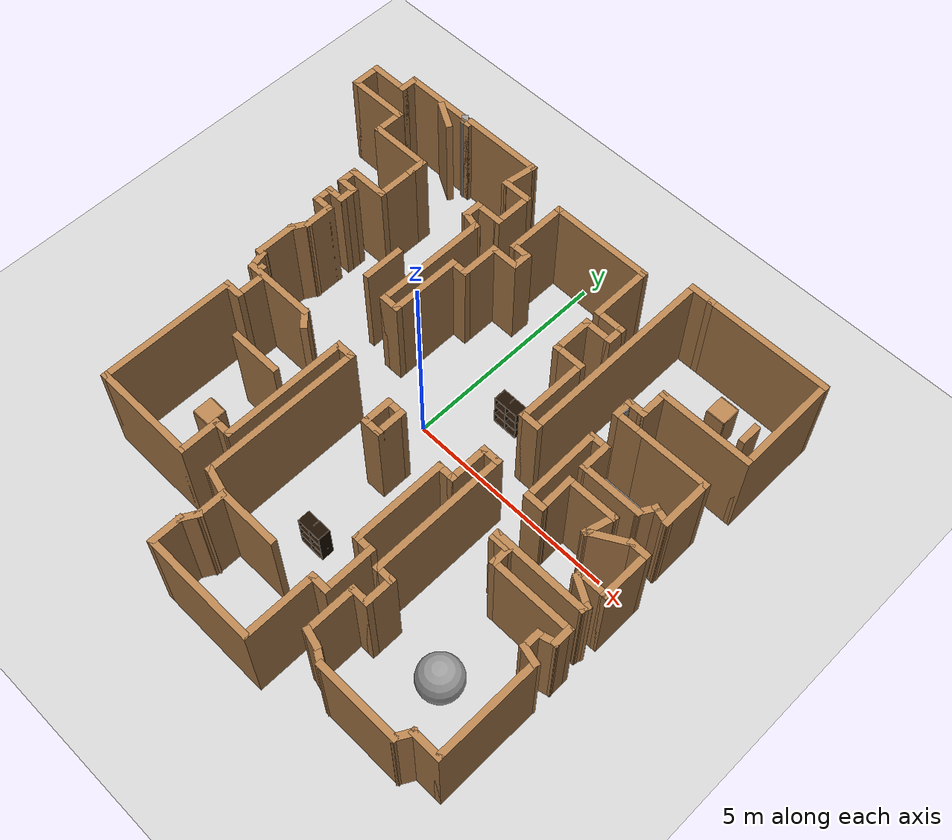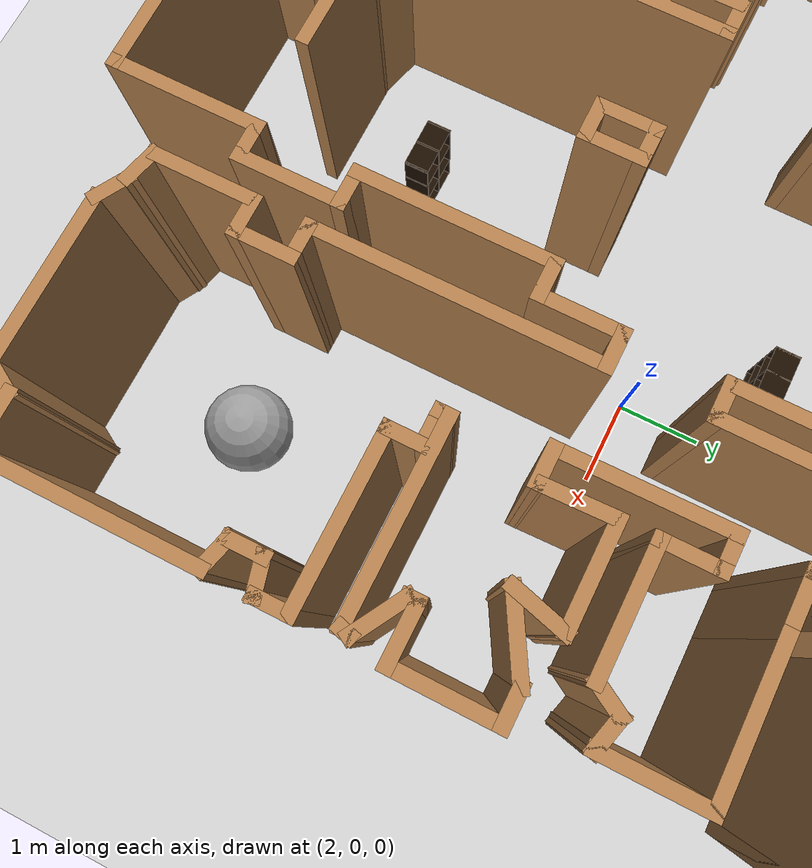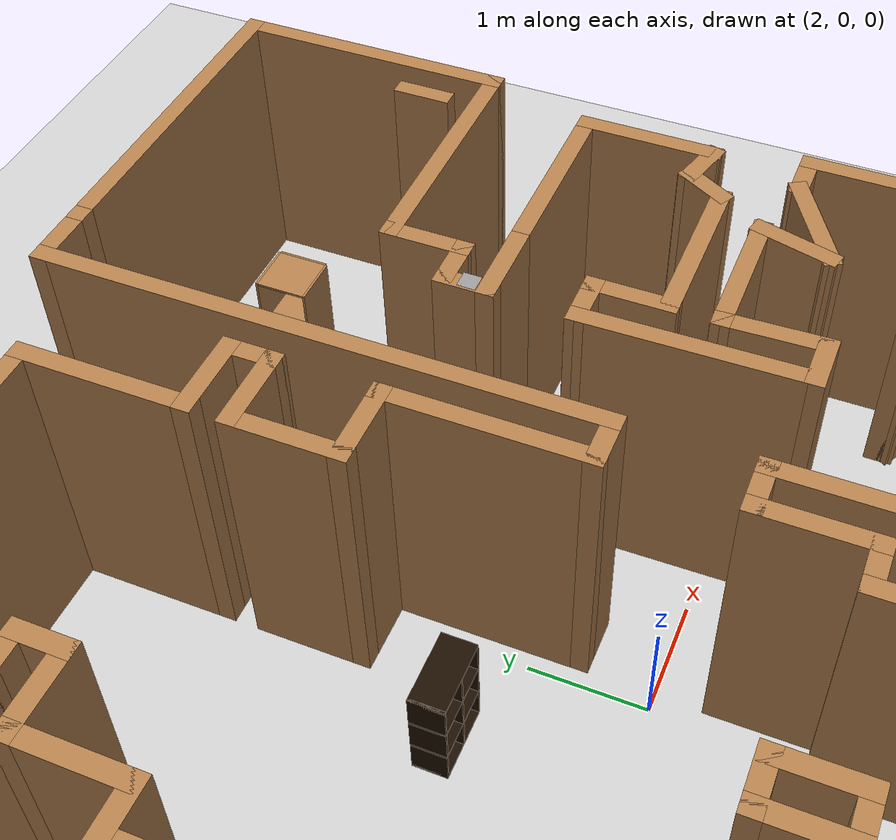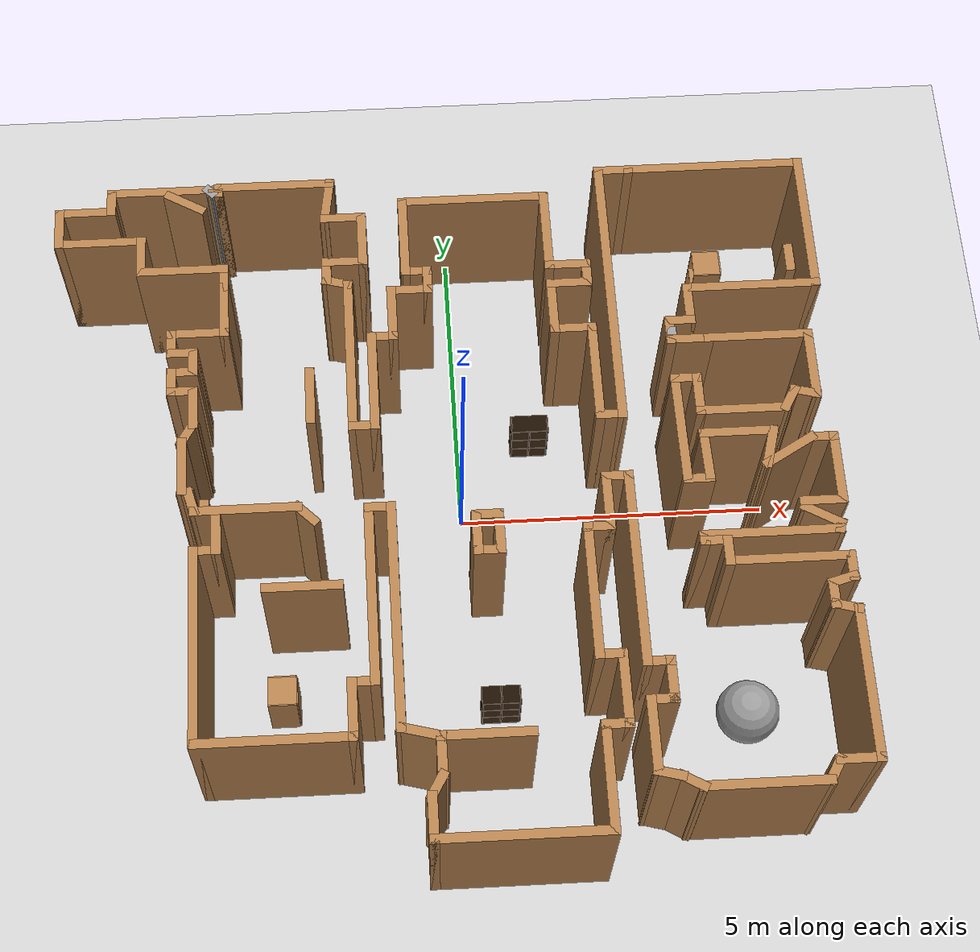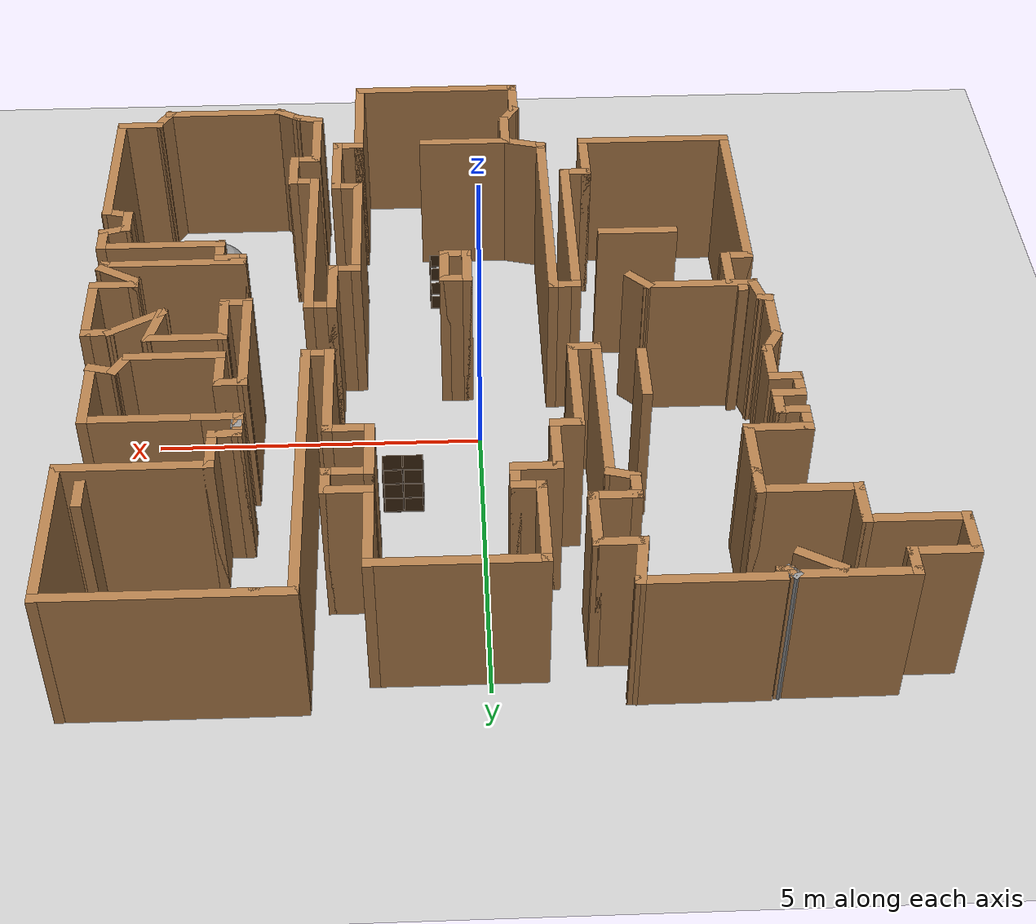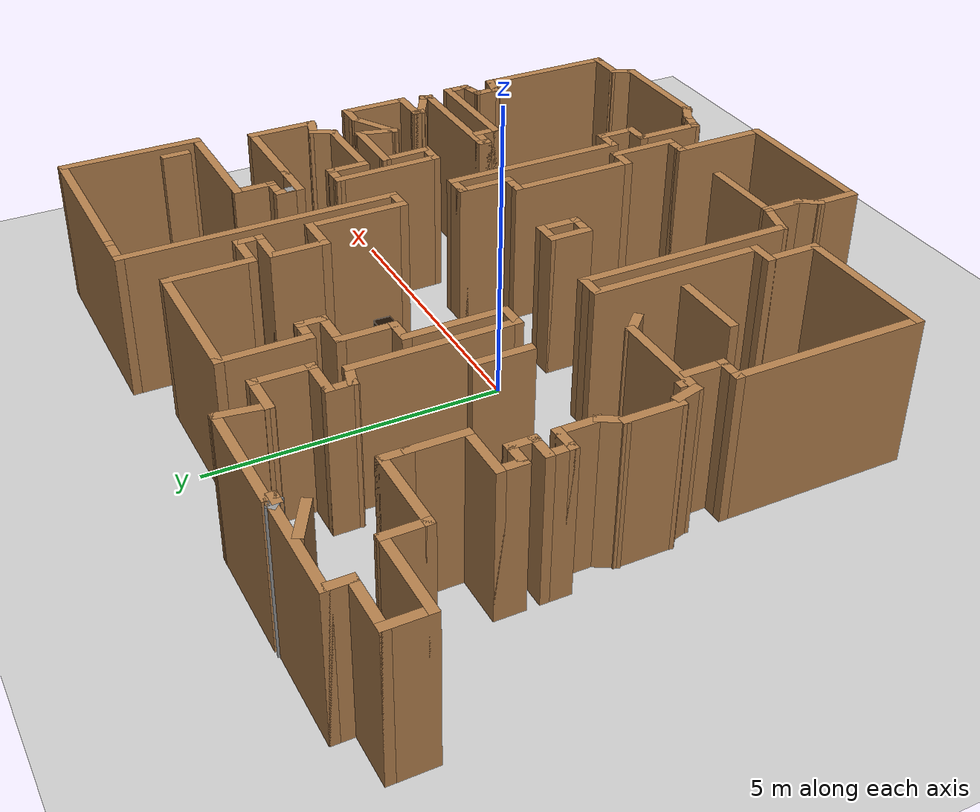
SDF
<sdf version="1.6">
 <world name="default">
  <light name="sun" type="directional">
   <pose>0 0 10 0 -0 0</pose>
   <diffuse>0.8 0.8 0.8 1</diffuse>
   <specular>0.2 0.2 0.2 1</specular>
   <attenuation>
    <range>1000</range>
    <constant>0.9</constant>
    <linear>0.01</linear>
    <quadratic>0.001</quadratic>
   </attenuation>
   <direction>-0.5 0.1 -0.9</direction>
  </light>
  <model name="ground_plane">
   <static>1</static>
   <link name="link">
    <collision name="collision">
     <geometry><plane><normal>0 0 1</normal><size>100 100</size></plane></geometry>
     <surface><friction><ode><mu>100</mu><mu2>50</mu2></ode></friction></surface>
    </collision>
    <visual name="visual">
     <cast_shadows>0</cast_shadows>
     <geometry><plane><normal>0 0 1</normal><size>100 100</size></plane></geometry>
     <material>
      <script><uri>file://media/materials/scripts/gazebo.material</uri><name>Gazebo/Grey</name></script>
     </material>
    </visual>
   </link>
  </model>
  <gravity>0 0 -9.8</gravity>
  <magnetic_field>6e-06 2.3e-05 -4.2e-05</magnetic_field>
  <atmosphere type="adiabatic"/>
  <physics name="default_physics" default="0" type="ode">
   <max_step_size>0.001</max_step_size>
   <real_time_factor>1</real_time_factor>
   <real_time_update_rate>1000</real_time_update_rate>
  </physics>
  <scene><ambient>0.4 0.4 0.4 1</ambient><background>0.7 0.7 0.7 1</background><shadows>1</shadows></scene>
  <spherical_coordinates>
   <surface_model>EARTH_WGS84</surface_model>
   <latitude_deg>0</latitude_deg>
   <longitude_deg>0</longitude_deg>
   <elevation>0</elevation>
   <heading_deg>0</heading_deg>
  </spherical_coordinates>
  <model name="map_30">
   <link name="Wall_10">
    <pose>-6.15506 4.97315 0 0 0 -1.5708</pose>
    <visual name="Wall_10_Visual">
     <pose>0 0 1.25 0 -0 0</pose>
     <geometry><box><size>0.75 0.15 2.5</size></box></geometry>
     <material>
      <script><uri>file://media/materials/scripts/gazebo.material</uri><name>Gazebo/Wood</name></script>
      <ambient>1 1 1 1</ambient>
      <shader type="pixel"/>
     </material>
     <meta><layer>0</layer></meta>
    </visual>
    <collision name="Wall_10_Collision">
     <pose>0 0 1.25 0 -0 0</pose>
     <geometry><box><size>0.75 0.15 2.5</size></box></geometry>
     <surface>
      <friction>
       <ode><mu>1</mu><mu2>1</mu2><fdir1>0 0 0</fdir1><slip1>0</slip1><slip2>0</slip2></ode>
       <torsional>
        <coefficient>1</coefficient>
        <patch_radius>0</patch_radius>
        <surface_radius>0</surface_radius>
        <use_patch_radius>1</use_patch_radius>
        <ode><slip>0</slip></ode>
       </torsional>
      </friction>
      <bounce><restitution_coefficient>0</restitution_coefficient><threshold>1e+06</threshold></bounce>
      <contact>
       <collide_without_contact>0</collide_without_contact>
       <collide_without_contact_bitmask>1</collide_without_contact_bitmask>
       <collide_bitmask>1</collide_bitmask>
       <ode>
        <soft_cfm>0</soft_cfm>
        <soft_erp>0.2</soft_erp>
        <kp>1e+13</kp>
        <kd>1</kd>
        <max_vel>0.01</max_vel>
        <min_depth>0</min_depth>
       </ode>
       <bullet>
        <split_impulse>1</split_impulse>
        <split_impulse_penetration_threshold>-0.01</split_impulse_penetration_threshold>
        <soft_cfm>0</soft_cfm>
        <soft_erp>0.2</soft_erp>
        <kp>1e+13</kp>
        <kd>1</kd>
       </bullet>
      </contact>
     </surface>
    </collision>
   </link>
   <link name="Wall_100">
    <pose>3.86655 -1.14749 0 0 -0 1.5708</pose>
    <visual name="Wall_100_Visual">
     <pose>0 0 1.25 0 -0 0</pose>
     <geometry><box><size>0.25 0.15 2.5</size></box></geometry>
     <material>
      <script><uri>file://media/materials/scripts/gazebo.material</uri><name>Gazebo/Wood</name></script>
      <ambient>1 1 1 1</ambient>
      <shader type="pixel"/>
     </material>
     <meta><layer>0</layer></meta>
    </visual>
    <collision name="Wall_100_Collision">
     <pose>0 0 1.25 0 -0 0</pose>
     <geometry><box><size>0.25 0.15 2.5</size></box></geometry>
     <surface>
      <friction>
       <ode><mu>1</mu><mu2>1</mu2><fdir1>0 0 0</fdir1><slip1>0</slip1><slip2>0</slip2></ode>
       <torsional>
        <coefficient>1</coefficient>
        <patch_radius>0</patch_radius>
        <surface_radius>0</surface_radius>
        <use_patch_radius>1</use_patch_radius>
        <ode><slip>0</slip></ode>
       </torsional>
      </friction>
      <bounce><restitution_coefficient>0</restitution_coefficient><threshold>1e+06</threshold></bounce>
      <contact>
       <collide_without_contact>0</collide_without_contact>
       <collide_without_contact_bitmask>1</collide_without_contact_bitmask>
       <collide_bitmask>1</collide_bitmask>
       <ode>
        <soft_cfm>0</soft_cfm>
        <soft_erp>0.2</soft_erp>
        <kp>1e+13</kp>
        <kd>1</kd>
        <max_vel>0.01</max_vel>
        <min_depth>0</min_depth>
       </ode>
       <bullet>
        <split_impulse>1</split_impulse>
        <split_impulse_penetration_threshold>-0.01</split_impulse_penetration_threshold>
        <soft_cfm>0</soft_cfm>
        <soft_erp>0.2</soft_erp>
        <kp>1e+13</kp>
        <kd>1</kd>
       </bullet>
      </contact>
     </surface>
    </collision>
   </link>
   <link name="Wall_101">
    <pose>4.91655 -1.09749 0 0 -0 0</pose>
    <visual name="Wall_101_Visual">
     <pose>0 0 1.25 0 -0 0</pose>
     <geometry><box><size>2.25 0.15 2.5</size></box></geometry>
     <material>
      <script><uri>file://media/materials/scripts/gazebo.material</uri><name>Gazebo/Wood</name></script>
      <ambient>1 1 1 1</ambient>
      <shader type="pixel"/>
     </material>
     <meta><layer>0</layer></meta>
    </visual>
    <collision name="Wall_101_Collision">
     <pose>0 0 1.25 0 -0 0</pose>
     <geometry><box><size>2.25 0.15 2.5</size></box></geometry>
     <surface>
      <friction>
       <ode><mu>1</mu><mu2>1</mu2><fdir1>0 0 0</fdir1><slip1>0</slip1><slip2>0</slip2></ode>
       <torsional>
        <coefficient>1</coefficient>
        <patch_radius>0</patch_radius>
        <surface_radius>0</surface_radius>
        <use_patch_radius>1</use_patch_radius>
        <ode><slip>0</slip></ode>
       </torsional>
      </friction>
      <bounce><restitution_coefficient>0</restitution_coefficient><threshold>1e+06</threshold></bounce>
      <contact>
       <collide_without_contact>0</collide_without_contact>
       <collide_without_contact_bitmask>1</collide_without_contact_bitmask>
       <collide_bitmask>1</collide_bitmask>
       <ode>
        <soft_cfm>0</soft_cfm>
        <soft_erp>0.2</soft_erp>
        <kp>1e+13</kp>
        <kd>1</kd>
        <max_vel>0.01</max_vel>
        <min_depth>0</min_depth>
       </ode>
       <bullet>
        <split_impulse>1</split_impulse>
        <split_impulse_penetration_threshold>-0.01</split_impulse_penetration_threshold>
        <soft_cfm>0</soft_cfm>
        <soft_erp>0.2</soft_erp>
        <kp>1e+13</kp>
        <kd>1</kd>
       </bullet>
      </contact>
     </surface>
    </collision>
   </link>
   <link name="Wall_102">
    <pose>5.97949 -1.04919 0 0 -0 1.309</pose>
    <visual name="Wall_102_Visual">
     <pose>0 0 1.25 0 -0 0</pose>
     <geometry><box><size>0.25 0.15 2.5</size></box></geometry>
     <material>
      <script><uri>file://media/materials/scripts/gazebo.material</uri><name>Gazebo/Wood</name></script>
      <ambient>1 1 1 1</ambient>
      <shader type="pixel"/>
     </material>
     <meta><layer>0</layer></meta>
    </visual>
    <collision name="Wall_102_Collision">
     <pose>0 0 1.25 0 -0 0</pose>
     <geometry><box><size>0.25 0.15 2.5</size></box></geometry>
     <surface>
      <friction>
       <ode><mu>1</mu><mu2>1</mu2><fdir1>0 0 0</fdir1><slip1>0</slip1><slip2>0</slip2></ode>
       <torsional>
        <coefficient>1</coefficient>
        <patch_radius>0</patch_radius>
        <surface_radius>0</surface_radius>
        <use_patch_radius>1</use_patch_radius>
        <ode><slip>0</slip></ode>
       </torsional>
      </friction>
      <bounce><restitution_coefficient>0</restitution_coefficient><threshold>1e+06</threshold></bounce>
      <contact>
       <collide_without_contact>0</collide_without_contact>
       <collide_without_contact_bitmask>1</collide_without_contact_bitmask>
       <collide_bitmask>1</collide_bitmask>
       <ode>
        <soft_cfm>0</soft_cfm>
        <soft_erp>0.2</soft_erp>
        <kp>1e+13</kp>
        <kd>1</kd>
        <max_vel>0.01</max_vel>
        <min_depth>0</min_depth>
       </ode>
       <bullet>
        <split_impulse>1</split_impulse>
        <split_impulse_penetration_threshold>-0.01</split_impulse_penetration_threshold>
        <soft_cfm>0</soft_cfm>
        <soft_erp>0.2</soft_erp>
        <kp>1e+13</kp>
        <kd>1</kd>
       </bullet>
      </contact>
     </surface>
    </collision>
   </link>
   <link name="Wall_103">
    <pose>5.73262 -0.850895 0 0 -0 2.61799</pose>
    <visual name="Wall_103_Visual">
     <pose>0 0 1.25 0 -0 0</pose>
     <geometry><box><size>0.75 0.15 2.5</size></box></geometry>
     <material>
      <script><uri>file://media/materials/scripts/gazebo.material</uri><name>Gazebo/Wood</name></script>
      <ambient>1 1 1 1</ambient>
      <shader type="pixel"/>
     </material>
     <meta><layer>0</layer></meta>
    </visual>
    <collision name="Wall_103_Collision">
     <pose>0 0 1.25 0 -0 0</pose>
     <geometry><box><size>0.75 0.15 2.5</size></box></geometry>
     <surface>
      <friction>
       <ode><mu>1</mu><mu2>1</mu2><fdir1>0 0 0</fdir1><slip1>0</slip1><slip2>0</slip2></ode>
       <torsional>
        <coefficient>1</coefficient>
        <patch_radius>0</patch_radius>
        <surface_radius>0</surface_radius>
        <use_patch_radius>1</use_patch_radius>
        <ode><slip>0</slip></ode>
       </torsional>
      </friction>
      <bounce><restitution_coefficient>0</restitution_coefficient><threshold>1e+06</threshold></bounce>
      <contact>
       <collide_without_contact>0</collide_without_contact>
       <collide_without_contact_bitmask>1</collide_without_contact_bitmask>
       <collide_bitmask>1</collide_bitmask>
       <ode>
        <soft_cfm>0</soft_cfm>
        <soft_erp>0.2</soft_erp>
        <kp>1e+13</kp>
        <kd>1</kd>
        <max_vel>0.01</max_vel>
        <min_depth>0</min_depth>
       </ode>
       <bullet>
        <split_impulse>1</split_impulse>
        <split_impulse_penetration_threshold>-0.01</split_impulse_penetration_threshold>
        <soft_cfm>0</soft_cfm>
        <soft_erp>0.2</soft_erp>
        <kp>1e+13</kp>
        <kd>1</kd>
       </bullet>
      </contact>
     </surface>
    </collision>
   </link>
   <link name="Wall_104">
    <pose>5.47282 -0.650895 0 0 -0 1.5708</pose>
    <visual name="Wall_104_Visual">
     <pose>0 0 1.25 0 -0 0</pose>
     <geometry><box><size>0.25 0.15 2.5</size></box></geometry>
     <material>
      <script><uri>file://media/materials/scripts/gazebo.material</uri><name>Gazebo/Wood</name></script>
      <ambient>1 1 1 1</ambient>
      <shader type="pixel"/>
     </material>
     <meta><layer>0</layer></meta>
    </visual>
    <collision name="Wall_104_Collision">
     <pose>0 0 1.25 0 -0 0</pose>
     <geometry><box><size>0.25 0.15 2.5</size></box></geometry>
     <surface>
      <friction>
       <ode><mu>1</mu><mu2>1</mu2><fdir1>0 0 0</fdir1><slip1>0</slip1><slip2>0</slip2></ode>
       <torsional>
        <coefficient>1</coefficient>
        <patch_radius>0</patch_radius>
        <surface_radius>0</surface_radius>
        <use_patch_radius>1</use_patch_radius>
        <ode><slip>0</slip></ode>
       </torsional>
      </friction>
      <bounce><restitution_coefficient>0</restitution_coefficient><threshold>1e+06</threshold></bounce>
      <contact>
       <collide_without_contact>0</collide_without_contact>
       <collide_without_contact_bitmask>1</collide_without_contact_bitmask>
       <collide_bitmask>1</collide_bitmask>
       <ode>
        <soft_cfm>0</soft_cfm>
        <soft_erp>0.2</soft_erp>
        <kp>1e+13</kp>
        <kd>1</kd>
        <max_vel>0.01</max_vel>
        <min_depth>0</min_depth>
       </ode>
       <bullet>
        <split_impulse>1</split_impulse>
        <split_impulse_penetration_threshold>-0.01</split_impulse_penetration_threshold>
        <soft_cfm>0</soft_cfm>
        <soft_erp>0.2</soft_erp>
        <kp>1e+13</kp>
        <kd>1</kd>
       </bullet>
      </contact>
     </surface>
    </collision>
   </link>
   <link name="Wall_105">
    <pose>5.77282 -0.600895 0 0 -0 0</pose>
    <visual name="Wall_105_Visual">
     <pose>0 0 1.25 0 -0 0</pose>
     <geometry><box><size>0.75 0.15 2.5</size></box></geometry>
     <material>
      <script><uri>file://media/materials/scripts/gazebo.material</uri><name>Gazebo/Wood</name></script>
      <ambient>1 1 1 1</ambient>
      <shader type="pixel"/>
     </material>
     <meta><layer>0</layer></meta>
    </visual>
    <collision name="Wall_105_Collision">
     <pose>0 0 1.25 0 -0 0</pose>
     <geometry><box><size>0.75 0.15 2.5</size></box></geometry>
     <surface>
      <friction>
       <ode><mu>1</mu><mu2>1</mu2><fdir1>0 0 0</fdir1><slip1>0</slip1><slip2>0</slip2></ode>
       <torsional>
        <coefficient>1</coefficient>
        <patch_radius>0</patch_radius>
        <surface_radius>0</surface_radius>
        <use_patch_radius>1</use_patch_radius>
        <ode><slip>0</slip></ode>
       </torsional>
      </friction>
      <bounce><restitution_coefficient>0</restitution_coefficient><threshold>1e+06</threshold></bounce>
      <contact>
       <collide_without_contact>0</collide_without_contact>
       <collide_without_contact_bitmask>1</collide_without_contact_bitmask>
       <collide_bitmask>1</collide_bitmask>
       <ode>
        <soft_cfm>0</soft_cfm>
        <soft_erp>0.2</soft_erp>
        <kp>1e+13</kp>
        <kd>1</kd>
        <max_vel>0.01</max_vel>
        <min_depth>0</min_depth>
       </ode>
       <bullet>
        <split_impulse>1</split_impulse>
        <split_impulse_penetration_threshold>-0.01</split_impulse_penetration_threshold>
        <soft_cfm>0</soft_cfm>
        <soft_erp>0.2</soft_erp>
        <kp>1e+13</kp>
        <kd>1</kd>
       </bullet>
      </contact>
     </surface>
    </collision>
   </link>
   <link name="Wall_106">
    <pose>6.07282 -0.050895 0 0 -0 1.5708</pose>
    <visual name="Wall_106_Visual">
     <pose>0 0 1.25 0 -0 0</pose>
     <geometry><box><size>1.25 0.15 2.5</size></box></geometry>
     <material>
      <script><uri>file://media/materials/scripts/gazebo.material</uri><name>Gazebo/Wood</name></script>
      <ambient>1 1 1 1</ambient>
      <shader type="pixel"/>
     </material>
     <meta><layer>0</layer></meta>
    </visual>
    <collision name="Wall_106_Collision">
     <pose>0 0 1.25 0 -0 0</pose>
     <geometry><box><size>1.25 0.15 2.5</size></box></geometry>
     <surface>
      <friction>
       <ode><mu>1</mu><mu2>1</mu2><fdir1>0 0 0</fdir1><slip1>0</slip1><slip2>0</slip2></ode>
       <torsional>
        <coefficient>1</coefficient>
        <patch_radius>0</patch_radius>
        <surface_radius>0</surface_radius>
        <use_patch_radius>1</use_patch_radius>
        <ode><slip>0</slip></ode>
       </torsional>
      </friction>
      <bounce><restitution_coefficient>0</restitution_coefficient><threshold>1e+06</threshold></bounce>
      <contact>
       <collide_without_contact>0</collide_without_contact>
       <collide_without_contact_bitmask>1</collide_without_contact_bitmask>
       <collide_bitmask>1</collide_bitmask>
       <ode>
        <soft_cfm>0</soft_cfm>
        <soft_erp>0.2</soft_erp>
        <kp>1e+13</kp>
        <kd>1</kd>
        <max_vel>0.01</max_vel>
        <min_depth>0</min_depth>
       </ode>
       <bullet>
        <split_impulse>1</split_impulse>
        <split_impulse_penetration_threshold>-0.01</split_impulse_penetration_threshold>
        <soft_cfm>0</soft_cfm>
        <soft_erp>0.2</soft_erp>
        <kp>1e+13</kp>
        <kd>1</kd>
       </bullet>
      </contact>
     </surface>
    </collision>
   </link>
   <link name="Wall_107">
    <pose>5.89782 0.499105 0 0 -0 3.14159</pose>
    <visual name="Wall_107_Visual">
     <pose>0 0 1.25 0 -0 0</pose>
     <geometry><box><size>0.5 0.15 2.5</size></box></geometry>
     <material>
      <script><uri>file://media/materials/scripts/gazebo.material</uri><name>Gazebo/Wood</name></script>
      <ambient>1 1 1 1</ambient>
      <shader type="pixel"/>
     </material>
     <meta><layer>0</layer></meta>
    </visual>
    <collision name="Wall_107_Collision">
     <pose>0 0 1.25 0 -0 0</pose>
     <geometry><box><size>0.5 0.15 2.5</size></box></geometry>
     <surface>
      <friction>
       <ode><mu>1</mu><mu2>1</mu2><fdir1>0 0 0</fdir1><slip1>0</slip1><slip2>0</slip2></ode>
       <torsional>
        <coefficient>1</coefficient>
        <patch_radius>0</patch_radius>
        <surface_radius>0</surface_radius>
        <use_patch_radius>1</use_patch_radius>
        <ode><slip>0</slip></ode>
       </torsional>
      </friction>
      <bounce><restitution_coefficient>0</restitution_coefficient><threshold>1e+06</threshold></bounce>
      <contact>
       <collide_without_contact>0</collide_without_contact>
       <collide_without_contact_bitmask>1</collide_without_contact_bitmask>
       <collide_bitmask>1</collide_bitmask>
       <ode>
        <soft_cfm>0</soft_cfm>
        <soft_erp>0.2</soft_erp>
        <kp>1e+13</kp>
        <kd>1</kd>
        <max_vel>0.01</max_vel>
        <min_depth>0</min_depth>
       </ode>
       <bullet>
        <split_impulse>1</split_impulse>
        <split_impulse_penetration_threshold>-0.01</split_impulse_penetration_threshold>
        <soft_cfm>0</soft_cfm>
        <soft_erp>0.2</soft_erp>
        <kp>1e+13</kp>
        <kd>1</kd>
       </bullet>
      </contact>
     </surface>
    </collision>
   </link>
   <link name="Wall_108">
    <pose>5.35475 0.286605 0 0 0 -2.61799</pose>
    <visual name="Wall_108_Visual">
     <pose>0 0 1.25 0 -0 0</pose>
     <geometry><box><size>1 0.15 2.5</size></box></geometry>
     <material>
      <script><uri>file://media/materials/scripts/gazebo.material</uri><name>Gazebo/Wood</name></script>
      <ambient>1 1 1 1</ambient>
      <shader type="pixel"/>
     </material>
     <meta><layer>0</layer></meta>
    </visual>
    <collision name="Wall_108_Collision">
     <pose>0 0 1.25 0 -0 0</pose>
     <geometry><box><size>1 0.15 2.5</size></box></geometry>
     <surface>
      <friction>
       <ode><mu>1</mu><mu2>1</mu2><fdir1>0 0 0</fdir1><slip1>0</slip1><slip2>0</slip2></ode>
       <torsional>
        <coefficient>1</coefficient>
        <patch_radius>0</patch_radius>
        <surface_radius>0</surface_radius>
        <use_patch_radius>1</use_patch_radius>
        <ode><slip>0</slip></ode>
       </torsional>
      </friction>
      <bounce><restitution_coefficient>0</restitution_coefficient><threshold>1e+06</threshold></bounce>
      <contact>
       <collide_without_contact>0</collide_without_contact>
       <collide_without_contact_bitmask>1</collide_without_contact_bitmask>
       <collide_bitmask>1</collide_bitmask>
       <ode>
        <soft_cfm>0</soft_cfm>
        <soft_erp>0.2</soft_erp>
        <kp>1e+13</kp>
        <kd>1</kd>
        <max_vel>0.01</max_vel>
        <min_depth>0</min_depth>
       </ode>
       <bullet>
        <split_impulse>1</split_impulse>
        <split_impulse_penetration_threshold>-0.01</split_impulse_penetration_threshold>
        <soft_cfm>0</soft_cfm>
        <soft_erp>0.2</soft_erp>
        <kp>1e+13</kp>
        <kd>1</kd>
       </bullet>
      </contact>
     </surface>
    </collision>
   </link>
   <link name="Wall_109">
    <pose>5.06434 0.363883 0 0 -0 1.309</pose>
    <visual name="Wall_109_Visual">
     <pose>0 0 1.25 0 -0 0</pose>
     <geometry><box><size>0.75 0.15 2.5</size></box></geometry>
     <material>
      <script><uri>file://media/materials/scripts/gazebo.material</uri><name>Gazebo/Wood</name></script>
      <ambient>1 1 1 1</ambient>
      <shader type="pixel"/>
     </material>
     <meta><layer>0</layer></meta>
    </visual>
    <collision name="Wall_109_Collision">
     <pose>0 0 1.25 0 -0 0</pose>
     <geometry><box><size>0.75 0.15 2.5</size></box></geometry>
     <surface>
      <friction>
       <ode><mu>1</mu><mu2>1</mu2><fdir1>0 0 0</fdir1><slip1>0</slip1><slip2>0</slip2></ode>
       <torsional>
        <coefficient>1</coefficient>
        <patch_radius>0</patch_radius>
        <surface_radius>0</surface_radius>
        <use_patch_radius>1</use_patch_radius>
        <ode><slip>0</slip></ode>
       </torsional>
      </friction>
      <bounce><restitution_coefficient>0</restitution_coefficient><threshold>1e+06</threshold></bounce>
      <contact>
       <collide_without_contact>0</collide_without_contact>
       <collide_without_contact_bitmask>1</collide_without_contact_bitmask>
       <collide_bitmask>1</collide_bitmask>
       <ode>
        <soft_cfm>0</soft_cfm>
        <soft_erp>0.2</soft_erp>
        <kp>1e+13</kp>
        <kd>1</kd>
        <max_vel>0.01</max_vel>
        <min_depth>0</min_depth>
       </ode>
       <bullet>
        <split_impulse>1</split_impulse>
        <split_impulse_penetration_threshold>-0.01</split_impulse_penetration_threshold>
        <soft_cfm>0</soft_cfm>
        <soft_erp>0.2</soft_erp>
        <kp>1e+13</kp>
        <kd>1</kd>
       </bullet>
      </contact>
     </surface>
    </collision>
   </link>
   <link name="Wall_112">
    <pose>4.59199 0.653661 0 0 -0 3.14159</pose>
    <visual name="Wall_112_Visual">
     <pose>0 0 1.25 0 -0 0</pose>
     <geometry><box><size>1.25 0.15 2.5</size></box></geometry>
     <material>
      <script><uri>file://media/materials/scripts/gazebo.material</uri><name>Gazebo/Wood</name></script>
      <ambient>1 1 1 1</ambient>
      <shader type="pixel"/>
     </material>
     <meta><layer>0</layer></meta>
    </visual>
    <collision name="Wall_112_Collision">
     <pose>0 0 1.25 0 -0 0</pose>
     <geometry><box><size>1.25 0.15 2.5</size></box></geometry>
     <surface>
      <friction>
       <ode><mu>1</mu><mu2>1</mu2><fdir1>0 0 0</fdir1><slip1>0</slip1><slip2>0</slip2></ode>
       <torsional>
        <coefficient>1</coefficient>
        <patch_radius>0</patch_radius>
        <surface_radius>0</surface_radius>
        <use_patch_radius>1</use_patch_radius>
        <ode><slip>0</slip></ode>
       </torsional>
      </friction>
      <bounce><restitution_coefficient>0</restitution_coefficient><threshold>1e+06</threshold></bounce>
      <contact>
       <collide_without_contact>0</collide_without_contact>
       <collide_without_contact_bitmask>1</collide_without_contact_bitmask>
       <collide_bitmask>1</collide_bitmask>
       <ode>
        <soft_cfm>0</soft_cfm>
        <soft_erp>0.2</soft_erp>
        <kp>1e+13</kp>
        <kd>1</kd>
        <max_vel>0.01</max_vel>
        <min_depth>0</min_depth>
       </ode>
       <bullet>
        <split_impulse>1</split_impulse>
        <split_impulse_penetration_threshold>-0.01</split_impulse_penetration_threshold>
        <soft_cfm>0</soft_cfm>
        <soft_erp>0.2</soft_erp>
        <kp>1e+13</kp>
        <kd>1</kd>
       </bullet>
      </contact>
     </surface>
    </collision>
   </link>
   <link name="Wall_113">
    <pose>4.05355 0.286487 0 0 0 -1.53931</pose>
    <visual name="Wall_113_Visual">
     <pose>0 0 1.25 0 -0 0</pose>
     <geometry><box><size>0.884711 0.15 2.5</size></box></geometry>
     <material>
      <script><uri>file://media/materials/scripts/gazebo.material</uri><name>Gazebo/Wood</name></script>
      <ambient>1 1 1 1</ambient>
      <shader type="pixel"/>
     </material>
     <meta><layer>0</layer></meta>
    </visual>
    <collision name="Wall_113_Collision">
     <pose>0 0 1.25 0 -0 0</pose>
     <geometry><box><size>0.884711 0.15 2.5</size></box></geometry>
     <surface>
      <friction>
       <ode><mu>1</mu><mu2>1</mu2><fdir1>0 0 0</fdir1><slip1>0</slip1><slip2>0</slip2></ode>
       <torsional>
        <coefficient>1</coefficient>
        <patch_radius>0</patch_radius>
        <surface_radius>0</surface_radius>
        <use_patch_radius>1</use_patch_radius>
        <ode><slip>0</slip></ode>
       </torsional>
      </friction>
      <bounce><restitution_coefficient>0</restitution_coefficient><threshold>1e+06</threshold></bounce>
      <contact>
       <collide_without_contact>0</collide_without_contact>
       <collide_without_contact_bitmask>1</collide_without_contact_bitmask>
       <collide_bitmask>1</collide_bitmask>
       <ode>
        <soft_cfm>0</soft_cfm>
        <soft_erp>0.2</soft_erp>
        <kp>1e+13</kp>
        <kd>1</kd>
        <max_vel>0.01</max_vel>
        <min_depth>0</min_depth>
       </ode>
       <bullet>
        <split_impulse>1</split_impulse>
        <split_impulse_penetration_threshold>-0.01</split_impulse_penetration_threshold>
        <soft_cfm>0</soft_cfm>
        <soft_erp>0.2</soft_erp>
        <kp>1e+13</kp>
        <kd>1</kd>
       </bullet>
      </contact>
     </surface>
    </collision>
   </link>
   <link name="Wall_116">
    <pose>3.89012 -0.126947 0 0 -0 3.14159</pose>
    <visual name="Wall_116_Visual">
     <pose>0 0 1.25 0 -0 0</pose>
     <geometry><box><size>0.5 0.15 2.5</size></box></geometry>
     <material>
      <script><uri>file://media/materials/scripts/gazebo.material</uri><name>Gazebo/Wood</name></script>
      <ambient>1 1 1 1</ambient>
      <shader type="pixel"/>
     </material>
     <meta><layer>0</layer></meta>
    </visual>
    <collision name="Wall_116_Collision">
     <pose>0 0 1.25 0 -0 0</pose>
     <geometry><box><size>0.5 0.15 2.5</size></box></geometry>
     <surface>
      <friction>
       <ode><mu>1</mu><mu2>1</mu2><fdir1>0 0 0</fdir1><slip1>0</slip1><slip2>0</slip2></ode>
       <torsional>
        <coefficient>1</coefficient>
        <patch_radius>0</patch_radius>
        <surface_radius>0</surface_radius>
        <use_patch_radius>1</use_patch_radius>
        <ode><slip>0</slip></ode>
       </torsional>
      </friction>
      <bounce><restitution_coefficient>0</restitution_coefficient><threshold>1e+06</threshold></bounce>
      <contact>
       <collide_without_contact>0</collide_without_contact>
       <collide_without_contact_bitmask>1</collide_without_contact_bitmask>
       <collide_bitmask>1</collide_bitmask>
       <ode>
        <soft_cfm>0</soft_cfm>
        <soft_erp>0.2</soft_erp>
        <kp>1e+13</kp>
        <kd>1</kd>
        <max_vel>0.01</max_vel>
        <min_depth>0</min_depth>
       </ode>
       <bullet>
        <split_impulse>1</split_impulse>
        <split_impulse_penetration_threshold>-0.01</split_impulse_penetration_threshold>
        <soft_cfm>0</soft_cfm>
        <soft_erp>0.2</soft_erp>
        <kp>1e+13</kp>
        <kd>1</kd>
       </bullet>
      </contact>
     </surface>
    </collision>
   </link>
   <link name="Wall_117">
    <pose>3.70355 0.786487 0 0 -0 1.58413</pose>
    <visual name="Wall_117_Visual">
     <pose>0 0 1.25 0 -0 0</pose>
     <geometry><box><size>1.8845 0.15 2.5</size></box></geometry>
     <material>
      <script><uri>file://media/materials/scripts/gazebo.material</uri><name>Gazebo/Wood</name></script>
      <ambient>1 1 1 1</ambient>
      <shader type="pixel"/>
     </material>
     <meta><layer>0</layer></meta>
    </visual>
    <collision name="Wall_117_Collision">
     <pose>0 0 1.25 0 -0 0</pose>
     <geometry><box><size>1.8845 0.15 2.5</size></box></geometry>
     <surface>
      <friction>
       <ode><mu>1</mu><mu2>1</mu2><fdir1>0 0 0</fdir1><slip1>0</slip1><slip2>0</slip2></ode>
       <torsional>
        <coefficient>1</coefficient>
        <patch_radius>0</patch_radius>
        <surface_radius>0</surface_radius>
        <use_patch_radius>1</use_patch_radius>
        <ode><slip>0</slip></ode>
       </torsional>
      </friction>
      <bounce><restitution_coefficient>0</restitution_coefficient><threshold>1e+06</threshold></bounce>
      <contact>
       <collide_without_contact>0</collide_without_contact>
       <collide_without_contact_bitmask>1</collide_without_contact_bitmask>
       <collide_bitmask>1</collide_bitmask>
       <ode>
        <soft_cfm>0</soft_cfm>
        <soft_erp>0.2</soft_erp>
        <kp>1e+13</kp>
        <kd>1</kd>
        <max_vel>0.01</max_vel>
        <min_depth>0</min_depth>
       </ode>
       <bullet>
        <split_impulse>1</split_impulse>
        <split_impulse_penetration_threshold>-0.01</split_impulse_penetration_threshold>
        <soft_cfm>0</soft_cfm>
        <soft_erp>0.2</soft_erp>
        <kp>1e+13</kp>
        <kd>1</kd>
       </bullet>
      </contact>
     </surface>
    </collision>
   </link>
   <link name="Wall_118">
    <pose>3.86699 1.65366 0 0 -0 0</pose>
    <visual name="Wall_118_Visual">
     <pose>0 0 1.25 0 -0 0</pose>
     <geometry><box><size>0.5 0.15 2.5</size></box></geometry>
     <material>
      <script><uri>file://media/materials/scripts/gazebo.material</uri><name>Gazebo/Wood</name></script>
      <ambient>1 1 1 1</ambient>
      <shader type="pixel"/>
     </material>
     <meta><layer>0</layer></meta>
    </visual>
    <collision name="Wall_118_Collision">
     <pose>0 0 1.25 0 -0 0</pose>
     <geometry><box><size>0.5 0.15 2.5</size></box></geometry>
     <surface>
      <friction>
       <ode><mu>1</mu><mu2>1</mu2><fdir1>0 0 0</fdir1><slip1>0</slip1><slip2>0</slip2></ode>
       <torsional>
        <coefficient>1</coefficient>
        <patch_radius>0</patch_radius>
        <surface_radius>0</surface_radius>
        <use_patch_radius>1</use_patch_radius>
        <ode><slip>0</slip></ode>
       </torsional>
      </friction>
      <bounce><restitution_coefficient>0</restitution_coefficient><threshold>1e+06</threshold></bounce>
      <contact>
       <collide_without_contact>0</collide_without_contact>
       <collide_without_contact_bitmask>1</collide_without_contact_bitmask>
       <collide_bitmask>1</collide_bitmask>
       <ode>
        <soft_cfm>0</soft_cfm>
        <soft_erp>0.2</soft_erp>
        <kp>1e+13</kp>
        <kd>1</kd>
        <max_vel>0.01</max_vel>
        <min_depth>0</min_depth>
       </ode>
       <bullet>
        <split_impulse>1</split_impulse>
        <split_impulse_penetration_threshold>-0.01</split_impulse_penetration_threshold>
        <soft_cfm>0</soft_cfm>
        <soft_erp>0.2</soft_erp>
        <kp>1e+13</kp>
        <kd>1</kd>
       </bullet>
      </contact>
     </surface>
    </collision>
   </link>
   <link name="Wall_121">
    <pose>4.04199 1.35366 0 0 0 -1.5708</pose>
    <visual name="Wall_121_Visual">
     <pose>0 0 1.25 0 -0 0</pose>
     <geometry><box><size>0.75 0.15 2.5</size></box></geometry>
     <material>
      <script><uri>file://media/materials/scripts/gazebo.material</uri><name>Gazebo/Wood</name></script>
      <ambient>1 1 1 1</ambient>
      <shader type="pixel"/>
     </material>
     <meta><layer>0</layer></meta>
    </visual>
    <collision name="Wall_121_Collision">
     <pose>0 0 1.25 0 -0 0</pose>
     <geometry><box><size>0.75 0.15 2.5</size></box></geometry>
     <surface>
      <friction>
       <ode><mu>1</mu><mu2>1</mu2><fdir1>0 0 0</fdir1><slip1>0</slip1><slip2>0</slip2></ode>
       <torsional>
        <coefficient>1</coefficient>
        <patch_radius>0</patch_radius>
        <surface_radius>0</surface_radius>
        <use_patch_radius>1</use_patch_radius>
        <ode><slip>0</slip></ode>
       </torsional>
      </friction>
      <bounce><restitution_coefficient>0</restitution_coefficient><threshold>1e+06</threshold></bounce>
      <contact>
       <collide_without_contact>0</collide_without_contact>
       <collide_without_contact_bitmask>1</collide_without_contact_bitmask>
       <collide_bitmask>1</collide_bitmask>
       <ode>
        <soft_cfm>0</soft_cfm>
        <soft_erp>0.2</soft_erp>
        <kp>1e+13</kp>
        <kd>1</kd>
        <max_vel>0.01</max_vel>
        <min_depth>0</min_depth>
       </ode>
       <bullet>
        <split_impulse>1</split_impulse>
        <split_impulse_penetration_threshold>-0.01</split_impulse_penetration_threshold>
        <soft_cfm>0</soft_cfm>
        <soft_erp>0.2</soft_erp>
        <kp>1e+13</kp>
        <kd>1</kd>
       </bullet>
      </contact>
     </surface>
    </collision>
   </link>
   <link name="Wall_122">
    <pose>4.71699 1.05366 0 0 -0 0</pose>
    <visual name="Wall_122_Visual">
     <pose>0 0 1.25 0 -0 0</pose>
     <geometry><box><size>1.5 0.15 2.5</size></box></geometry>
     <material>
      <script><uri>file://media/materials/scripts/gazebo.material</uri><name>Gazebo/Wood</name></script>
      <ambient>1 1 1 1</ambient>
      <shader type="pixel"/>
     </material>
     <meta><layer>0</layer></meta>
    </visual>
    <collision name="Wall_122_Collision">
     <pose>0 0 1.25 0 -0 0</pose>
     <geometry><box><size>1.5 0.15 2.5</size></box></geometry>
     <surface>
      <friction>
       <ode><mu>1</mu><mu2>1</mu2><fdir1>0 0 0</fdir1><slip1>0</slip1><slip2>0</slip2></ode>
       <torsional>
        <coefficient>1</coefficient>
        <patch_radius>0</patch_radius>
        <surface_radius>0</surface_radius>
        <use_patch_radius>1</use_patch_radius>
        <ode><slip>0</slip></ode>
       </torsional>
      </friction>
      <bounce><restitution_coefficient>0</restitution_coefficient><threshold>1e+06</threshold></bounce>
      <contact>
       <collide_without_contact>0</collide_without_contact>
       <collide_without_contact_bitmask>1</collide_without_contact_bitmask>
       <collide_bitmask>1</collide_bitmask>
       <ode>
        <soft_cfm>0</soft_cfm>
        <soft_erp>0.2</soft_erp>
        <kp>1e+13</kp>
        <kd>1</kd>
        <max_vel>0.01</max_vel>
        <min_depth>0</min_depth>
       </ode>
       <bullet>
        <split_impulse>1</split_impulse>
        <split_impulse_penetration_threshold>-0.01</split_impulse_penetration_threshold>
        <soft_cfm>0</soft_cfm>
        <soft_erp>0.2</soft_erp>
        <kp>1e+13</kp>
        <kd>1</kd>
       </bullet>
      </contact>
     </surface>
    </collision>
   </link>
   <link name="Wall_123">
    <pose>5.47949 1.20521 0 0 -0 1.0472</pose>
    <visual name="Wall_123_Visual">
     <pose>0 0 1.25 0 -0 0</pose>
     <geometry><box><size>0.5 0.15 2.5</size></box></geometry>
     <material>
      <script><uri>file://media/materials/scripts/gazebo.material</uri><name>Gazebo/Wood</name></script>
      <ambient>1 1 1 1</ambient>
      <shader type="pixel"/>
     </material>
     <meta><layer>0</layer></meta>
    </visual>
    <collision name="Wall_123_Collision">
     <pose>0 0 1.25 0 -0 0</pose>
     <geometry><box><size>0.5 0.15 2.5</size></box></geometry>
     <surface>
      <friction>
       <ode><mu>1</mu><mu2>1</mu2><fdir1>0 0 0</fdir1><slip1>0</slip1><slip2>0</slip2></ode>
       <torsional>
        <coefficient>1</coefficient>
        <patch_radius>0</patch_radius>
        <surface_radius>0</surface_radius>
        <use_patch_radius>1</use_patch_radius>
        <ode><slip>0</slip></ode>
       </torsional>
      </friction>
      <bounce><restitution_coefficient>0</restitution_coefficient><threshold>1e+06</threshold></bounce>
      <contact>
       <collide_without_contact>0</collide_without_contact>
       <collide_without_contact_bitmask>1</collide_without_contact_bitmask>
       <collide_bitmask>1</collide_bitmask>
       <ode>
        <soft_cfm>0</soft_cfm>
        <soft_erp>0.2</soft_erp>
        <kp>1e+13</kp>
        <kd>1</kd>
        <max_vel>0.01</max_vel>
        <min_depth>0</min_depth>
       </ode>
       <bullet>
        <split_impulse>1</split_impulse>
        <split_impulse_penetration_threshold>-0.01</split_impulse_penetration_threshold>
        <soft_cfm>0</soft_cfm>
        <soft_erp>0.2</soft_erp>
        <kp>1e+13</kp>
        <kd>1</kd>
       </bullet>
      </contact>
     </surface>
    </collision>
   </link>
   <link name="Wall_124">
    <pose>5.73602 1.31148 0 0 0 -0.261799</pose>
    <visual name="Wall_124_Visual">
     <pose>0 0 1.25 0 -0 0</pose>
     <geometry><box><size>0.5 0.15 2.5</size></box></geometry>
     <material>
      <script><uri>file://media/materials/scripts/gazebo.material</uri><name>Gazebo/Wood</name></script>
      <ambient>1 1 1 1</ambient>
      <shader type="pixel"/>
     </material>
     <meta><layer>0</layer></meta>
    </visual>
    <collision name="Wall_124_Collision">
     <pose>0 0 1.25 0 -0 0</pose>
     <geometry><box><size>0.5 0.15 2.5</size></box></geometry>
     <surface>
      <friction>
       <ode><mu>1</mu><mu2>1</mu2><fdir1>0 0 0</fdir1><slip1>0</slip1><slip2>0</slip2></ode>
       <torsional>
        <coefficient>1</coefficient>
        <patch_radius>0</patch_radius>
        <surface_radius>0</surface_radius>
        <use_patch_radius>1</use_patch_radius>
        <ode><slip>0</slip></ode>
       </torsional>
      </friction>
      <bounce><restitution_coefficient>0</restitution_coefficient><threshold>1e+06</threshold></bounce>
      <contact>
       <collide_without_contact>0</collide_without_contact>
       <collide_without_contact_bitmask>1</collide_without_contact_bitmask>
       <collide_bitmask>1</collide_bitmask>
       <ode>
        <soft_cfm>0</soft_cfm>
        <soft_erp>0.2</soft_erp>
        <kp>1e+13</kp>
        <kd>1</kd>
        <max_vel>0.01</max_vel>
        <min_depth>0</min_depth>
       </ode>
       <bullet>
        <split_impulse>1</split_impulse>
        <split_impulse_penetration_threshold>-0.01</split_impulse_penetration_threshold>
        <soft_cfm>0</soft_cfm>
        <soft_erp>0.2</soft_erp>
        <kp>1e+13</kp>
        <kd>1</kd>
       </bullet>
      </contact>
     </surface>
    </collision>
   </link>
   <link name="Wall_125">
    <pose>5.90506 1.81618 0 0 -0 1.5708</pose>
    <visual name="Wall_125_Visual">
     <pose>0 0 1.25 0 -0 0</pose>
     <geometry><box><size>1.25 0.15 2.5</size></box></geometry>
     <material>
      <script><uri>file://media/materials/scripts/gazebo.material</uri><name>Gazebo/Wood</name></script>
      <ambient>1 1 1 1</ambient>
      <shader type="pixel"/>
     </material>
     <meta><layer>0</layer></meta>
    </visual>
    <collision name="Wall_125_Collision">
     <pose>0 0 1.25 0 -0 0</pose>
     <geometry><box><size>1.25 0.15 2.5</size></box></geometry>
     <surface>
      <friction>
       <ode><mu>1</mu><mu2>1</mu2><fdir1>0 0 0</fdir1><slip1>0</slip1><slip2>0</slip2></ode>
       <torsional>
        <coefficient>1</coefficient>
        <patch_radius>0</patch_radius>
        <surface_radius>0</surface_radius>
        <use_patch_radius>1</use_patch_radius>
        <ode><slip>0</slip></ode>
       </torsional>
      </friction>
      <bounce><restitution_coefficient>0</restitution_coefficient><threshold>1e+06</threshold></bounce>
      <contact>
       <collide_without_contact>0</collide_without_contact>
       <collide_without_contact_bitmask>1</collide_without_contact_bitmask>
       <collide_bitmask>1</collide_bitmask>
       <ode>
        <soft_cfm>0</soft_cfm>
        <soft_erp>0.2</soft_erp>
        <kp>1e+13</kp>
        <kd>1</kd>
        <max_vel>0.01</max_vel>
        <min_depth>0</min_depth>
       </ode>
       <bullet>
        <split_impulse>1</split_impulse>
        <split_impulse_penetration_threshold>-0.01</split_impulse_penetration_threshold>
        <soft_cfm>0</soft_cfm>
        <soft_erp>0.2</soft_erp>
        <kp>1e+13</kp>
        <kd>1</kd>
       </bullet>
      </contact>
     </surface>
    </collision>
   </link>
   <link name="Wall_126">
    <pose>5.10506 2.36618 0 0 -0 3.14159</pose>
    <visual name="Wall_126_Visual">
     <pose>0 0 1.25 0 -0 0</pose>
     <geometry><box><size>1.75 0.15 2.5</size></box></geometry>
     <material>
      <script><uri>file://media/materials/scripts/gazebo.material</uri><name>Gazebo/Wood</name></script>
      <ambient>1 1 1 1</ambient>
      <shader type="pixel"/>
     </material>
     <meta><layer>0</layer></meta>
    </visual>
    <collision name="Wall_126_Collision">
     <pose>0 0 1.25 0 -0 0</pose>
     <geometry><box><size>1.75 0.15 2.5</size></box></geometry>
     <surface>
      <friction>
       <ode><mu>1</mu><mu2>1</mu2><fdir1>0 0 0</fdir1><slip1>0</slip1><slip2>0</slip2></ode>
       <torsional>
        <coefficient>1</coefficient>
        <patch_radius>0</patch_radius>
        <surface_radius>0</surface_radius>
        <use_patch_radius>1</use_patch_radius>
        <ode><slip>0</slip></ode>
       </torsional>
      </friction>
      <bounce><restitution_coefficient>0</restitution_coefficient><threshold>1e+06</threshold></bounce>
      <contact>
       <collide_without_contact>0</collide_without_contact>
       <collide_without_contact_bitmask>1</collide_without_contact_bitmask>
       <collide_bitmask>1</collide_bitmask>
       <ode>
        <soft_cfm>0</soft_cfm>
        <soft_erp>0.2</soft_erp>
        <kp>1e+13</kp>
        <kd>1</kd>
        <max_vel>0.01</max_vel>
        <min_depth>0</min_depth>
       </ode>
       <bullet>
        <split_impulse>1</split_impulse>
        <split_impulse_penetration_threshold>-0.01</split_impulse_penetration_threshold>
        <soft_cfm>0</soft_cfm>
        <soft_erp>0.2</soft_erp>
        <kp>1e+13</kp>
        <kd>1</kd>
       </bullet>
      </contact>
     </surface>
    </collision>
   </link>
   <link name="Wall_128">
    <pose>3.7255 2.52147 0 0 -0 0</pose>
    <visual name="Wall_128_Visual">
     <pose>0 0 1.25 0 -0 0</pose>
     <geometry><box><size>0.15 0.15 2.5</size></box></geometry>
     <material>
      <script><uri>file://media/materials/scripts/gazebo.material</uri><name>Gazebo/Grey</name></script>
      <ambient>1 1 1 1</ambient>
      <shader type="pixel"/>
     </material>
     <meta><layer>0</layer></meta>
    </visual>
    <collision name="Wall_128_Collision">
     <pose>0 0 1.25 0 -0 0</pose>
     <geometry><box><size>0.15 0.15 2.5</size></box></geometry>
     <surface>
      <friction>
       <ode><mu>1</mu><mu2>1</mu2><fdir1>0 0 0</fdir1><slip1>0</slip1><slip2>0</slip2></ode>
       <torsional>
        <coefficient>1</coefficient>
        <patch_radius>0</patch_radius>
        <surface_radius>0</surface_radius>
        <use_patch_radius>1</use_patch_radius>
        <ode><slip>0</slip></ode>
       </torsional>
      </friction>
      <bounce><restitution_coefficient>0</restitution_coefficient><threshold>1e+06</threshold></bounce>
      <contact>
       <collide_without_contact>0</collide_without_contact>
       <collide_without_contact_bitmask>1</collide_without_contact_bitmask>
       <collide_bitmask>1</collide_bitmask>
       <ode>
        <soft_cfm>0</soft_cfm>
        <soft_erp>0.2</soft_erp>
        <kp>1e+13</kp>
        <kd>1</kd>
        <max_vel>0.01</max_vel>
        <min_depth>0</min_depth>
       </ode>
       <bullet>
        <split_impulse>1</split_impulse>
        <split_impulse_penetration_threshold>-0.01</split_impulse_penetration_threshold>
        <soft_cfm>0</soft_cfm>
        <soft_erp>0.2</soft_erp>
        <kp>1e+13</kp>
        <kd>1</kd>
       </bullet>
      </contact>
     </surface>
    </collision>
   </link>
   <link name="Wall_13">
    <pose>-5.48006 4.67315 0 0 -0 0</pose>
    <visual name="Wall_13_Visual">
     <pose>0 0 1.25 0 -0 0</pose>
     <geometry><box><size>1.5 0.15 2.5</size></box></geometry>
     <material>
      <script><uri>file://media/materials/scripts/gazebo.material</uri><name>Gazebo/Wood</name></script>
      <ambient>1 1 1 1</ambient>
      <shader type="pixel"/>
     </material>
     <meta><layer>0</layer></meta>
    </visual>
    <collision name="Wall_13_Collision">
     <pose>0 0 1.25 0 -0 0</pose>
     <geometry><box><size>1.5 0.15 2.5</size></box></geometry>
     <surface>
      <friction>
       <ode><mu>1</mu><mu2>1</mu2><fdir1>0 0 0</fdir1><slip1>0</slip1><slip2>0</slip2></ode>
       <torsional>
        <coefficient>1</coefficient>
        <patch_radius>0</patch_radius>
        <surface_radius>0</surface_radius>
        <use_patch_radius>1</use_patch_radius>
        <ode><slip>0</slip></ode>
       </torsional>
      </friction>
      <bounce><restitution_coefficient>0</restitution_coefficient><threshold>1e+06</threshold></bounce>
      <contact>
       <collide_without_contact>0</collide_without_contact>
       <collide_without_contact_bitmask>1</collide_without_contact_bitmask>
       <collide_bitmask>1</collide_bitmask>
       <ode>
        <soft_cfm>0</soft_cfm>
        <soft_erp>0.2</soft_erp>
        <kp>1e+13</kp>
        <kd>1</kd>
        <max_vel>0.01</max_vel>
        <min_depth>0</min_depth>
       </ode>
       <bullet>
        <split_impulse>1</split_impulse>
        <split_impulse_penetration_threshold>-0.01</split_impulse_penetration_threshold>
        <soft_cfm>0</soft_cfm>
        <soft_erp>0.2</soft_erp>
        <kp>1e+13</kp>
        <kd>1</kd>
       </bullet>
      </contact>
     </surface>
    </collision>
   </link>
   <link name="Wall_130">
    <pose>4.00506 2.36618 0 0 -0 3.14159</pose>
    <visual name="Wall_130_Visual">
     <pose>0 0 1.25 0 -0 0</pose>
     <geometry><box><size>0.75 0.15 2.5</size></box></geometry>
     <material>
      <script><uri>file://media/materials/scripts/gazebo.material</uri><name>Gazebo/Wood</name></script>
      <ambient>1 1 1 1</ambient>
      <shader type="pixel"/>
     </material>
     <meta><layer>0</layer></meta>
    </visual>
    <collision name="Wall_130_Collision">
     <pose>0 0 1.25 0 -0 0</pose>
     <geometry><box><size>0.75 0.15 2.5</size></box></geometry>
     <surface>
      <friction>
       <ode><mu>1</mu><mu2>1</mu2><fdir1>0 0 0</fdir1><slip1>0</slip1><slip2>0</slip2></ode>
       <torsional>
        <coefficient>1</coefficient>
        <patch_radius>0</patch_radius>
        <surface_radius>0</surface_radius>
        <use_patch_radius>1</use_patch_radius>
        <ode><slip>0</slip></ode>
       </torsional>
      </friction>
      <bounce><restitution_coefficient>0</restitution_coefficient><threshold>1e+06</threshold></bounce>
      <contact>
       <collide_without_contact>0</collide_without_contact>
       <collide_without_contact_bitmask>1</collide_without_contact_bitmask>
       <collide_bitmask>1</collide_bitmask>
       <ode>
        <soft_cfm>0</soft_cfm>
        <soft_erp>0.2</soft_erp>
        <kp>1e+13</kp>
        <kd>1</kd>
        <max_vel>0.01</max_vel>
        <min_depth>0</min_depth>
       </ode>
       <bullet>
        <split_impulse>1</split_impulse>
        <split_impulse_penetration_threshold>-0.01</split_impulse_penetration_threshold>
        <soft_cfm>0</soft_cfm>
        <soft_erp>0.2</soft_erp>
        <kp>1e+13</kp>
        <kd>1</kd>
       </bullet>
      </contact>
     </surface>
    </collision>
   </link>
   <link name="Wall_131">
    <pose>3.70506 2.54118 0 0 -0 1.5708</pose>
    <visual name="Wall_131_Visual">
     <pose>0 0 1.25 0 -0 0</pose>
     <geometry><box><size>0.5 0.15 2.5</size></box></geometry>
     <material>
      <script><uri>file://media/materials/scripts/gazebo.material</uri><name>Gazebo/Wood</name></script>
      <ambient>1 1 1 1</ambient>
      <shader type="pixel"/>
     </material>
     <meta><layer>0</layer></meta>
    </visual>
    <collision name="Wall_131_Collision">
     <pose>0 0 1.25 0 -0 0</pose>
     <geometry><box><size>0.5 0.15 2.5</size></box></geometry>
     <surface>
      <friction>
       <ode><mu>1</mu><mu2>1</mu2><fdir1>0 0 0</fdir1><slip1>0</slip1><slip2>0</slip2></ode>
       <torsional>
        <coefficient>1</coefficient>
        <patch_radius>0</patch_radius>
        <surface_radius>0</surface_radius>
        <use_patch_radius>1</use_patch_radius>
        <ode><slip>0</slip></ode>
       </torsional>
      </friction>
      <bounce><restitution_coefficient>0</restitution_coefficient><threshold>1e+06</threshold></bounce>
      <contact>
       <collide_without_contact>0</collide_without_contact>
       <collide_without_contact_bitmask>1</collide_without_contact_bitmask>
       <collide_bitmask>1</collide_bitmask>
       <ode>
        <soft_cfm>0</soft_cfm>
        <soft_erp>0.2</soft_erp>
        <kp>1e+13</kp>
        <kd>1</kd>
        <max_vel>0.01</max_vel>
        <min_depth>0</min_depth>
       </ode>
       <bullet>
        <split_impulse>1</split_impulse>
        <split_impulse_penetration_threshold>-0.01</split_impulse_penetration_threshold>
        <soft_cfm>0</soft_cfm>
        <soft_erp>0.2</soft_erp>
        <kp>1e+13</kp>
        <kd>1</kd>
       </bullet>
      </contact>
     </surface>
    </collision>
   </link>
   <link name="Wall_132">
    <pose>3.88006 2.71618 0 0 -0 0</pose>
    <visual name="Wall_132_Visual">
     <pose>0 0 1.25 0 -0 0</pose>
     <geometry><box><size>0.5 0.15 2.5</size></box></geometry>
     <material>
      <script><uri>file://media/materials/scripts/gazebo.material</uri><name>Gazebo/Wood</name></script>
      <ambient>1 1 1 1</ambient>
      <shader type="pixel"/>
     </material>
     <meta><layer>0</layer></meta>
    </visual>
    <collision name="Wall_132_Collision">
     <pose>0 0 1.25 0 -0 0</pose>
     <geometry><box><size>0.5 0.15 2.5</size></box></geometry>
     <surface>
      <friction>
       <ode><mu>1</mu><mu2>1</mu2><fdir1>0 0 0</fdir1><slip1>0</slip1><slip2>0</slip2></ode>
       <torsional>
        <coefficient>1</coefficient>
        <patch_radius>0</patch_radius>
        <surface_radius>0</surface_radius>
        <use_patch_radius>1</use_patch_radius>
        <ode><slip>0</slip></ode>
       </torsional>
      </friction>
      <bounce><restitution_coefficient>0</restitution_coefficient><threshold>1e+06</threshold></bounce>
      <contact>
       <collide_without_contact>0</collide_without_contact>
       <collide_without_contact_bitmask>1</collide_without_contact_bitmask>
       <collide_bitmask>1</collide_bitmask>
       <ode>
        <soft_cfm>0</soft_cfm>
        <soft_erp>0.2</soft_erp>
        <kp>1e+13</kp>
        <kd>1</kd>
        <max_vel>0.01</max_vel>
        <min_depth>0</min_depth>
       </ode>
       <bullet>
        <split_impulse>1</split_impulse>
        <split_impulse_penetration_threshold>-0.01</split_impulse_penetration_threshold>
        <soft_cfm>0</soft_cfm>
        <soft_erp>0.2</soft_erp>
        <kp>1e+13</kp>
        <kd>1</kd>
       </bullet>
      </contact>
     </surface>
    </collision>
   </link>
   <link name="Wall_133">
    <pose>4.05506 3.01618 0 0 -0 1.5708</pose>
    <visual name="Wall_133_Visual">
     <pose>0 0 1.25 0 -0 0</pose>
     <geometry><box><size>0.75 0.15 2.5</size></box></geometry>
     <material>
      <script><uri>file://media/materials/scripts/gazebo.material</uri><name>Gazebo/Wood</name></script>
      <ambient>1 1 1 1</ambient>
      <shader type="pixel"/>
     </material>
     <meta><layer>0</layer></meta>
    </visual>
    <collision name="Wall_133_Collision">
     <pose>0 0 1.25 0 -0 0</pose>
     <geometry><box><size>0.75 0.15 2.5</size></box></geometry>
     <surface>
      <friction>
       <ode><mu>1</mu><mu2>1</mu2><fdir1>0 0 0</fdir1><slip1>0</slip1><slip2>0</slip2></ode>
       <torsional>
        <coefficient>1</coefficient>
        <patch_radius>0</patch_radius>
        <surface_radius>0</surface_radius>
        <use_patch_radius>1</use_patch_radius>
        <ode><slip>0</slip></ode>
       </torsional>
      </friction>
      <bounce><restitution_coefficient>0</restitution_coefficient><threshold>1e+06</threshold></bounce>
      <contact>
       <collide_without_contact>0</collide_without_contact>
       <collide_without_contact_bitmask>1</collide_without_contact_bitmask>
       <collide_bitmask>1</collide_bitmask>
       <ode>
        <soft_cfm>0</soft_cfm>
        <soft_erp>0.2</soft_erp>
        <kp>1e+13</kp>
        <kd>1</kd>
        <max_vel>0.01</max_vel>
        <min_depth>0</min_depth>
       </ode>
       <bullet>
        <split_impulse>1</split_impulse>
        <split_impulse_penetration_threshold>-0.01</split_impulse_penetration_threshold>
        <soft_cfm>0</soft_cfm>
        <soft_erp>0.2</soft_erp>
        <kp>1e+13</kp>
        <kd>1</kd>
       </bullet>
      </contact>
     </surface>
    </collision>
   </link>
   <link name="Wall_134">
    <pose>5.10506 3.31618 0 0 -0 0</pose>
    <visual name="Wall_134_Visual">
     <pose>0 0 1.25 0 -0 0</pose>
     <geometry><box><size>2.25 0.15 2.5</size></box></geometry>
     <material>
      <script><uri>file://media/materials/scripts/gazebo.material</uri><name>Gazebo/Wood</name></script>
      <ambient>1 1 1 1</ambient>
      <shader type="pixel"/>
     </material>
     <meta><layer>0</layer></meta>
    </visual>
    <collision name="Wall_134_Collision">
     <pose>0 0 1.25 0 -0 0</pose>
     <geometry><box><size>2.25 0.15 2.5</size></box></geometry>
     <surface>
      <friction>
       <ode><mu>1</mu><mu2>1</mu2><fdir1>0 0 0</fdir1><slip1>0</slip1><slip2>0</slip2></ode>
       <torsional>
        <coefficient>1</coefficient>
        <patch_radius>0</patch_radius>
        <surface_radius>0</surface_radius>
        <use_patch_radius>1</use_patch_radius>
        <ode><slip>0</slip></ode>
       </torsional>
      </friction>
      <bounce><restitution_coefficient>0</restitution_coefficient><threshold>1e+06</threshold></bounce>
      <contact>
       <collide_without_contact>0</collide_without_contact>
       <collide_without_contact_bitmask>1</collide_without_contact_bitmask>
       <collide_bitmask>1</collide_bitmask>
       <ode>
        <soft_cfm>0</soft_cfm>
        <soft_erp>0.2</soft_erp>
        <kp>1e+13</kp>
        <kd>1</kd>
        <max_vel>0.01</max_vel>
        <min_depth>0</min_depth>
       </ode>
       <bullet>
        <split_impulse>1</split_impulse>
        <split_impulse_penetration_threshold>-0.01</split_impulse_penetration_threshold>
        <soft_cfm>0</soft_cfm>
        <soft_erp>0.2</soft_erp>
        <kp>1e+13</kp>
        <kd>1</kd>
       </bullet>
      </contact>
     </surface>
    </collision>
   </link>
   <link name="Wall_135">
    <pose>6.15506 4.49118 0 0 -0 1.5708</pose>
    <visual name="Wall_135_Visual">
     <pose>0 0 1.25 0 -0 0</pose>
     <geometry><box><size>2.5 0.15 2.5</size></box></geometry>
     <material>
      <script><uri>file://media/materials/scripts/gazebo.material</uri><name>Gazebo/Wood</name></script>
      <ambient>1 1 1 1</ambient>
      <shader type="pixel"/>
     </material>
     <meta><layer>0</layer></meta>
    </visual>
    <collision name="Wall_135_Collision">
     <pose>0 0 1.25 0 -0 0</pose>
     <geometry><box><size>2.5 0.15 2.5</size></box></geometry>
     <surface>
      <friction>
       <ode><mu>1</mu><mu2>1</mu2><fdir1>0 0 0</fdir1><slip1>0</slip1><slip2>0</slip2></ode>
       <torsional>
        <coefficient>1</coefficient>
        <patch_radius>0</patch_radius>
        <surface_radius>0</surface_radius>
        <use_patch_radius>1</use_patch_radius>
        <ode><slip>0</slip></ode>
       </torsional>
      </friction>
      <bounce><restitution_coefficient>0</restitution_coefficient><threshold>1e+06</threshold></bounce>
      <contact>
       <collide_without_contact>0</collide_without_contact>
       <collide_without_contact_bitmask>1</collide_without_contact_bitmask>
       <collide_bitmask>1</collide_bitmask>
       <ode>
        <soft_cfm>0</soft_cfm>
        <soft_erp>0.2</soft_erp>
        <kp>1e+13</kp>
        <kd>1</kd>
        <max_vel>0.01</max_vel>
        <min_depth>0</min_depth>
       </ode>
       <bullet>
        <split_impulse>1</split_impulse>
        <split_impulse_penetration_threshold>-0.01</split_impulse_penetration_threshold>
        <soft_cfm>0</soft_cfm>
        <soft_erp>0.2</soft_erp>
        <kp>1e+13</kp>
        <kd>1</kd>
       </bullet>
      </contact>
     </surface>
    </collision>
   </link>
   <link name="Wall_137">
    <pose>3.30506 5.66618 0 0 -0 0</pose>
    <visual name="Wall_137_Visual">
     <pose>0 0 1.25 0 -0 0</pose>
     <geometry><box><size>0.15 0.15 2.5</size></box></geometry>
     <material>
      <script><uri>file://media/materials/scripts/gazebo.material</uri><name>Gazebo/Wood</name></script>
      <ambient>1 1 1 1</ambient>
      <shader type="pixel"/>
     </material>
     <meta><layer>0</layer></meta>
    </visual>
    <collision name="Wall_137_Collision">
     <pose>0 0 1.25 0 -0 0</pose>
     <geometry><box><size>0.15 0.15 2.5</size></box></geometry>
     <surface>
      <friction>
       <ode><mu>1</mu><mu2>1</mu2><fdir1>0 0 0</fdir1><slip1>0</slip1><slip2>0</slip2></ode>
       <torsional>
        <coefficient>1</coefficient>
        <patch_radius>0</patch_radius>
        <surface_radius>0</surface_radius>
        <use_patch_radius>1</use_patch_radius>
        <ode><slip>0</slip></ode>
       </torsional>
      </friction>
      <bounce><restitution_coefficient>0</restitution_coefficient><threshold>1e+06</threshold></bounce>
      <contact>
       <collide_without_contact>0</collide_without_contact>
       <collide_without_contact_bitmask>1</collide_without_contact_bitmask>
       <collide_bitmask>1</collide_bitmask>
       <ode>
        <soft_cfm>0</soft_cfm>
        <soft_erp>0.2</soft_erp>
        <kp>1e+13</kp>
        <kd>1</kd>
        <max_vel>0.01</max_vel>
        <min_depth>0</min_depth>
       </ode>
       <bullet>
        <split_impulse>1</split_impulse>
        <split_impulse_penetration_threshold>-0.01</split_impulse_penetration_threshold>
        <soft_cfm>0</soft_cfm>
        <soft_erp>0.2</soft_erp>
        <kp>1e+13</kp>
        <kd>1</kd>
       </bullet>
      </contact>
     </surface>
    </collision>
   </link>
   <link name="Wall_14">
    <pose>-4.80506 4.37315 0 0 0 -1.5708</pose>
    <visual name="Wall_14_Visual">
     <pose>0 0 1.25 0 -0 0</pose>
     <geometry><box><size>0.75 0.15 2.5</size></box></geometry>
     <material>
      <script><uri>file://media/materials/scripts/gazebo.material</uri><name>Gazebo/Wood</name></script>
      <ambient>1 1 1 1</ambient>
      <shader type="pixel"/>
     </material>
     <meta><layer>0</layer></meta>
    </visual>
    <collision name="Wall_14_Collision">
     <pose>0 0 1.25 0 -0 0</pose>
     <geometry><box><size>0.75 0.15 2.5</size></box></geometry>
     <surface>
      <friction>
       <ode><mu>1</mu><mu2>1</mu2><fdir1>0 0 0</fdir1><slip1>0</slip1><slip2>0</slip2></ode>
       <torsional>
        <coefficient>1</coefficient>
        <patch_radius>0</patch_radius>
        <surface_radius>0</surface_radius>
        <use_patch_radius>1</use_patch_radius>
        <ode><slip>0</slip></ode>
       </torsional>
      </friction>
      <bounce><restitution_coefficient>0</restitution_coefficient><threshold>1e+06</threshold></bounce>
      <contact>
       <collide_without_contact>0</collide_without_contact>
       <collide_without_contact_bitmask>1</collide_without_contact_bitmask>
       <collide_bitmask>1</collide_bitmask>
       <ode>
        <soft_cfm>0</soft_cfm>
        <soft_erp>0.2</soft_erp>
        <kp>1e+13</kp>
        <kd>1</kd>
        <max_vel>0.01</max_vel>
        <min_depth>0</min_depth>
       </ode>
       <bullet>
        <split_impulse>1</split_impulse>
        <split_impulse_penetration_threshold>-0.01</split_impulse_penetration_threshold>
        <soft_cfm>0</soft_cfm>
        <soft_erp>0.2</soft_erp>
        <kp>1e+13</kp>
        <kd>1</kd>
       </bullet>
      </contact>
     </surface>
    </collision>
   </link>
   <link name="Wall_143">
    <pose>4.48006 5.66618 0 0 -0 3.14159</pose>
    <visual name="Wall_143_Visual">
     <pose>0 0 1.25 0 -0 0</pose>
     <geometry><box><size>3.5 0.15 2.5</size></box></geometry>
     <material>
      <script><uri>file://media/materials/scripts/gazebo.material</uri><name>Gazebo/Wood</name></script>
      <ambient>1 1 1 1</ambient>
      <shader type="pixel"/>
     </material>
     <meta><layer>0</layer></meta>
    </visual>
    <collision name="Wall_143_Collision">
     <pose>0 0 1.25 0 -0 0</pose>
     <geometry><box><size>3.5 0.15 2.5</size></box></geometry>
     <surface>
      <friction>
       <ode><mu>1</mu><mu2>1</mu2><fdir1>0 0 0</fdir1><slip1>0</slip1><slip2>0</slip2></ode>
       <torsional>
        <coefficient>1</coefficient>
        <patch_radius>0</patch_radius>
        <surface_radius>0</surface_radius>
        <use_patch_radius>1</use_patch_radius>
        <ode><slip>0</slip></ode>
       </torsional>
      </friction>
      <bounce><restitution_coefficient>0</restitution_coefficient><threshold>1e+06</threshold></bounce>
      <contact>
       <collide_without_contact>0</collide_without_contact>
       <collide_without_contact_bitmask>1</collide_without_contact_bitmask>
       <collide_bitmask>1</collide_bitmask>
       <ode>
        <soft_cfm>0</soft_cfm>
        <soft_erp>0.2</soft_erp>
        <kp>1e+13</kp>
        <kd>1</kd>
        <max_vel>0.01</max_vel>
        <min_depth>0</min_depth>
       </ode>
       <bullet>
        <split_impulse>1</split_impulse>
        <split_impulse_penetration_threshold>-0.01</split_impulse_penetration_threshold>
        <soft_cfm>0</soft_cfm>
        <soft_erp>0.2</soft_erp>
        <kp>1e+13</kp>
        <kd>1</kd>
       </bullet>
      </contact>
     </surface>
    </collision>
   </link>
   <link name="Wall_144">
    <pose>2.80506 3.36618 0 0 0 -1.5708</pose>
    <visual name="Wall_144_Visual">
     <pose>0 0 1.25 0 -0 0</pose>
     <geometry><box><size>4.75 0.15 2.5</size></box></geometry>
     <material>
      <script><uri>file://media/materials/scripts/gazebo.material</uri><name>Gazebo/Wood</name></script>
      <ambient>1 1 1 1</ambient>
      <shader type="pixel"/>
     </material>
     <meta><layer>0</layer></meta>
    </visual>
    <collision name="Wall_144_Collision">
     <pose>0 0 1.25 0 -0 0</pose>
     <geometry><box><size>4.75 0.15 2.5</size></box></geometry>
     <surface>
      <friction>
       <ode><mu>1</mu><mu2>1</mu2><fdir1>0 0 0</fdir1><slip1>0</slip1><slip2>0</slip2></ode>
       <torsional>
        <coefficient>1</coefficient>
        <patch_radius>0</patch_radius>
        <surface_radius>0</surface_radius>
        <use_patch_radius>1</use_patch_radius>
        <ode><slip>0</slip></ode>
       </torsional>
      </friction>
      <bounce><restitution_coefficient>0</restitution_coefficient><threshold>1e+06</threshold></bounce>
      <contact>
       <collide_without_contact>0</collide_without_contact>
       <collide_without_contact_bitmask>1</collide_without_contact_bitmask>
       <collide_bitmask>1</collide_bitmask>
       <ode>
        <soft_cfm>0</soft_cfm>
        <soft_erp>0.2</soft_erp>
        <kp>1e+13</kp>
        <kd>1</kd>
        <max_vel>0.01</max_vel>
        <min_depth>0</min_depth>
       </ode>
       <bullet>
        <split_impulse>1</split_impulse>
        <split_impulse_penetration_threshold>-0.01</split_impulse_penetration_threshold>
        <soft_cfm>0</soft_cfm>
        <soft_erp>0.2</soft_erp>
        <kp>1e+13</kp>
        <kd>1</kd>
       </bullet>
      </contact>
     </surface>
    </collision>
   </link>
   <link name="Wall_145">
    <pose>2.63006 1.06618 0 0 -0 3.14159</pose>
    <visual name="Wall_145_Visual">
     <pose>0 0 1.25 0 -0 0</pose>
     <geometry><box><size>0.5 0.15 2.5</size></box></geometry>
     <material>
      <script><uri>file://media/materials/scripts/gazebo.material</uri><name>Gazebo/Wood</name></script>
      <ambient>1 1 1 1</ambient>
      <shader type="pixel"/>
     </material>
     <meta><layer>0</layer></meta>
    </visual>
    <collision name="Wall_145_Collision">
     <pose>0 0 1.25 0 -0 0</pose>
     <geometry><box><size>0.5 0.15 2.5</size></box></geometry>
     <surface>
      <friction>
       <ode><mu>1</mu><mu2>1</mu2><fdir1>0 0 0</fdir1><slip1>0</slip1><slip2>0</slip2></ode>
       <torsional>
        <coefficient>1</coefficient>
        <patch_radius>0</patch_radius>
        <surface_radius>0</surface_radius>
        <use_patch_radius>1</use_patch_radius>
        <ode><slip>0</slip></ode>
       </torsional>
      </friction>
      <bounce><restitution_coefficient>0</restitution_coefficient><threshold>1e+06</threshold></bounce>
      <contact>
       <collide_without_contact>0</collide_without_contact>
       <collide_without_contact_bitmask>1</collide_without_contact_bitmask>
       <collide_bitmask>1</collide_bitmask>
       <ode>
        <soft_cfm>0</soft_cfm>
        <soft_erp>0.2</soft_erp>
        <kp>1e+13</kp>
        <kd>1</kd>
        <max_vel>0.01</max_vel>
        <min_depth>0</min_depth>
       </ode>
       <bullet>
        <split_impulse>1</split_impulse>
        <split_impulse_penetration_threshold>-0.01</split_impulse_penetration_threshold>
        <soft_cfm>0</soft_cfm>
        <soft_erp>0.2</soft_erp>
        <kp>1e+13</kp>
        <kd>1</kd>
       </bullet>
      </contact>
     </surface>
    </collision>
   </link>
   <link name="Wall_146">
    <pose>2.45506 1.86618 0 0 -0 1.5708</pose>
    <visual name="Wall_146_Visual">
     <pose>0 0 1.25 0 -0 0</pose>
     <geometry><box><size>1.75 0.15 2.5</size></box></geometry>
     <material>
      <script><uri>file://media/materials/scripts/gazebo.material</uri><name>Gazebo/Wood</name></script>
      <ambient>1 1 1 1</ambient>
      <shader type="pixel"/>
     </material>
     <meta><layer>0</layer></meta>
    </visual>
    <collision name="Wall_146_Collision">
     <pose>0 0 1.25 0 -0 0</pose>
     <geometry><box><size>1.75 0.15 2.5</size></box></geometry>
     <surface>
      <friction>
       <ode><mu>1</mu><mu2>1</mu2><fdir1>0 0 0</fdir1><slip1>0</slip1><slip2>0</slip2></ode>
       <torsional>
        <coefficient>1</coefficient>
        <patch_radius>0</patch_radius>
        <surface_radius>0</surface_radius>
        <use_patch_radius>1</use_patch_radius>
        <ode><slip>0</slip></ode>
       </torsional>
      </friction>
      <bounce><restitution_coefficient>0</restitution_coefficient><threshold>1e+06</threshold></bounce>
      <contact>
       <collide_without_contact>0</collide_without_contact>
       <collide_without_contact_bitmask>1</collide_without_contact_bitmask>
       <collide_bitmask>1</collide_bitmask>
       <ode>
        <soft_cfm>0</soft_cfm>
        <soft_erp>0.2</soft_erp>
        <kp>1e+13</kp>
        <kd>1</kd>
        <max_vel>0.01</max_vel>
        <min_depth>0</min_depth>
       </ode>
       <bullet>
        <split_impulse>1</split_impulse>
        <split_impulse_penetration_threshold>-0.01</split_impulse_penetration_threshold>
        <soft_cfm>0</soft_cfm>
        <soft_erp>0.2</soft_erp>
        <kp>1e+13</kp>
        <kd>1</kd>
       </bullet>
      </contact>
     </surface>
    </collision>
   </link>
   <link name="Wall_147">
    <pose>2.15506 2.66618 0 0 -0 3.14159</pose>
    <visual name="Wall_147_Visual">
     <pose>0 0 1.25 0 -0 0</pose>
     <geometry><box><size>0.75 0.15 2.5</size></box></geometry>
     <material>
      <script><uri>file://media/materials/scripts/gazebo.material</uri><name>Gazebo/Wood</name></script>
      <ambient>1 1 1 1</ambient>
      <shader type="pixel"/>
     </material>
     <meta><layer>0</layer></meta>
    </visual>
    <collision name="Wall_147_Collision">
     <pose>0 0 1.25 0 -0 0</pose>
     <geometry><box><size>0.75 0.15 2.5</size></box></geometry>
     <surface>
      <friction>
       <ode><mu>1</mu><mu2>1</mu2><fdir1>0 0 0</fdir1><slip1>0</slip1><slip2>0</slip2></ode>
       <torsional>
        <coefficient>1</coefficient>
        <patch_radius>0</patch_radius>
        <surface_radius>0</surface_radius>
        <use_patch_radius>1</use_patch_radius>
        <ode><slip>0</slip></ode>
       </torsional>
      </friction>
      <bounce><restitution_coefficient>0</restitution_coefficient><threshold>1e+06</threshold></bounce>
      <contact>
       <collide_without_contact>0</collide_without_contact>
       <collide_without_contact_bitmask>1</collide_without_contact_bitmask>
       <collide_bitmask>1</collide_bitmask>
       <ode>
        <soft_cfm>0</soft_cfm>
        <soft_erp>0.2</soft_erp>
        <kp>1e+13</kp>
        <kd>1</kd>
        <max_vel>0.01</max_vel>
        <min_depth>0</min_depth>
       </ode>
       <bullet>
        <split_impulse>1</split_impulse>
        <split_impulse_penetration_threshold>-0.01</split_impulse_penetration_threshold>
        <soft_cfm>0</soft_cfm>
        <soft_erp>0.2</soft_erp>
        <kp>1e+13</kp>
        <kd>1</kd>
       </bullet>
      </contact>
     </surface>
    </collision>
   </link>
   <link name="Wall_148">
    <pose>1.85506 3.09118 0 0 -0 1.5708</pose>
    <visual name="Wall_148_Visual">
     <pose>0 0 1.25 0 -0 0</pose>
     <geometry><box><size>1 0.15 2.5</size></box></geometry>
     <material>
      <script><uri>file://media/materials/scripts/gazebo.material</uri><name>Gazebo/Wood</name></script>
      <ambient>1 1 1 1</ambient>
      <shader type="pixel"/>
     </material>
     <meta><layer>0</layer></meta>
    </visual>
    <collision name="Wall_148_Collision">
     <pose>0 0 1.25 0 -0 0</pose>
     <geometry><box><size>1 0.15 2.5</size></box></geometry>
     <surface>
      <friction>
       <ode><mu>1</mu><mu2>1</mu2><fdir1>0 0 0</fdir1><slip1>0</slip1><slip2>0</slip2></ode>
       <torsional>
        <coefficient>1</coefficient>
        <patch_radius>0</patch_radius>
        <surface_radius>0</surface_radius>
        <use_patch_radius>1</use_patch_radius>
        <ode><slip>0</slip></ode>
       </torsional>
      </friction>
      <bounce><restitution_coefficient>0</restitution_coefficient><threshold>1e+06</threshold></bounce>
      <contact>
       <collide_without_contact>0</collide_without_contact>
       <collide_without_contact_bitmask>1</collide_without_contact_bitmask>
       <collide_bitmask>1</collide_bitmask>
       <ode>
        <soft_cfm>0</soft_cfm>
        <soft_erp>0.2</soft_erp>
        <kp>1e+13</kp>
        <kd>1</kd>
        <max_vel>0.01</max_vel>
        <min_depth>0</min_depth>
       </ode>
       <bullet>
        <split_impulse>1</split_impulse>
        <split_impulse_penetration_threshold>-0.01</split_impulse_penetration_threshold>
        <soft_cfm>0</soft_cfm>
        <soft_erp>0.2</soft_erp>
        <kp>1e+13</kp>
        <kd>1</kd>
       </bullet>
      </contact>
     </surface>
    </collision>
   </link>
   <link name="Wall_149">
    <pose>2.15506 3.51618 0 0 -0 0</pose>
    <visual name="Wall_149_Visual">
     <pose>0 0 1.25 0 -0 0</pose>
     <geometry><box><size>0.75 0.15 2.5</size></box></geometry>
     <material>
      <script><uri>file://media/materials/scripts/gazebo.material</uri><name>Gazebo/Wood</name></script>
      <ambient>1 1 1 1</ambient>
      <shader type="pixel"/>
     </material>
     <meta><layer>0</layer></meta>
    </visual>
    <collision name="Wall_149_Collision">
     <pose>0 0 1.25 0 -0 0</pose>
     <geometry><box><size>0.75 0.15 2.5</size></box></geometry>
     <surface>
      <friction>
       <ode><mu>1</mu><mu2>1</mu2><fdir1>0 0 0</fdir1><slip1>0</slip1><slip2>0</slip2></ode>
       <torsional>
        <coefficient>1</coefficient>
        <patch_radius>0</patch_radius>
        <surface_radius>0</surface_radius>
        <use_patch_radius>1</use_patch_radius>
        <ode><slip>0</slip></ode>
       </torsional>
      </friction>
      <bounce><restitution_coefficient>0</restitution_coefficient><threshold>1e+06</threshold></bounce>
      <contact>
       <collide_without_contact>0</collide_without_contact>
       <collide_without_contact_bitmask>1</collide_without_contact_bitmask>
       <collide_bitmask>1</collide_bitmask>
       <ode>
        <soft_cfm>0</soft_cfm>
        <soft_erp>0.2</soft_erp>
        <kp>1e+13</kp>
        <kd>1</kd>
        <max_vel>0.01</max_vel>
        <min_depth>0</min_depth>
       </ode>
       <bullet>
        <split_impulse>1</split_impulse>
        <split_impulse_penetration_threshold>-0.01</split_impulse_penetration_threshold>
        <soft_cfm>0</soft_cfm>
        <soft_erp>0.2</soft_erp>
        <kp>1e+13</kp>
        <kd>1</kd>
       </bullet>
      </contact>
     </surface>
    </collision>
   </link>
   <link name="Wall_15">
    <pose>-4.13006 4.07315 0 0 -0 0</pose>
    <visual name="Wall_15_Visual">
     <pose>0 0 1.25 0 -0 0</pose>
     <geometry><box><size>1.5 0.15 2.5</size></box></geometry>
     <material>
      <script><uri>file://media/materials/scripts/gazebo.material</uri><name>Gazebo/Wood</name></script>
      <ambient>1 1 1 1</ambient>
      <shader type="pixel"/>
     </material>
     <meta><layer>0</layer></meta>
    </visual>
    <collision name="Wall_15_Collision">
     <pose>0 0 1.25 0 -0 0</pose>
     <geometry><box><size>1.5 0.15 2.5</size></box></geometry>
     <surface>
      <friction>
       <ode><mu>1</mu><mu2>1</mu2><fdir1>0 0 0</fdir1><slip1>0</slip1><slip2>0</slip2></ode>
       <torsional>
        <coefficient>1</coefficient>
        <patch_radius>0</patch_radius>
        <surface_radius>0</surface_radius>
        <use_patch_radius>1</use_patch_radius>
        <ode><slip>0</slip></ode>
       </torsional>
      </friction>
      <bounce><restitution_coefficient>0</restitution_coefficient><threshold>1e+06</threshold></bounce>
      <contact>
       <collide_without_contact>0</collide_without_contact>
       <collide_without_contact_bitmask>1</collide_without_contact_bitmask>
       <collide_bitmask>1</collide_bitmask>
       <ode>
        <soft_cfm>0</soft_cfm>
        <soft_erp>0.2</soft_erp>
        <kp>1e+13</kp>
        <kd>1</kd>
        <max_vel>0.01</max_vel>
        <min_depth>0</min_depth>
       </ode>
       <bullet>
        <split_impulse>1</split_impulse>
        <split_impulse_penetration_threshold>-0.01</split_impulse_penetration_threshold>
        <soft_cfm>0</soft_cfm>
        <soft_erp>0.2</soft_erp>
        <kp>1e+13</kp>
        <kd>1</kd>
       </bullet>
      </contact>
     </surface>
    </collision>
   </link>
   <link name="Wall_150">
    <pose>2.45506 3.69118 0 0 -0 1.5708</pose>
    <visual name="Wall_150_Visual">
     <pose>0 0 1.25 0 -0 0</pose>
     <geometry><box><size>0.5 0.15 2.5</size></box></geometry>
     <material>
      <script><uri>file://media/materials/scripts/gazebo.material</uri><name>Gazebo/Wood</name></script>
      <ambient>1 1 1 1</ambient>
      <shader type="pixel"/>
     </material>
     <meta><layer>0</layer></meta>
    </visual>
    <collision name="Wall_150_Collision">
     <pose>0 0 1.25 0 -0 0</pose>
     <geometry><box><size>0.5 0.15 2.5</size></box></geometry>
     <surface>
      <friction>
       <ode><mu>1</mu><mu2>1</mu2><fdir1>0 0 0</fdir1><slip1>0</slip1><slip2>0</slip2></ode>
       <torsional>
        <coefficient>1</coefficient>
        <patch_radius>0</patch_radius>
        <surface_radius>0</surface_radius>
        <use_patch_radius>1</use_patch_radius>
        <ode><slip>0</slip></ode>
       </torsional>
      </friction>
      <bounce><restitution_coefficient>0</restitution_coefficient><threshold>1e+06</threshold></bounce>
      <contact>
       <collide_without_contact>0</collide_without_contact>
       <collide_without_contact_bitmask>1</collide_without_contact_bitmask>
       <collide_bitmask>1</collide_bitmask>
       <ode>
        <soft_cfm>0</soft_cfm>
        <soft_erp>0.2</soft_erp>
        <kp>1e+13</kp>
        <kd>1</kd>
        <max_vel>0.01</max_vel>
        <min_depth>0</min_depth>
       </ode>
       <bullet>
        <split_impulse>1</split_impulse>
        <split_impulse_penetration_threshold>-0.01</split_impulse_penetration_threshold>
        <soft_cfm>0</soft_cfm>
        <soft_erp>0.2</soft_erp>
        <kp>1e+13</kp>
        <kd>1</kd>
       </bullet>
      </contact>
     </surface>
    </collision>
   </link>
   <link name="Wall_151">
    <pose>2.15506 3.86618 0 0 -0 3.14159</pose>
    <visual name="Wall_151_Visual">
     <pose>0 0 1.25 0 -0 0</pose>
     <geometry><box><size>0.75 0.15 2.5</size></box></geometry>
     <material>
      <script><uri>file://media/materials/scripts/gazebo.material</uri><name>Gazebo/Wood</name></script>
      <ambient>1 1 1 1</ambient>
      <shader type="pixel"/>
     </material>
     <meta><layer>0</layer></meta>
    </visual>
    <collision name="Wall_151_Collision">
     <pose>0 0 1.25 0 -0 0</pose>
     <geometry><box><size>0.75 0.15 2.5</size></box></geometry>
     <surface>
      <friction>
       <ode><mu>1</mu><mu2>1</mu2><fdir1>0 0 0</fdir1><slip1>0</slip1><slip2>0</slip2></ode>
       <torsional>
        <coefficient>1</coefficient>
        <patch_radius>0</patch_radius>
        <surface_radius>0</surface_radius>
        <use_patch_radius>1</use_patch_radius>
        <ode><slip>0</slip></ode>
       </torsional>
      </friction>
      <bounce><restitution_coefficient>0</restitution_coefficient><threshold>1e+06</threshold></bounce>
      <contact>
       <collide_without_contact>0</collide_without_contact>
       <collide_without_contact_bitmask>1</collide_without_contact_bitmask>
       <collide_bitmask>1</collide_bitmask>
       <ode>
        <soft_cfm>0</soft_cfm>
        <soft_erp>0.2</soft_erp>
        <kp>1e+13</kp>
        <kd>1</kd>
        <max_vel>0.01</max_vel>
        <min_depth>0</min_depth>
       </ode>
       <bullet>
        <split_impulse>1</split_impulse>
        <split_impulse_penetration_threshold>-0.01</split_impulse_penetration_threshold>
        <soft_cfm>0</soft_cfm>
        <soft_erp>0.2</soft_erp>
        <kp>1e+13</kp>
        <kd>1</kd>
       </bullet>
      </contact>
     </surface>
    </collision>
   </link>
   <link name="Wall_152">
    <pose>1.85506 4.54118 0 0 -0 1.5708</pose>
    <visual name="Wall_152_Visual">
     <pose>0 0 1.25 0 -0 0</pose>
     <geometry><box><size>1.5 0.15 2.5</size></box></geometry>
     <material>
      <script><uri>file://media/materials/scripts/gazebo.material</uri><name>Gazebo/Wood</name></script>
      <ambient>1 1 1 1</ambient>
      <shader type="pixel"/>
     </material>
     <meta><layer>0</layer></meta>
    </visual>
    <collision name="Wall_152_Collision">
     <pose>0 0 1.25 0 -0 0</pose>
     <geometry><box><size>1.5 0.15 2.5</size></box></geometry>
     <surface>
      <friction>
       <ode><mu>1</mu><mu2>1</mu2><fdir1>0 0 0</fdir1><slip1>0</slip1><slip2>0</slip2></ode>
       <torsional>
        <coefficient>1</coefficient>
        <patch_radius>0</patch_radius>
        <surface_radius>0</surface_radius>
        <use_patch_radius>1</use_patch_radius>
        <ode><slip>0</slip></ode>
       </torsional>
      </friction>
      <bounce><restitution_coefficient>0</restitution_coefficient><threshold>1e+06</threshold></bounce>
      <contact>
       <collide_without_contact>0</collide_without_contact>
       <collide_without_contact_bitmask>1</collide_without_contact_bitmask>
       <collide_bitmask>1</collide_bitmask>
       <ode>
        <soft_cfm>0</soft_cfm>
        <soft_erp>0.2</soft_erp>
        <kp>1e+13</kp>
        <kd>1</kd>
        <max_vel>0.01</max_vel>
        <min_depth>0</min_depth>
       </ode>
       <bullet>
        <split_impulse>1</split_impulse>
        <split_impulse_penetration_threshold>-0.01</split_impulse_penetration_threshold>
        <soft_cfm>0</soft_cfm>
        <soft_erp>0.2</soft_erp>
        <kp>1e+13</kp>
        <kd>1</kd>
       </bullet>
      </contact>
     </surface>
    </collision>
   </link>
   <link name="Wall_153">
    <pose>0.680059 5.21618 0 0 -0 3.14159</pose>
    <visual name="Wall_153_Visual">
     <pose>0 0 1.25 0 -0 0</pose>
     <geometry><box><size>2.5 0.15 2.5</size></box></geometry>
     <material>
      <script><uri>file://media/materials/scripts/gazebo.material</uri><name>Gazebo/Wood</name></script>
      <ambient>1 1 1 1</ambient>
      <shader type="pixel"/>
     </material>
     <meta><layer>0</layer></meta>
    </visual>
    <collision name="Wall_153_Collision">
     <pose>0 0 1.25 0 -0 0</pose>
     <geometry><box><size>2.5 0.15 2.5</size></box></geometry>
     <surface>
      <friction>
       <ode><mu>1</mu><mu2>1</mu2><fdir1>0 0 0</fdir1><slip1>0</slip1><slip2>0</slip2></ode>
       <torsional>
        <coefficient>1</coefficient>
        <patch_radius>0</patch_radius>
        <surface_radius>0</surface_radius>
        <use_patch_radius>1</use_patch_radius>
        <ode><slip>0</slip></ode>
       </torsional>
      </friction>
      <bounce><restitution_coefficient>0</restitution_coefficient><threshold>1e+06</threshold></bounce>
      <contact>
       <collide_without_contact>0</collide_without_contact>
       <collide_without_contact_bitmask>1</collide_without_contact_bitmask>
       <collide_bitmask>1</collide_bitmask>
       <ode>
        <soft_cfm>0</soft_cfm>
        <soft_erp>0.2</soft_erp>
        <kp>1e+13</kp>
        <kd>1</kd>
        <max_vel>0.01</max_vel>
        <min_depth>0</min_depth>
       </ode>
       <bullet>
        <split_impulse>1</split_impulse>
        <split_impulse_penetration_threshold>-0.01</split_impulse_penetration_threshold>
        <soft_cfm>0</soft_cfm>
        <soft_erp>0.2</soft_erp>
        <kp>1e+13</kp>
        <kd>1</kd>
       </bullet>
      </contact>
     </surface>
    </collision>
   </link>
   <link name="Wall_154">
    <pose>-0.494941 4.54118 0 0 0 -1.5708</pose>
    <visual name="Wall_154_Visual">
     <pose>0 0 1.25 0 -0 0</pose>
     <geometry><box><size>1.5 0.15 2.5</size></box></geometry>
     <material>
      <script><uri>file://media/materials/scripts/gazebo.material</uri><name>Gazebo/Wood</name></script>
      <ambient>1 1 1 1</ambient>
      <shader type="pixel"/>
     </material>
     <meta><layer>0</layer></meta>
    </visual>
    <collision name="Wall_154_Collision">
     <pose>0 0 1.25 0 -0 0</pose>
     <geometry><box><size>1.5 0.15 2.5</size></box></geometry>
     <surface>
      <friction>
       <ode><mu>1</mu><mu2>1</mu2><fdir1>0 0 0</fdir1><slip1>0</slip1><slip2>0</slip2></ode>
       <torsional>
        <coefficient>1</coefficient>
        <patch_radius>0</patch_radius>
        <surface_radius>0</surface_radius>
        <use_patch_radius>1</use_patch_radius>
        <ode><slip>0</slip></ode>
       </torsional>
      </friction>
      <bounce><restitution_coefficient>0</restitution_coefficient><threshold>1e+06</threshold></bounce>
      <contact>
       <collide_without_contact>0</collide_without_contact>
       <collide_without_contact_bitmask>1</collide_without_contact_bitmask>
       <collide_bitmask>1</collide_bitmask>
       <ode>
        <soft_cfm>0</soft_cfm>
        <soft_erp>0.2</soft_erp>
        <kp>1e+13</kp>
        <kd>1</kd>
        <max_vel>0.01</max_vel>
        <min_depth>0</min_depth>
       </ode>
       <bullet>
        <split_impulse>1</split_impulse>
        <split_impulse_penetration_threshold>-0.01</split_impulse_penetration_threshold>
        <soft_cfm>0</soft_cfm>
        <soft_erp>0.2</soft_erp>
        <kp>1e+13</kp>
        <kd>1</kd>
       </bullet>
      </contact>
     </surface>
    </collision>
   </link>
   <link name="Wall_155">
    <pose>-0.319941 3.86618 0 0 -0 0</pose>
    <visual name="Wall_155_Visual">
     <pose>0 0 1.25 0 -0 0</pose>
     <geometry><box><size>0.5 0.15 2.5</size></box></geometry>
     <material>
      <script><uri>file://media/materials/scripts/gazebo.material</uri><name>Gazebo/Wood</name></script>
      <ambient>1 1 1 1</ambient>
      <shader type="pixel"/>
     </material>
     <meta><layer>0</layer></meta>
    </visual>
    <collision name="Wall_155_Collision">
     <pose>0 0 1.25 0 -0 0</pose>
     <geometry><box><size>0.5 0.15 2.5</size></box></geometry>
     <surface>
      <friction>
       <ode><mu>1</mu><mu2>1</mu2><fdir1>0 0 0</fdir1><slip1>0</slip1><slip2>0</slip2></ode>
       <torsional>
        <coefficient>1</coefficient>
        <patch_radius>0</patch_radius>
        <surface_radius>0</surface_radius>
        <use_patch_radius>1</use_patch_radius>
        <ode><slip>0</slip></ode>
       </torsional>
      </friction>
      <bounce><restitution_coefficient>0</restitution_coefficient><threshold>1e+06</threshold></bounce>
      <contact>
       <collide_without_contact>0</collide_without_contact>
       <collide_without_contact_bitmask>1</collide_without_contact_bitmask>
       <collide_bitmask>1</collide_bitmask>
       <ode>
        <soft_cfm>0</soft_cfm>
        <soft_erp>0.2</soft_erp>
        <kp>1e+13</kp>
        <kd>1</kd>
        <max_vel>0.01</max_vel>
        <min_depth>0</min_depth>
       </ode>
       <bullet>
        <split_impulse>1</split_impulse>
        <split_impulse_penetration_threshold>-0.01</split_impulse_penetration_threshold>
        <soft_cfm>0</soft_cfm>
        <soft_erp>0.2</soft_erp>
        <kp>1e+13</kp>
        <kd>1</kd>
       </bullet>
      </contact>
     </surface>
    </collision>
   </link>
   <link name="Wall_156">
    <pose>-0.14494 3.69118 0 0 0 -1.5708</pose>
    <visual name="Wall_156_Visual">
     <pose>0 0 1.25 0 -0 0</pose>
     <geometry><box><size>0.5 0.15 2.5</size></box></geometry>
     <material>
      <script><uri>file://media/materials/scripts/gazebo.material</uri><name>Gazebo/Wood</name></script>
      <ambient>1 1 1 1</ambient>
      <shader type="pixel"/>
     </material>
     <meta><layer>0</layer></meta>
    </visual>
    <collision name="Wall_156_Collision">
     <pose>0 0 1.25 0 -0 0</pose>
     <geometry><box><size>0.5 0.15 2.5</size></box></geometry>
     <surface>
      <friction>
       <ode><mu>1</mu><mu2>1</mu2><fdir1>0 0 0</fdir1><slip1>0</slip1><slip2>0</slip2></ode>
       <torsional>
        <coefficient>1</coefficient>
        <patch_radius>0</patch_radius>
        <surface_radius>0</surface_radius>
        <use_patch_radius>1</use_patch_radius>
        <ode><slip>0</slip></ode>
       </torsional>
      </friction>
      <bounce><restitution_coefficient>0</restitution_coefficient><threshold>1e+06</threshold></bounce>
      <contact>
       <collide_without_contact>0</collide_without_contact>
       <collide_without_contact_bitmask>1</collide_without_contact_bitmask>
       <collide_bitmask>1</collide_bitmask>
       <ode>
        <soft_cfm>0</soft_cfm>
        <soft_erp>0.2</soft_erp>
        <kp>1e+13</kp>
        <kd>1</kd>
        <max_vel>0.01</max_vel>
        <min_depth>0</min_depth>
       </ode>
       <bullet>
        <split_impulse>1</split_impulse>
        <split_impulse_penetration_threshold>-0.01</split_impulse_penetration_threshold>
        <soft_cfm>0</soft_cfm>
        <soft_erp>0.2</soft_erp>
        <kp>1e+13</kp>
        <kd>1</kd>
       </bullet>
      </contact>
     </surface>
    </collision>
   </link>
   <link name="Wall_157">
    <pose>-0.444941 3.51618 0 0 -0 3.14159</pose>
    <visual name="Wall_157_Visual">
     <pose>0 0 1.25 0 -0 0</pose>
     <geometry><box><size>0.75 0.15 2.5</size></box></geometry>
     <material>
      <script><uri>file://media/materials/scripts/gazebo.material</uri><name>Gazebo/Wood</name></script>
      <ambient>1 1 1 1</ambient>
      <shader type="pixel"/>
     </material>
     <meta><layer>0</layer></meta>
    </visual>
    <collision name="Wall_157_Collision">
     <pose>0 0 1.25 0 -0 0</pose>
     <geometry><box><size>0.75 0.15 2.5</size></box></geometry>
     <surface>
      <friction>
       <ode><mu>1</mu><mu2>1</mu2><fdir1>0 0 0</fdir1><slip1>0</slip1><slip2>0</slip2></ode>
       <torsional>
        <coefficient>1</coefficient>
        <patch_radius>0</patch_radius>
        <surface_radius>0</surface_radius>
        <use_patch_radius>1</use_patch_radius>
        <ode><slip>0</slip></ode>
       </torsional>
      </friction>
      <bounce><restitution_coefficient>0</restitution_coefficient><threshold>1e+06</threshold></bounce>
      <contact>
       <collide_without_contact>0</collide_without_contact>
       <collide_without_contact_bitmask>1</collide_without_contact_bitmask>
       <collide_bitmask>1</collide_bitmask>
       <ode>
        <soft_cfm>0</soft_cfm>
        <soft_erp>0.2</soft_erp>
        <kp>1e+13</kp>
        <kd>1</kd>
        <max_vel>0.01</max_vel>
        <min_depth>0</min_depth>
       </ode>
       <bullet>
        <split_impulse>1</split_impulse>
        <split_impulse_penetration_threshold>-0.01</split_impulse_penetration_threshold>
        <soft_cfm>0</soft_cfm>
        <soft_erp>0.2</soft_erp>
        <kp>1e+13</kp>
        <kd>1</kd>
       </bullet>
      </contact>
     </surface>
    </collision>
   </link>
   <link name="Wall_158">
    <pose>-0.744941 3.09118 0 0 0 -1.5708</pose>
    <visual name="Wall_158_Visual">
     <pose>0 0 1.25 0 -0 0</pose>
     <geometry><box><size>1 0.15 2.5</size></box></geometry>
     <material>
      <script><uri>file://media/materials/scripts/gazebo.material</uri><name>Gazebo/Wood</name></script>
      <ambient>1 1 1 1</ambient>
      <shader type="pixel"/>
     </material>
     <meta><layer>0</layer></meta>
    </visual>
    <collision name="Wall_158_Collision">
     <pose>0 0 1.25 0 -0 0</pose>
     <geometry><box><size>1 0.15 2.5</size></box></geometry>
     <surface>
      <friction>
       <ode><mu>1</mu><mu2>1</mu2><fdir1>0 0 0</fdir1><slip1>0</slip1><slip2>0</slip2></ode>
       <torsional>
        <coefficient>1</coefficient>
        <patch_radius>0</patch_radius>
        <surface_radius>0</surface_radius>
        <use_patch_radius>1</use_patch_radius>
        <ode><slip>0</slip></ode>
       </torsional>
      </friction>
      <bounce><restitution_coefficient>0</restitution_coefficient><threshold>1e+06</threshold></bounce>
      <contact>
       <collide_without_contact>0</collide_without_contact>
       <collide_without_contact_bitmask>1</collide_without_contact_bitmask>
       <collide_bitmask>1</collide_bitmask>
       <ode>
        <soft_cfm>0</soft_cfm>
        <soft_erp>0.2</soft_erp>
        <kp>1e+13</kp>
        <kd>1</kd>
        <max_vel>0.01</max_vel>
        <min_depth>0</min_depth>
       </ode>
       <bullet>
        <split_impulse>1</split_impulse>
        <split_impulse_penetration_threshold>-0.01</split_impulse_penetration_threshold>
        <soft_cfm>0</soft_cfm>
        <soft_erp>0.2</soft_erp>
        <kp>1e+13</kp>
        <kd>1</kd>
       </bullet>
      </contact>
     </surface>
    </collision>
   </link>
   <link name="Wall_16">
    <pose>-3.45506 3.89815 0 0 0 -1.5708</pose>
    <visual name="Wall_16_Visual">
     <pose>0 0 1.25 0 -0 0</pose>
     <geometry><box><size>0.5 0.15 2.5</size></box></geometry>
     <material>
      <script><uri>file://media/materials/scripts/gazebo.material</uri><name>Gazebo/Wood</name></script>
      <ambient>1 1 1 1</ambient>
      <shader type="pixel"/>
     </material>
     <meta><layer>0</layer></meta>
    </visual>
    <collision name="Wall_16_Collision">
     <pose>0 0 1.25 0 -0 0</pose>
     <geometry><box><size>0.5 0.15 2.5</size></box></geometry>
     <surface>
      <friction>
       <ode><mu>1</mu><mu2>1</mu2><fdir1>0 0 0</fdir1><slip1>0</slip1><slip2>0</slip2></ode>
       <torsional>
        <coefficient>1</coefficient>
        <patch_radius>0</patch_radius>
        <surface_radius>0</surface_radius>
        <use_patch_radius>1</use_patch_radius>
        <ode><slip>0</slip></ode>
       </torsional>
      </friction>
      <bounce><restitution_coefficient>0</restitution_coefficient><threshold>1e+06</threshold></bounce>
      <contact>
       <collide_without_contact>0</collide_without_contact>
       <collide_without_contact_bitmask>1</collide_without_contact_bitmask>
       <collide_bitmask>1</collide_bitmask>
       <ode>
        <soft_cfm>0</soft_cfm>
        <soft_erp>0.2</soft_erp>
        <kp>1e+13</kp>
        <kd>1</kd>
        <max_vel>0.01</max_vel>
        <min_depth>0</min_depth>
       </ode>
       <bullet>
        <split_impulse>1</split_impulse>
        <split_impulse_penetration_threshold>-0.01</split_impulse_penetration_threshold>
        <soft_cfm>0</soft_cfm>
        <soft_erp>0.2</soft_erp>
        <kp>1e+13</kp>
        <kd>1</kd>
       </bullet>
      </contact>
     </surface>
    </collision>
   </link>
   <link name="Wall_161">
    <pose>-0.919941 2.66618 0 0 -0 3.14159</pose>
    <visual name="Wall_161_Visual">
     <pose>0 0 1.25 0 -0 0</pose>
     <geometry><box><size>0.5 0.15 2.5</size></box></geometry>
     <material>
      <script><uri>file://media/materials/scripts/gazebo.material</uri><name>Gazebo/Wood</name></script>
      <ambient>1 1 1 1</ambient>
      <shader type="pixel"/>
     </material>
     <meta><layer>0</layer></meta>
    </visual>
    <collision name="Wall_161_Collision">
     <pose>0 0 1.25 0 -0 0</pose>
     <geometry><box><size>0.5 0.15 2.5</size></box></geometry>
     <surface>
      <friction>
       <ode><mu>1</mu><mu2>1</mu2><fdir1>0 0 0</fdir1><slip1>0</slip1><slip2>0</slip2></ode>
       <torsional>
        <coefficient>1</coefficient>
        <patch_radius>0</patch_radius>
        <surface_radius>0</surface_radius>
        <use_patch_radius>1</use_patch_radius>
        <ode><slip>0</slip></ode>
       </torsional>
      </friction>
      <bounce><restitution_coefficient>0</restitution_coefficient><threshold>1e+06</threshold></bounce>
      <contact>
       <collide_without_contact>0</collide_without_contact>
       <collide_without_contact_bitmask>1</collide_without_contact_bitmask>
       <collide_bitmask>1</collide_bitmask>
       <ode>
        <soft_cfm>0</soft_cfm>
        <soft_erp>0.2</soft_erp>
        <kp>1e+13</kp>
        <kd>1</kd>
        <max_vel>0.01</max_vel>
        <min_depth>0</min_depth>
       </ode>
       <bullet>
        <split_impulse>1</split_impulse>
        <split_impulse_penetration_threshold>-0.01</split_impulse_penetration_threshold>
        <soft_cfm>0</soft_cfm>
        <soft_erp>0.2</soft_erp>
        <kp>1e+13</kp>
        <kd>1</kd>
       </bullet>
      </contact>
     </surface>
    </collision>
   </link>
   <link name="Wall_162">
    <pose>-1.09494 1.86618 0 0 0 -1.5708</pose>
    <visual name="Wall_162_Visual">
     <pose>0 0 1.25 0 -0 0</pose>
     <geometry><box><size>1.75 0.15 2.5</size></box></geometry>
     <material>
      <script><uri>file://media/materials/scripts/gazebo.material</uri><name>Gazebo/Wood</name></script>
      <ambient>1 1 1 1</ambient>
      <shader type="pixel"/>
     </material>
     <meta><layer>0</layer></meta>
    </visual>
    <collision name="Wall_162_Collision">
     <pose>0 0 1.25 0 -0 0</pose>
     <geometry><box><size>1.75 0.15 2.5</size></box></geometry>
     <surface>
      <friction>
       <ode><mu>1</mu><mu2>1</mu2><fdir1>0 0 0</fdir1><slip1>0</slip1><slip2>0</slip2></ode>
       <torsional>
        <coefficient>1</coefficient>
        <patch_radius>0</patch_radius>
        <surface_radius>0</surface_radius>
        <use_patch_radius>1</use_patch_radius>
        <ode><slip>0</slip></ode>
       </torsional>
      </friction>
      <bounce><restitution_coefficient>0</restitution_coefficient><threshold>1e+06</threshold></bounce>
      <contact>
       <collide_without_contact>0</collide_without_contact>
       <collide_without_contact_bitmask>1</collide_without_contact_bitmask>
       <collide_bitmask>1</collide_bitmask>
       <ode>
        <soft_cfm>0</soft_cfm>
        <soft_erp>0.2</soft_erp>
        <kp>1e+13</kp>
        <kd>1</kd>
        <max_vel>0.01</max_vel>
        <min_depth>0</min_depth>
       </ode>
       <bullet>
        <split_impulse>1</split_impulse>
        <split_impulse_penetration_threshold>-0.01</split_impulse_penetration_threshold>
        <soft_cfm>0</soft_cfm>
        <soft_erp>0.2</soft_erp>
        <kp>1e+13</kp>
        <kd>1</kd>
       </bullet>
      </contact>
     </surface>
    </collision>
   </link>
   <link name="Wall_163">
    <pose>-1.26994 1.06618 0 0 -0 3.14159</pose>
    <visual name="Wall_163_Visual">
     <pose>0 0 1.25 0 -0 0</pose>
     <geometry><box><size>0.5 0.15 2.5</size></box></geometry>
     <material>
      <script><uri>file://media/materials/scripts/gazebo.material</uri><name>Gazebo/Wood</name></script>
      <ambient>1 1 1 1</ambient>
      <shader type="pixel"/>
     </material>
     <meta><layer>0</layer></meta>
    </visual>
    <collision name="Wall_163_Collision">
     <pose>0 0 1.25 0 -0 0</pose>
     <geometry><box><size>0.5 0.15 2.5</size></box></geometry>
     <surface>
      <friction>
       <ode><mu>1</mu><mu2>1</mu2><fdir1>0 0 0</fdir1><slip1>0</slip1><slip2>0</slip2></ode>
       <torsional>
        <coefficient>1</coefficient>
        <patch_radius>0</patch_radius>
        <surface_radius>0</surface_radius>
        <use_patch_radius>1</use_patch_radius>
        <ode><slip>0</slip></ode>
       </torsional>
      </friction>
      <bounce><restitution_coefficient>0</restitution_coefficient><threshold>1e+06</threshold></bounce>
      <contact>
       <collide_without_contact>0</collide_without_contact>
       <collide_without_contact_bitmask>1</collide_without_contact_bitmask>
       <collide_bitmask>1</collide_bitmask>
       <ode>
        <soft_cfm>0</soft_cfm>
        <soft_erp>0.2</soft_erp>
        <kp>1e+13</kp>
        <kd>1</kd>
        <max_vel>0.01</max_vel>
        <min_depth>0</min_depth>
       </ode>
       <bullet>
        <split_impulse>1</split_impulse>
        <split_impulse_penetration_threshold>-0.01</split_impulse_penetration_threshold>
        <soft_cfm>0</soft_cfm>
        <soft_erp>0.2</soft_erp>
        <kp>1e+13</kp>
        <kd>1</kd>
       </bullet>
      </contact>
     </surface>
    </collision>
   </link>
   <link name="Wall_164">
    <pose>-1.44494 2.36618 0 0 -0 1.5708</pose>
    <visual name="Wall_164_Visual">
     <pose>0 0 1.25 0 -0 0</pose>
     <geometry><box><size>2.75 0.15 2.5</size></box></geometry>
     <material>
      <script><uri>file://media/materials/scripts/gazebo.material</uri><name>Gazebo/Wood</name></script>
      <ambient>1 1 1 1</ambient>
      <shader type="pixel"/>
     </material>
     <meta><layer>0</layer></meta>
    </visual>
    <collision name="Wall_164_Collision">
     <pose>0 0 1.25 0 -0 0</pose>
     <geometry><box><size>2.75 0.15 2.5</size></box></geometry>
     <surface>
      <friction>
       <ode><mu>1</mu><mu2>1</mu2><fdir1>0 0 0</fdir1><slip1>0</slip1><slip2>0</slip2></ode>
       <torsional>
        <coefficient>1</coefficient>
        <patch_radius>0</patch_radius>
        <surface_radius>0</surface_radius>
        <use_patch_radius>1</use_patch_radius>
        <ode><slip>0</slip></ode>
       </torsional>
      </friction>
      <bounce><restitution_coefficient>0</restitution_coefficient><threshold>1e+06</threshold></bounce>
      <contact>
       <collide_without_contact>0</collide_without_contact>
       <collide_without_contact_bitmask>1</collide_without_contact_bitmask>
       <collide_bitmask>1</collide_bitmask>
       <ode>
        <soft_cfm>0</soft_cfm>
        <soft_erp>0.2</soft_erp>
        <kp>1e+13</kp>
        <kd>1</kd>
        <max_vel>0.01</max_vel>
        <min_depth>0</min_depth>
       </ode>
       <bullet>
        <split_impulse>1</split_impulse>
        <split_impulse_penetration_threshold>-0.01</split_impulse_penetration_threshold>
        <soft_cfm>0</soft_cfm>
        <soft_erp>0.2</soft_erp>
        <kp>1e+13</kp>
        <kd>1</kd>
       </bullet>
      </contact>
     </surface>
    </collision>
   </link>
   <link name="Wall_165">
    <pose>-1.61398 3.71148 0 0 -0 2.87979</pose>
    <visual name="Wall_165_Visual">
     <pose>0 0 1.25 0 -0 0</pose>
     <geometry><box><size>0.5 0.15 2.5</size></box></geometry>
     <material>
      <script><uri>file://media/materials/scripts/gazebo.material</uri><name>Gazebo/Wood</name></script>
      <ambient>1 1 1 1</ambient>
      <shader type="pixel"/>
     </material>
     <meta><layer>0</layer></meta>
    </visual>
    <collision name="Wall_165_Collision">
     <pose>0 0 1.25 0 -0 0</pose>
     <geometry><box><size>0.5 0.15 2.5</size></box></geometry>
     <surface>
      <friction>
       <ode><mu>1</mu><mu2>1</mu2><fdir1>0 0 0</fdir1><slip1>0</slip1><slip2>0</slip2></ode>
       <torsional>
        <coefficient>1</coefficient>
        <patch_radius>0</patch_radius>
        <surface_radius>0</surface_radius>
        <use_patch_radius>1</use_patch_radius>
        <ode><slip>0</slip></ode>
       </torsional>
      </friction>
      <bounce><restitution_coefficient>0</restitution_coefficient><threshold>1e+06</threshold></bounce>
      <contact>
       <collide_without_contact>0</collide_without_contact>
       <collide_without_contact_bitmask>1</collide_without_contact_bitmask>
       <collide_bitmask>1</collide_bitmask>
       <ode>
        <soft_cfm>0</soft_cfm>
        <soft_erp>0.2</soft_erp>
        <kp>1e+13</kp>
        <kd>1</kd>
        <max_vel>0.01</max_vel>
        <min_depth>0</min_depth>
       </ode>
       <bullet>
        <split_impulse>1</split_impulse>
        <split_impulse_penetration_threshold>-0.01</split_impulse_penetration_threshold>
        <soft_cfm>0</soft_cfm>
        <soft_erp>0.2</soft_erp>
        <kp>1e+13</kp>
        <kd>1</kd>
       </bullet>
      </contact>
     </surface>
    </collision>
   </link>
   <link name="Wall_166">
    <pose>-1.78302 3.93177 0 0 -0 1.5708</pose>
    <visual name="Wall_166_Visual">
     <pose>0 0 1.25 0 -0 0</pose>
     <geometry><box><size>0.5 0.15 2.5</size></box></geometry>
     <material>
      <script><uri>file://media/materials/scripts/gazebo.material</uri><name>Gazebo/Wood</name></script>
      <ambient>1 1 1 1</ambient>
      <shader type="pixel"/>
     </material>
     <meta><layer>0</layer></meta>
    </visual>
    <collision name="Wall_166_Collision">
     <pose>0 0 1.25 0 -0 0</pose>
     <geometry><box><size>0.5 0.15 2.5</size></box></geometry>
     <surface>
      <friction>
       <ode><mu>1</mu><mu2>1</mu2><fdir1>0 0 0</fdir1><slip1>0</slip1><slip2>0</slip2></ode>
       <torsional>
        <coefficient>1</coefficient>
        <patch_radius>0</patch_radius>
        <surface_radius>0</surface_radius>
        <use_patch_radius>1</use_patch_radius>
        <ode><slip>0</slip></ode>
       </torsional>
      </friction>
      <bounce><restitution_coefficient>0</restitution_coefficient><threshold>1e+06</threshold></bounce>
      <contact>
       <collide_without_contact>0</collide_without_contact>
       <collide_without_contact_bitmask>1</collide_without_contact_bitmask>
       <collide_bitmask>1</collide_bitmask>
       <ode>
        <soft_cfm>0</soft_cfm>
        <soft_erp>0.2</soft_erp>
        <kp>1e+13</kp>
        <kd>1</kd>
        <max_vel>0.01</max_vel>
        <min_depth>0</min_depth>
       </ode>
       <bullet>
        <split_impulse>1</split_impulse>
        <split_impulse_penetration_threshold>-0.01</split_impulse_penetration_threshold>
        <soft_cfm>0</soft_cfm>
        <soft_erp>0.2</soft_erp>
        <kp>1e+13</kp>
        <kd>1</kd>
       </bullet>
      </contact>
     </surface>
    </collision>
   </link>
   <link name="Wall_171">
    <pose>-1.48301 4.10677 0 0 -0 0</pose>
    <visual name="Wall_171_Visual">
     <pose>0 0 1.25 0 -0 0</pose>
     <geometry><box><size>0.75 0.15 2.5</size></box></geometry>
     <material>
      <script><uri>file://media/materials/scripts/gazebo.material</uri><name>Gazebo/Wood</name></script>
      <ambient>1 1 1 1</ambient>
      <shader type="pixel"/>
     </material>
     <meta><layer>0</layer></meta>
    </visual>
    <collision name="Wall_171_Collision">
     <pose>0 0 1.25 0 -0 0</pose>
     <geometry><box><size>0.75 0.15 2.5</size></box></geometry>
     <surface>
      <friction>
       <ode><mu>1</mu><mu2>1</mu2><fdir1>0 0 0</fdir1><slip1>0</slip1><slip2>0</slip2></ode>
       <torsional>
        <coefficient>1</coefficient>
        <patch_radius>0</patch_radius>
        <surface_radius>0</surface_radius>
        <use_patch_radius>1</use_patch_radius>
        <ode><slip>0</slip></ode>
       </torsional>
      </friction>
      <bounce><restitution_coefficient>0</restitution_coefficient><threshold>1e+06</threshold></bounce>
      <contact>
       <collide_without_contact>0</collide_without_contact>
       <collide_without_contact_bitmask>1</collide_without_contact_bitmask>
       <collide_bitmask>1</collide_bitmask>
       <ode>
        <soft_cfm>0</soft_cfm>
        <soft_erp>0.2</soft_erp>
        <kp>1e+13</kp>
        <kd>1</kd>
        <max_vel>0.01</max_vel>
        <min_depth>0</min_depth>
       </ode>
       <bullet>
        <split_impulse>1</split_impulse>
        <split_impulse_penetration_threshold>-0.01</split_impulse_penetration_threshold>
        <soft_cfm>0</soft_cfm>
        <soft_erp>0.2</soft_erp>
        <kp>1e+13</kp>
        <kd>1</kd>
       </bullet>
      </contact>
     </surface>
    </collision>
   </link>
   <link name="Wall_172">
    <pose>-1.18301 4.53177 0 0 -0 1.5708</pose>
    <visual name="Wall_172_Visual">
     <pose>0 0 1.25 0 -0 0</pose>
     <geometry><box><size>1 0.15 2.5</size></box></geometry>
     <material>
      <script><uri>file://media/materials/scripts/gazebo.material</uri><name>Gazebo/Wood</name></script>
      <ambient>1 1 1 1</ambient>
      <shader type="pixel"/>
     </material>
     <meta><layer>0</layer></meta>
    </visual>
    <collision name="Wall_172_Collision">
     <pose>0 0 1.25 0 -0 0</pose>
     <geometry><box><size>1 0.15 2.5</size></box></geometry>
     <surface>
      <friction>
       <ode><mu>1</mu><mu2>1</mu2><fdir1>0 0 0</fdir1><slip1>0</slip1><slip2>0</slip2></ode>
       <torsional>
        <coefficient>1</coefficient>
        <patch_radius>0</patch_radius>
        <surface_radius>0</surface_radius>
        <use_patch_radius>1</use_patch_radius>
        <ode><slip>0</slip></ode>
       </torsional>
      </friction>
      <bounce><restitution_coefficient>0</restitution_coefficient><threshold>1e+06</threshold></bounce>
      <contact>
       <collide_without_contact>0</collide_without_contact>
       <collide_without_contact_bitmask>1</collide_without_contact_bitmask>
       <collide_bitmask>1</collide_bitmask>
       <ode>
        <soft_cfm>0</soft_cfm>
        <soft_erp>0.2</soft_erp>
        <kp>1e+13</kp>
        <kd>1</kd>
        <max_vel>0.01</max_vel>
        <min_depth>0</min_depth>
       </ode>
       <bullet>
        <split_impulse>1</split_impulse>
        <split_impulse_penetration_threshold>-0.01</split_impulse_penetration_threshold>
        <soft_cfm>0</soft_cfm>
        <soft_erp>0.2</soft_erp>
        <kp>1e+13</kp>
        <kd>1</kd>
       </bullet>
      </contact>
     </surface>
    </collision>
   </link>
   <link name="Wall_173">
    <pose>-1.48301 4.95677 0 0 -0 3.14159</pose>
    <visual name="Wall_173_Visual">
     <pose>0 0 1.25 0 -0 0</pose>
     <geometry><box><size>0.75 0.15 2.5</size></box></geometry>
     <material>
      <script><uri>file://media/materials/scripts/gazebo.material</uri><name>Gazebo/Wood</name></script>
      <ambient>1 1 1 1</ambient>
      <shader type="pixel"/>
     </material>
     <meta><layer>0</layer></meta>
    </visual>
    <collision name="Wall_173_Collision">
     <pose>0 0 1.25 0 -0 0</pose>
     <geometry><box><size>0.75 0.15 2.5</size></box></geometry>
     <surface>
      <friction>
       <ode><mu>1</mu><mu2>1</mu2><fdir1>0 0 0</fdir1><slip1>0</slip1><slip2>0</slip2></ode>
       <torsional>
        <coefficient>1</coefficient>
        <patch_radius>0</patch_radius>
        <surface_radius>0</surface_radius>
        <use_patch_radius>1</use_patch_radius>
        <ode><slip>0</slip></ode>
       </torsional>
      </friction>
      <bounce><restitution_coefficient>0</restitution_coefficient><threshold>1e+06</threshold></bounce>
      <contact>
       <collide_without_contact>0</collide_without_contact>
       <collide_without_contact_bitmask>1</collide_without_contact_bitmask>
       <collide_bitmask>1</collide_bitmask>
       <ode>
        <soft_cfm>0</soft_cfm>
        <soft_erp>0.2</soft_erp>
        <kp>1e+13</kp>
        <kd>1</kd>
        <max_vel>0.01</max_vel>
        <min_depth>0</min_depth>
       </ode>
       <bullet>
        <split_impulse>1</split_impulse>
        <split_impulse_penetration_threshold>-0.01</split_impulse_penetration_threshold>
        <soft_cfm>0</soft_cfm>
        <soft_erp>0.2</soft_erp>
        <kp>1e+13</kp>
        <kd>1</kd>
       </bullet>
      </contact>
     </surface>
    </collision>
   </link>
   <link name="Wall_174">
    <pose>-1.73368 5.3046 0 0 -0 1.42991</pose>
    <visual name="Wall_174_Visual">
     <pose>0 0 1.25 0 -0 0</pose>
     <geometry><box><size>0.852629 0.15 2.5</size></box></geometry>
     <material>
      <script><uri>file://media/materials/scripts/gazebo.material</uri><name>Gazebo/Wood</name></script>
      <ambient>1 1 1 1</ambient>
      <shader type="pixel"/>
     </material>
     <meta><layer>0</layer></meta>
    </visual>
    <collision name="Wall_174_Collision">
     <pose>0 0 1.25 0 -0 0</pose>
     <geometry><box><size>0.852629 0.15 2.5</size></box></geometry>
     <surface>
      <friction>
       <ode><mu>1</mu><mu2>1</mu2><fdir1>0 0 0</fdir1><slip1>0</slip1><slip2>0</slip2></ode>
       <torsional>
        <coefficient>1</coefficient>
        <patch_radius>0</patch_radius>
        <surface_radius>0</surface_radius>
        <use_patch_radius>1</use_patch_radius>
        <ode><slip>0</slip></ode>
       </torsional>
      </friction>
      <bounce><restitution_coefficient>0</restitution_coefficient><threshold>1e+06</threshold></bounce>
      <contact>
       <collide_without_contact>0</collide_without_contact>
       <collide_without_contact_bitmask>1</collide_without_contact_bitmask>
       <collide_bitmask>1</collide_bitmask>
       <ode>
        <soft_cfm>0</soft_cfm>
        <soft_erp>0.2</soft_erp>
        <kp>1e+13</kp>
        <kd>1</kd>
        <max_vel>0.01</max_vel>
        <min_depth>0</min_depth>
       </ode>
       <bullet>
        <split_impulse>1</split_impulse>
        <split_impulse_penetration_threshold>-0.01</split_impulse_penetration_threshold>
        <soft_cfm>0</soft_cfm>
        <soft_erp>0.2</soft_erp>
        <kp>1e+13</kp>
        <kd>1</kd>
       </bullet>
      </contact>
     </surface>
    </collision>
   </link>
   <link name="Wall_182">
    <pose>-4.08456 5.38678 0 0 0 -0.523599</pose>
    <visual name="Wall_182_Visual">
     <pose>0 0 1.25 0 -0 0</pose>
     <geometry><box><size>0.75 0.15 2.5</size></box></geometry>
     <material>
      <script><uri>file://media/materials/scripts/gazebo.material</uri><name>Gazebo/Wood</name></script>
      <ambient>1 1 1 1</ambient>
      <shader type="pixel"/>
     </material>
     <meta><layer>0</layer></meta>
    </visual>
    <collision name="Wall_182_Collision">
     <pose>0 0 1.25 0 -0 0</pose>
     <geometry><box><size>0.75 0.15 2.5</size></box></geometry>
     <surface>
      <friction>
       <ode><mu>1</mu><mu2>1</mu2><fdir1>0 0 0</fdir1><slip1>0</slip1><slip2>0</slip2></ode>
       <torsional>
        <coefficient>1</coefficient>
        <patch_radius>0</patch_radius>
        <surface_radius>0</surface_radius>
        <use_patch_radius>1</use_patch_radius>
        <ode><slip>0</slip></ode>
       </torsional>
      </friction>
      <bounce><restitution_coefficient>0</restitution_coefficient><threshold>1e+06</threshold></bounce>
      <contact>
       <collide_without_contact>0</collide_without_contact>
       <collide_without_contact_bitmask>1</collide_without_contact_bitmask>
       <collide_bitmask>1</collide_bitmask>
       <ode>
        <soft_cfm>0</soft_cfm>
        <soft_erp>0.2</soft_erp>
        <kp>1e+13</kp>
        <kd>1</kd>
        <max_vel>0.01</max_vel>
        <min_depth>0</min_depth>
       </ode>
       <bullet>
        <split_impulse>1</split_impulse>
        <split_impulse_penetration_threshold>-0.01</split_impulse_penetration_threshold>
        <soft_cfm>0</soft_cfm>
        <soft_erp>0.2</soft_erp>
        <kp>1e+13</kp>
        <kd>1</kd>
       </bullet>
      </contact>
     </surface>
    </collision>
   </link>
   <link name="Wall_187">
    <pose>-2.10506 1.64815 0 0 -0 1.5708</pose>
    <visual name="Wall_187_Visual">
     <pose>0 0 1.25 0 -0 0</pose>
     <geometry><box><size>1 0.15 2.5</size></box></geometry>
     <material>
      <script><uri>file://media/materials/scripts/gazebo.material</uri><name>Gazebo/Wood</name></script>
      <ambient>1 1 1 1</ambient>
      <shader type="pixel"/>
     </material>
     <meta><layer>0</layer></meta>
    </visual>
    <collision name="Wall_187_Collision">
     <pose>0 0 1.25 0 -0 0</pose>
     <geometry><box><size>1 0.15 2.5</size></box></geometry>
     <surface>
      <friction>
       <ode><mu>1</mu><mu2>1</mu2><fdir1>0 0 0</fdir1><slip1>0</slip1><slip2>0</slip2></ode>
       <torsional>
        <coefficient>1</coefficient>
        <patch_radius>0</patch_radius>
        <surface_radius>0</surface_radius>
        <use_patch_radius>1</use_patch_radius>
        <ode><slip>0</slip></ode>
       </torsional>
      </friction>
      <bounce><restitution_coefficient>0</restitution_coefficient><threshold>1e+06</threshold></bounce>
      <contact>
       <collide_without_contact>0</collide_without_contact>
       <collide_without_contact_bitmask>1</collide_without_contact_bitmask>
       <collide_bitmask>1</collide_bitmask>
       <ode>
        <soft_cfm>0</soft_cfm>
        <soft_erp>0.2</soft_erp>
        <kp>1e+13</kp>
        <kd>1</kd>
        <max_vel>0.01</max_vel>
        <min_depth>0</min_depth>
       </ode>
       <bullet>
        <split_impulse>1</split_impulse>
        <split_impulse_penetration_threshold>-0.01</split_impulse_penetration_threshold>
        <soft_cfm>0</soft_cfm>
        <soft_erp>0.2</soft_erp>
        <kp>1e+13</kp>
        <kd>1</kd>
       </bullet>
      </contact>
     </surface>
    </collision>
   </link>
   <link name="Wall_189">
    <pose>-2.30374 -1.6337 0 0 -0 3.14159</pose>
    <visual name="Wall_189_Visual">
     <pose>0 0 1.25 0 -0 0</pose>
     <geometry><box><size>1.25 0.15 2.5</size></box></geometry>
     <material>
      <script><uri>file://media/materials/scripts/gazebo.material</uri><name>Gazebo/Wood</name></script>
      <ambient>1 1 1 1</ambient>
      <shader type="pixel"/>
     </material>
     <meta><layer>0</layer></meta>
    </visual>
    <collision name="Wall_189_Collision">
     <pose>0 0 1.25 0 -0 0</pose>
     <geometry><box><size>1.25 0.15 2.5</size></box></geometry>
     <surface>
      <friction>
       <ode><mu>1</mu><mu2>1</mu2><fdir1>0 0 0</fdir1><slip1>0</slip1><slip2>0</slip2></ode>
       <torsional>
        <coefficient>1</coefficient>
        <patch_radius>0</patch_radius>
        <surface_radius>0</surface_radius>
        <use_patch_radius>1</use_patch_radius>
        <ode><slip>0</slip></ode>
       </torsional>
      </friction>
      <bounce><restitution_coefficient>0</restitution_coefficient><threshold>1e+06</threshold></bounce>
      <contact>
       <collide_without_contact>0</collide_without_contact>
       <collide_without_contact_bitmask>1</collide_without_contact_bitmask>
       <collide_bitmask>1</collide_bitmask>
       <ode>
        <soft_cfm>0</soft_cfm>
        <soft_erp>0.2</soft_erp>
        <kp>1e+13</kp>
        <kd>1</kd>
        <max_vel>0.01</max_vel>
        <min_depth>0</min_depth>
       </ode>
       <bullet>
        <split_impulse>1</split_impulse>
        <split_impulse_penetration_threshold>-0.01</split_impulse_penetration_threshold>
        <soft_cfm>0</soft_cfm>
        <soft_erp>0.2</soft_erp>
        <kp>1e+13</kp>
        <kd>1</kd>
       </bullet>
      </contact>
     </surface>
    </collision>
   </link>
   <link name="Wall_191">
    <pose>0.350366 -4.11681 0 0 -0 0</pose>
    <visual name="Wall_191_Visual">
     <pose>0 0 1.25 0 -0 0</pose>
     <geometry><box><size>1.5 0.15 2.5</size></box></geometry>
     <material>
      <script><uri>file://media/materials/scripts/gazebo.material</uri><name>Gazebo/Wood</name></script>
      <ambient>1 1 1 1</ambient>
      <shader type="pixel"/>
     </material>
     <meta><layer>0</layer></meta>
    </visual>
    <collision name="Wall_191_Collision">
     <pose>0 0 1.25 0 -0 0</pose>
     <geometry><box><size>1.5 0.15 2.5</size></box></geometry>
     <surface>
      <friction>
       <ode><mu>1</mu><mu2>1</mu2><fdir1>0 0 0</fdir1><slip1>0</slip1><slip2>0</slip2></ode>
       <torsional>
        <coefficient>1</coefficient>
        <patch_radius>0</patch_radius>
        <surface_radius>0</surface_radius>
        <use_patch_radius>1</use_patch_radius>
        <ode><slip>0</slip></ode>
       </torsional>
      </friction>
      <bounce><restitution_coefficient>0</restitution_coefficient><threshold>1e+06</threshold></bounce>
      <contact>
       <collide_without_contact>0</collide_without_contact>
       <collide_without_contact_bitmask>1</collide_without_contact_bitmask>
       <collide_bitmask>1</collide_bitmask>
       <ode>
        <soft_cfm>0</soft_cfm>
        <soft_erp>0.2</soft_erp>
        <kp>1e+13</kp>
        <kd>1</kd>
        <max_vel>0.01</max_vel>
        <min_depth>0</min_depth>
       </ode>
       <bullet>
        <split_impulse>1</split_impulse>
        <split_impulse_penetration_threshold>-0.01</split_impulse_penetration_threshold>
        <soft_cfm>0</soft_cfm>
        <soft_erp>0.2</soft_erp>
        <kp>1e+13</kp>
        <kd>1</kd>
       </bullet>
      </contact>
     </surface>
    </collision>
   </link>
   <link name="Wall_195">
    <pose>0.397406 -0.869697 0 0 0 -1.5708</pose>
    <visual name="Wall_195_Visual">
     <pose>0 0 1.25 0 -0 0</pose>
     <geometry><box><size>0.75 0.15 2.5</size></box></geometry>
     <material>
      <script><uri>file://media/materials/scripts/gazebo.material</uri><name>Gazebo/Wood</name></script>
      <ambient>1 1 1 1</ambient>
      <shader type="pixel"/>
     </material>
     <meta><layer>0</layer></meta>
    </visual>
    <collision name="Wall_195_Collision">
     <pose>0 0 1.25 0 -0 0</pose>
     <geometry><box><size>0.75 0.15 2.5</size></box></geometry>
     <surface>
      <friction>
       <ode><mu>1</mu><mu2>1</mu2><fdir1>0 0 0</fdir1><slip1>0</slip1><slip2>0</slip2></ode>
       <torsional>
        <coefficient>1</coefficient>
        <patch_radius>0</patch_radius>
        <surface_radius>0</surface_radius>
        <use_patch_radius>1</use_patch_radius>
        <ode><slip>0</slip></ode>
       </torsional>
      </friction>
      <bounce><restitution_coefficient>0</restitution_coefficient><threshold>1e+06</threshold></bounce>
      <contact>
       <collide_without_contact>0</collide_without_contact>
       <collide_without_contact_bitmask>1</collide_without_contact_bitmask>
       <collide_bitmask>1</collide_bitmask>
       <ode>
        <soft_cfm>0</soft_cfm>
        <soft_erp>0.2</soft_erp>
        <kp>1e+13</kp>
        <kd>1</kd>
        <max_vel>0.01</max_vel>
        <min_depth>0</min_depth>
       </ode>
       <bullet>
        <split_impulse>1</split_impulse>
        <split_impulse_penetration_threshold>-0.01</split_impulse_penetration_threshold>
        <soft_cfm>0</soft_cfm>
        <soft_erp>0.2</soft_erp>
        <kp>1e+13</kp>
        <kd>1</kd>
       </bullet>
      </contact>
     </surface>
    </collision>
   </link>
   <link name="Wall_196">
    <pose>0.572406 -1.1697 0 0 -0 0</pose>
    <visual name="Wall_196_Visual">
     <pose>0 0 1.25 0 -0 0</pose>
     <geometry><box><size>0.5 0.15 2.5</size></box></geometry>
     <material>
      <script><uri>file://media/materials/scripts/gazebo.material</uri><name>Gazebo/Wood</name></script>
      <ambient>1 1 1 1</ambient>
      <shader type="pixel"/>
     </material>
     <meta><layer>0</layer></meta>
    </visual>
    <collision name="Wall_196_Collision">
     <pose>0 0 1.25 0 -0 0</pose>
     <geometry><box><size>0.5 0.15 2.5</size></box></geometry>
     <surface>
      <friction>
       <ode><mu>1</mu><mu2>1</mu2><fdir1>0 0 0</fdir1><slip1>0</slip1><slip2>0</slip2></ode>
       <torsional>
        <coefficient>1</coefficient>
        <patch_radius>0</patch_radius>
        <surface_radius>0</surface_radius>
        <use_patch_radius>1</use_patch_radius>
        <ode><slip>0</slip></ode>
       </torsional>
      </friction>
      <bounce><restitution_coefficient>0</restitution_coefficient><threshold>1e+06</threshold></bounce>
      <contact>
       <collide_without_contact>0</collide_without_contact>
       <collide_without_contact_bitmask>1</collide_without_contact_bitmask>
       <collide_bitmask>1</collide_bitmask>
       <ode>
        <soft_cfm>0</soft_cfm>
        <soft_erp>0.2</soft_erp>
        <kp>1e+13</kp>
        <kd>1</kd>
        <max_vel>0.01</max_vel>
        <min_depth>0</min_depth>
       </ode>
       <bullet>
        <split_impulse>1</split_impulse>
        <split_impulse_penetration_threshold>-0.01</split_impulse_penetration_threshold>
        <soft_cfm>0</soft_cfm>
        <soft_erp>0.2</soft_erp>
        <kp>1e+13</kp>
        <kd>1</kd>
       </bullet>
      </contact>
     </surface>
    </collision>
   </link>
   <link name="Wall_197">
    <pose>0.747406 -0.869697 0 0 -0 1.5708</pose>
    <visual name="Wall_197_Visual">
     <pose>0 0 1.25 0 -0 0</pose>
     <geometry><box><size>0.75 0.15 2.5</size></box></geometry>
     <material>
      <script><uri>file://media/materials/scripts/gazebo.material</uri><name>Gazebo/Wood</name></script>
      <ambient>1 1 1 1</ambient>
      <shader type="pixel"/>
     </material>
     <meta><layer>0</layer></meta>
    </visual>
    <collision name="Wall_197_Collision">
     <pose>0 0 1.25 0 -0 0</pose>
     <geometry><box><size>0.75 0.15 2.5</size></box></geometry>
     <surface>
      <friction>
       <ode><mu>1</mu><mu2>1</mu2><fdir1>0 0 0</fdir1><slip1>0</slip1><slip2>0</slip2></ode>
       <torsional>
        <coefficient>1</coefficient>
        <patch_radius>0</patch_radius>
        <surface_radius>0</surface_radius>
        <use_patch_radius>1</use_patch_radius>
        <ode><slip>0</slip></ode>
       </torsional>
      </friction>
      <bounce><restitution_coefficient>0</restitution_coefficient><threshold>1e+06</threshold></bounce>
      <contact>
       <collide_without_contact>0</collide_without_contact>
       <collide_without_contact_bitmask>1</collide_without_contact_bitmask>
       <collide_bitmask>1</collide_bitmask>
       <ode>
        <soft_cfm>0</soft_cfm>
        <soft_erp>0.2</soft_erp>
        <kp>1e+13</kp>
        <kd>1</kd>
        <max_vel>0.01</max_vel>
        <min_depth>0</min_depth>
       </ode>
       <bullet>
        <split_impulse>1</split_impulse>
        <split_impulse_penetration_threshold>-0.01</split_impulse_penetration_threshold>
        <soft_cfm>0</soft_cfm>
        <soft_erp>0.2</soft_erp>
        <kp>1e+13</kp>
        <kd>1</kd>
       </bullet>
      </contact>
     </surface>
    </collision>
   </link>
   <link name="Wall_198">
    <pose>0.572406 -0.569697 0 0 -0 3.14159</pose>
    <visual name="Wall_198_Visual">
     <pose>0 0 1.25 0 -0 0</pose>
     <geometry><box><size>0.5 0.15 2.5</size></box></geometry>
     <material>
      <script><uri>file://media/materials/scripts/gazebo.material</uri><name>Gazebo/Wood</name></script>
      <ambient>1 1 1 1</ambient>
      <shader type="pixel"/>
     </material>
     <meta><layer>0</layer></meta>
    </visual>
    <collision name="Wall_198_Collision">
     <pose>0 0 1.25 0 -0 0</pose>
     <geometry><box><size>0.5 0.15 2.5</size></box></geometry>
     <surface>
      <friction>
       <ode><mu>1</mu><mu2>1</mu2><fdir1>0 0 0</fdir1><slip1>0</slip1><slip2>0</slip2></ode>
       <torsional>
        <coefficient>1</coefficient>
        <patch_radius>0</patch_radius>
        <surface_radius>0</surface_radius>
        <use_patch_radius>1</use_patch_radius>
        <ode><slip>0</slip></ode>
       </torsional>
      </friction>
      <bounce><restitution_coefficient>0</restitution_coefficient><threshold>1e+06</threshold></bounce>
      <contact>
       <collide_without_contact>0</collide_without_contact>
       <collide_without_contact_bitmask>1</collide_without_contact_bitmask>
       <collide_bitmask>1</collide_bitmask>
       <ode>
        <soft_cfm>0</soft_cfm>
        <soft_erp>0.2</soft_erp>
        <kp>1e+13</kp>
        <kd>1</kd>
        <max_vel>0.01</max_vel>
        <min_depth>0</min_depth>
       </ode>
       <bullet>
        <split_impulse>1</split_impulse>
        <split_impulse_penetration_threshold>-0.01</split_impulse_penetration_threshold>
        <soft_cfm>0</soft_cfm>
        <soft_erp>0.2</soft_erp>
        <kp>1e+13</kp>
        <kd>1</kd>
       </bullet>
      </contact>
     </surface>
    </collision>
   </link>
   <link name="Wall_204">
    <pose>5.78684 3.81203 0 0 0 -1.5708</pose>
    <visual name="Wall_204_Visual">
     <pose>0 0 1.25 0 -0 0</pose>
     <geometry><box><size>0.5 0.15 2.5</size></box></geometry>
     <material>
      <script><uri>file://media/materials/scripts/gazebo.material</uri><name>Gazebo/Wood</name></script>
      <ambient>1 1 1 1</ambient>
      <shader type="pixel"/>
     </material>
     <meta><layer>0</layer></meta>
    </visual>
    <collision name="Wall_204_Collision">
     <pose>0 0 1.25 0 -0 0</pose>
     <geometry><box><size>0.5 0.15 2.5</size></box></geometry>
     <surface>
      <friction>
       <ode><mu>1</mu><mu2>1</mu2><fdir1>0 0 0</fdir1><slip1>0</slip1><slip2>0</slip2></ode>
       <torsional>
        <coefficient>1</coefficient>
        <patch_radius>0</patch_radius>
        <surface_radius>0</surface_radius>
        <use_patch_radius>1</use_patch_radius>
        <ode><slip>0</slip></ode>
       </torsional>
      </friction>
      <bounce><restitution_coefficient>0</restitution_coefficient><threshold>1e+06</threshold></bounce>
      <contact>
       <collide_without_contact>0</collide_without_contact>
       <collide_without_contact_bitmask>1</collide_without_contact_bitmask>
       <collide_bitmask>1</collide_bitmask>
       <ode>
        <soft_cfm>0</soft_cfm>
        <soft_erp>0.2</soft_erp>
        <kp>1e+13</kp>
        <kd>1</kd>
        <max_vel>0.01</max_vel>
        <min_depth>0</min_depth>
       </ode>
       <bullet>
        <split_impulse>1</split_impulse>
        <split_impulse_penetration_threshold>-0.01</split_impulse_penetration_threshold>
        <soft_cfm>0</soft_cfm>
        <soft_erp>0.2</soft_erp>
        <kp>1e+13</kp>
        <kd>1</kd>
       </bullet>
      </contact>
     </surface>
    </collision>
   </link>
   <link name="Wall_21">
    <pose>-3.45506 3.29815 0 0 0 -1.5708</pose>
    <visual name="Wall_21_Visual">
     <pose>0 0 1.25 0 -0 0</pose>
     <geometry><box><size>1 0.15 2.5</size></box></geometry>
     <material>
      <script><uri>file://media/materials/scripts/gazebo.material</uri><name>Gazebo/Wood</name></script>
      <ambient>1 1 1 1</ambient>
      <shader type="pixel"/>
     </material>
     <meta><layer>0</layer></meta>
    </visual>
    <collision name="Wall_21_Collision">
     <pose>0 0 1.25 0 -0 0</pose>
     <geometry><box><size>1 0.15 2.5</size></box></geometry>
     <surface>
      <friction>
       <ode><mu>1</mu><mu2>1</mu2><fdir1>0 0 0</fdir1><slip1>0</slip1><slip2>0</slip2></ode>
       <torsional>
        <coefficient>1</coefficient>
        <patch_radius>0</patch_radius>
        <surface_radius>0</surface_radius>
        <use_patch_radius>1</use_patch_radius>
        <ode><slip>0</slip></ode>
       </torsional>
      </friction>
      <bounce><restitution_coefficient>0</restitution_coefficient><threshold>1e+06</threshold></bounce>
      <contact>
       <collide_without_contact>0</collide_without_contact>
       <collide_without_contact_bitmask>1</collide_without_contact_bitmask>
       <collide_bitmask>1</collide_bitmask>
       <ode>
        <soft_cfm>0</soft_cfm>
        <soft_erp>0.2</soft_erp>
        <kp>1e+13</kp>
        <kd>1</kd>
        <max_vel>0.01</max_vel>
        <min_depth>0</min_depth>
       </ode>
       <bullet>
        <split_impulse>1</split_impulse>
        <split_impulse_penetration_threshold>-0.01</split_impulse_penetration_threshold>
        <soft_cfm>0</soft_cfm>
        <soft_erp>0.2</soft_erp>
        <kp>1e+13</kp>
        <kd>1</kd>
       </bullet>
      </contact>
     </surface>
    </collision>
   </link>
   <link name="Wall_22">
    <pose>-3.88006 2.87315 0 0 -0 3.14159</pose>
    <visual name="Wall_22_Visual">
     <pose>0 0 1.25 0 -0 0</pose>
     <geometry><box><size>1 0.15 2.5</size></box></geometry>
     <material>
      <script><uri>file://media/materials/scripts/gazebo.material</uri><name>Gazebo/Wood</name></script>
      <ambient>1 1 1 1</ambient>
      <shader type="pixel"/>
     </material>
     <meta><layer>0</layer></meta>
    </visual>
    <collision name="Wall_22_Collision">
     <pose>0 0 1.25 0 -0 0</pose>
     <geometry><box><size>1 0.15 2.5</size></box></geometry>
     <surface>
      <friction>
       <ode><mu>1</mu><mu2>1</mu2><fdir1>0 0 0</fdir1><slip1>0</slip1><slip2>0</slip2></ode>
       <torsional>
        <coefficient>1</coefficient>
        <patch_radius>0</patch_radius>
        <surface_radius>0</surface_radius>
        <use_patch_radius>1</use_patch_radius>
        <ode><slip>0</slip></ode>
       </torsional>
      </friction>
      <bounce><restitution_coefficient>0</restitution_coefficient><threshold>1e+06</threshold></bounce>
      <contact>
       <collide_without_contact>0</collide_without_contact>
       <collide_without_contact_bitmask>1</collide_without_contact_bitmask>
       <collide_bitmask>1</collide_bitmask>
       <ode>
        <soft_cfm>0</soft_cfm>
        <soft_erp>0.2</soft_erp>
        <kp>1e+13</kp>
        <kd>1</kd>
        <max_vel>0.01</max_vel>
        <min_depth>0</min_depth>
       </ode>
       <bullet>
        <split_impulse>1</split_impulse>
        <split_impulse_penetration_threshold>-0.01</split_impulse_penetration_threshold>
        <soft_cfm>0</soft_cfm>
        <soft_erp>0.2</soft_erp>
        <kp>1e+13</kp>
        <kd>1</kd>
       </bullet>
      </contact>
     </surface>
    </collision>
   </link>
   <link name="Wall_23">
    <pose>-4.30506 2.69815 0 0 0 -1.5708</pose>
    <visual name="Wall_23_Visual">
     <pose>0 0 1.25 0 -0 0</pose>
     <geometry><box><size>0.5 0.15 2.5</size></box></geometry>
     <material>
      <script><uri>file://media/materials/scripts/gazebo.material</uri><name>Gazebo/Wood</name></script>
      <ambient>1 1 1 1</ambient>
      <shader type="pixel"/>
     </material>
     <meta><layer>0</layer></meta>
    </visual>
    <collision name="Wall_23_Collision">
     <pose>0 0 1.25 0 -0 0</pose>
     <geometry><box><size>0.5 0.15 2.5</size></box></geometry>
     <surface>
      <friction>
       <ode><mu>1</mu><mu2>1</mu2><fdir1>0 0 0</fdir1><slip1>0</slip1><slip2>0</slip2></ode>
       <torsional>
        <coefficient>1</coefficient>
        <patch_radius>0</patch_radius>
        <surface_radius>0</surface_radius>
        <use_patch_radius>1</use_patch_radius>
        <ode><slip>0</slip></ode>
       </torsional>
      </friction>
      <bounce><restitution_coefficient>0</restitution_coefficient><threshold>1e+06</threshold></bounce>
      <contact>
       <collide_without_contact>0</collide_without_contact>
       <collide_without_contact_bitmask>1</collide_without_contact_bitmask>
       <collide_bitmask>1</collide_bitmask>
       <ode>
        <soft_cfm>0</soft_cfm>
        <soft_erp>0.2</soft_erp>
        <kp>1e+13</kp>
        <kd>1</kd>
        <max_vel>0.01</max_vel>
        <min_depth>0</min_depth>
       </ode>
       <bullet>
        <split_impulse>1</split_impulse>
        <split_impulse_penetration_threshold>-0.01</split_impulse_penetration_threshold>
        <soft_cfm>0</soft_cfm>
        <soft_erp>0.2</soft_erp>
        <kp>1e+13</kp>
        <kd>1</kd>
       </bullet>
      </contact>
     </surface>
    </collision>
   </link>
   <link name="Wall_24">
    <pose>-4.13006 2.52315 0 0 -0 0</pose>
    <visual name="Wall_24_Visual">
     <pose>0 0 1.25 0 -0 0</pose>
     <geometry><box><size>0.5 0.15 2.5</size></box></geometry>
     <material>
      <script><uri>file://media/materials/scripts/gazebo.material</uri><name>Gazebo/Wood</name></script>
      <ambient>1 1 1 1</ambient>
      <shader type="pixel"/>
     </material>
     <meta><layer>0</layer></meta>
    </visual>
    <collision name="Wall_24_Collision">
     <pose>0 0 1.25 0 -0 0</pose>
     <geometry><box><size>0.5 0.15 2.5</size></box></geometry>
     <surface>
      <friction>
       <ode><mu>1</mu><mu2>1</mu2><fdir1>0 0 0</fdir1><slip1>0</slip1><slip2>0</slip2></ode>
       <torsional>
        <coefficient>1</coefficient>
        <patch_radius>0</patch_radius>
        <surface_radius>0</surface_radius>
        <use_patch_radius>1</use_patch_radius>
        <ode><slip>0</slip></ode>
       </torsional>
      </friction>
      <bounce><restitution_coefficient>0</restitution_coefficient><threshold>1e+06</threshold></bounce>
      <contact>
       <collide_without_contact>0</collide_without_contact>
       <collide_without_contact_bitmask>1</collide_without_contact_bitmask>
       <collide_bitmask>1</collide_bitmask>
       <ode>
        <soft_cfm>0</soft_cfm>
        <soft_erp>0.2</soft_erp>
        <kp>1e+13</kp>
        <kd>1</kd>
        <max_vel>0.01</max_vel>
        <min_depth>0</min_depth>
       </ode>
       <bullet>
        <split_impulse>1</split_impulse>
        <split_impulse_penetration_threshold>-0.01</split_impulse_penetration_threshold>
        <soft_cfm>0</soft_cfm>
        <soft_erp>0.2</soft_erp>
        <kp>1e+13</kp>
        <kd>1</kd>
       </bullet>
      </contact>
     </surface>
    </collision>
   </link>
   <link name="Wall_25">
    <pose>-3.95506 2.34815 0 0 0 -1.5708</pose>
    <visual name="Wall_25_Visual">
     <pose>0 0 1.25 0 -0 0</pose>
     <geometry><box><size>0.5 0.15 2.5</size></box></geometry>
     <material>
      <script><uri>file://media/materials/scripts/gazebo.material</uri><name>Gazebo/Wood</name></script>
      <ambient>1 1 1 1</ambient>
      <shader type="pixel"/>
     </material>
     <meta><layer>0</layer></meta>
    </visual>
    <collision name="Wall_25_Collision">
     <pose>0 0 1.25 0 -0 0</pose>
     <geometry><box><size>0.5 0.15 2.5</size></box></geometry>
     <surface>
      <friction>
       <ode><mu>1</mu><mu2>1</mu2><fdir1>0 0 0</fdir1><slip1>0</slip1><slip2>0</slip2></ode>
       <torsional>
        <coefficient>1</coefficient>
        <patch_radius>0</patch_radius>
        <surface_radius>0</surface_radius>
        <use_patch_radius>1</use_patch_radius>
        <ode><slip>0</slip></ode>
       </torsional>
      </friction>
      <bounce><restitution_coefficient>0</restitution_coefficient><threshold>1e+06</threshold></bounce>
      <contact>
       <collide_without_contact>0</collide_without_contact>
       <collide_without_contact_bitmask>1</collide_without_contact_bitmask>
       <collide_bitmask>1</collide_bitmask>
       <ode>
        <soft_cfm>0</soft_cfm>
        <soft_erp>0.2</soft_erp>
        <kp>1e+13</kp>
        <kd>1</kd>
        <max_vel>0.01</max_vel>
        <min_depth>0</min_depth>
       </ode>
       <bullet>
        <split_impulse>1</split_impulse>
        <split_impulse_penetration_threshold>-0.01</split_impulse_penetration_threshold>
        <soft_cfm>0</soft_cfm>
        <soft_erp>0.2</soft_erp>
        <kp>1e+13</kp>
        <kd>1</kd>
       </bullet>
      </contact>
     </surface>
    </collision>
   </link>
   <link name="Wall_26">
    <pose>-4.13006 2.17315 0 0 -0 3.14159</pose>
    <visual name="Wall_26_Visual">
     <pose>0 0 1.25 0 -0 0</pose>
     <geometry><box><size>0.5 0.15 2.5</size></box></geometry>
     <material>
      <script><uri>file://media/materials/scripts/gazebo.material</uri><name>Gazebo/Wood</name></script>
      <ambient>1 1 1 1</ambient>
      <shader type="pixel"/>
     </material>
     <meta><layer>0</layer></meta>
    </visual>
    <collision name="Wall_26_Collision">
     <pose>0 0 1.25 0 -0 0</pose>
     <geometry><box><size>0.5 0.15 2.5</size></box></geometry>
     <surface>
      <friction>
       <ode><mu>1</mu><mu2>1</mu2><fdir1>0 0 0</fdir1><slip1>0</slip1><slip2>0</slip2></ode>
       <torsional>
        <coefficient>1</coefficient>
        <patch_radius>0</patch_radius>
        <surface_radius>0</surface_radius>
        <use_patch_radius>1</use_patch_radius>
        <ode><slip>0</slip></ode>
       </torsional>
      </friction>
      <bounce><restitution_coefficient>0</restitution_coefficient><threshold>1e+06</threshold></bounce>
      <contact>
       <collide_without_contact>0</collide_without_contact>
       <collide_without_contact_bitmask>1</collide_without_contact_bitmask>
       <collide_bitmask>1</collide_bitmask>
       <ode>
        <soft_cfm>0</soft_cfm>
        <soft_erp>0.2</soft_erp>
        <kp>1e+13</kp>
        <kd>1</kd>
        <max_vel>0.01</max_vel>
        <min_depth>0</min_depth>
       </ode>
       <bullet>
        <split_impulse>1</split_impulse>
        <split_impulse_penetration_threshold>-0.01</split_impulse_penetration_threshold>
        <soft_cfm>0</soft_cfm>
        <soft_erp>0.2</soft_erp>
        <kp>1e+13</kp>
        <kd>1</kd>
       </bullet>
      </contact>
     </surface>
    </collision>
   </link>
   <link name="Wall_27">
    <pose>-4.30506 1.99815 0 0 0 -1.5708</pose>
    <visual name="Wall_27_Visual">
     <pose>0 0 1.25 0 -0 0</pose>
     <geometry><box><size>0.5 0.15 2.5</size></box></geometry>
     <material>
      <script><uri>file://media/materials/scripts/gazebo.material</uri><name>Gazebo/Wood</name></script>
      <ambient>1 1 1 1</ambient>
      <shader type="pixel"/>
     </material>
     <meta><layer>0</layer></meta>
    </visual>
    <collision name="Wall_27_Collision">
     <pose>0 0 1.25 0 -0 0</pose>
     <geometry><box><size>0.5 0.15 2.5</size></box></geometry>
     <surface>
      <friction>
       <ode><mu>1</mu><mu2>1</mu2><fdir1>0 0 0</fdir1><slip1>0</slip1><slip2>0</slip2></ode>
       <torsional>
        <coefficient>1</coefficient>
        <patch_radius>0</patch_radius>
        <surface_radius>0</surface_radius>
        <use_patch_radius>1</use_patch_radius>
        <ode><slip>0</slip></ode>
       </torsional>
      </friction>
      <bounce><restitution_coefficient>0</restitution_coefficient><threshold>1e+06</threshold></bounce>
      <contact>
       <collide_without_contact>0</collide_without_contact>
       <collide_without_contact_bitmask>1</collide_without_contact_bitmask>
       <collide_bitmask>1</collide_bitmask>
       <ode>
        <soft_cfm>0</soft_cfm>
        <soft_erp>0.2</soft_erp>
        <kp>1e+13</kp>
        <kd>1</kd>
        <max_vel>0.01</max_vel>
        <min_depth>0</min_depth>
       </ode>
       <bullet>
        <split_impulse>1</split_impulse>
        <split_impulse_penetration_threshold>-0.01</split_impulse_penetration_threshold>
        <soft_cfm>0</soft_cfm>
        <soft_erp>0.2</soft_erp>
        <kp>1e+13</kp>
        <kd>1</kd>
       </bullet>
      </contact>
     </surface>
    </collision>
   </link>
   <link name="Wall_28">
    <pose>-4.13006 1.82315 0 0 -0 0</pose>
    <visual name="Wall_28_Visual">
     <pose>0 0 1.25 0 -0 0</pose>
     <geometry><box><size>0.5 0.15 2.5</size></box></geometry>
     <material>
      <script><uri>file://media/materials/scripts/gazebo.material</uri><name>Gazebo/Wood</name></script>
      <ambient>1 1 1 1</ambient>
      <shader type="pixel"/>
     </material>
     <meta><layer>0</layer></meta>
    </visual>
    <collision name="Wall_28_Collision">
     <pose>0 0 1.25 0 -0 0</pose>
     <geometry><box><size>0.5 0.15 2.5</size></box></geometry>
     <surface>
      <friction>
       <ode><mu>1</mu><mu2>1</mu2><fdir1>0 0 0</fdir1><slip1>0</slip1><slip2>0</slip2></ode>
       <torsional>
        <coefficient>1</coefficient>
        <patch_radius>0</patch_radius>
        <surface_radius>0</surface_radius>
        <use_patch_radius>1</use_patch_radius>
        <ode><slip>0</slip></ode>
       </torsional>
      </friction>
      <bounce><restitution_coefficient>0</restitution_coefficient><threshold>1e+06</threshold></bounce>
      <contact>
       <collide_without_contact>0</collide_without_contact>
       <collide_without_contact_bitmask>1</collide_without_contact_bitmask>
       <collide_bitmask>1</collide_bitmask>
       <ode>
        <soft_cfm>0</soft_cfm>
        <soft_erp>0.2</soft_erp>
        <kp>1e+13</kp>
        <kd>1</kd>
        <max_vel>0.01</max_vel>
        <min_depth>0</min_depth>
       </ode>
       <bullet>
        <split_impulse>1</split_impulse>
        <split_impulse_penetration_threshold>-0.01</split_impulse_penetration_threshold>
        <soft_cfm>0</soft_cfm>
        <soft_erp>0.2</soft_erp>
        <kp>1e+13</kp>
        <kd>1</kd>
       </bullet>
      </contact>
     </surface>
    </collision>
   </link>
   <link name="Wall_29">
    <pose>-3.95506 1.52315 0 0 0 -1.5708</pose>
    <visual name="Wall_29_Visual">
     <pose>0 0 1.25 0 -0 0</pose>
     <geometry><box><size>0.75 0.15 2.5</size></box></geometry>
     <material>
      <script><uri>file://media/materials/scripts/gazebo.material</uri><name>Gazebo/Wood</name></script>
      <ambient>1 1 1 1</ambient>
      <shader type="pixel"/>
     </material>
     <meta><layer>0</layer></meta>
    </visual>
    <collision name="Wall_29_Collision">
     <pose>0 0 1.25 0 -0 0</pose>
     <geometry><box><size>0.75 0.15 2.5</size></box></geometry>
     <surface>
      <friction>
       <ode><mu>1</mu><mu2>1</mu2><fdir1>0 0 0</fdir1><slip1>0</slip1><slip2>0</slip2></ode>
       <torsional>
        <coefficient>1</coefficient>
        <patch_radius>0</patch_radius>
        <surface_radius>0</surface_radius>
        <use_patch_radius>1</use_patch_radius>
        <ode><slip>0</slip></ode>
       </torsional>
      </friction>
      <bounce><restitution_coefficient>0</restitution_coefficient><threshold>1e+06</threshold></bounce>
      <contact>
       <collide_without_contact>0</collide_without_contact>
       <collide_without_contact_bitmask>1</collide_without_contact_bitmask>
       <collide_bitmask>1</collide_bitmask>
       <ode>
        <soft_cfm>0</soft_cfm>
        <soft_erp>0.2</soft_erp>
        <kp>1e+13</kp>
        <kd>1</kd>
        <max_vel>0.01</max_vel>
        <min_depth>0</min_depth>
       </ode>
       <bullet>
        <split_impulse>1</split_impulse>
        <split_impulse_penetration_threshold>-0.01</split_impulse_penetration_threshold>
        <soft_cfm>0</soft_cfm>
        <soft_erp>0.2</soft_erp>
        <kp>1e+13</kp>
        <kd>1</kd>
       </bullet>
      </contact>
     </surface>
    </collision>
   </link>
   <link name="Wall_3">
    <pose>-2.60935 5.65244 0 0 -0 3.14159</pose>
    <visual name="Wall_3_Visual">
     <pose>0 0 1.25 0 -0 0</pose>
     <geometry><box><size>2 0.15 2.5</size></box></geometry>
     <material>
      <script><uri>file://media/materials/scripts/gazebo.material</uri><name>Gazebo/Wood</name></script>
      <ambient>1 1 1 1</ambient>
      <shader type="pixel"/>
     </material>
     <meta><layer>0</layer></meta>
    </visual>
    <collision name="Wall_3_Collision">
     <pose>0 0 1.25 0 -0 0</pose>
     <geometry><box><size>2 0.15 2.5</size></box></geometry>
     <surface>
      <friction>
       <ode><mu>1</mu><mu2>1</mu2><fdir1>0 0 0</fdir1><slip1>0</slip1><slip2>0</slip2></ode>
       <torsional>
        <coefficient>1</coefficient>
        <patch_radius>0</patch_radius>
        <surface_radius>0</surface_radius>
        <use_patch_radius>1</use_patch_radius>
        <ode><slip>0</slip></ode>
       </torsional>
      </friction>
      <bounce><restitution_coefficient>0</restitution_coefficient><threshold>1e+06</threshold></bounce>
      <contact>
       <collide_without_contact>0</collide_without_contact>
       <collide_without_contact_bitmask>1</collide_without_contact_bitmask>
       <collide_bitmask>1</collide_bitmask>
       <ode>
        <soft_cfm>0</soft_cfm>
        <soft_erp>0.2</soft_erp>
        <kp>1e+13</kp>
        <kd>1</kd>
        <max_vel>0.01</max_vel>
        <min_depth>0</min_depth>
       </ode>
       <bullet>
        <split_impulse>1</split_impulse>
        <split_impulse_penetration_threshold>-0.01</split_impulse_penetration_threshold>
        <soft_cfm>0</soft_cfm>
        <soft_erp>0.2</soft_erp>
        <kp>1e+13</kp>
        <kd>1</kd>
       </bullet>
      </contact>
     </surface>
    </collision>
   </link>
   <link name="Wall_30">
    <pose>-4.04256 1.07159 0 0 0 -2.0944</pose>
    <visual name="Wall_30_Visual">
     <pose>0 0 1.25 0 -0 0</pose>
     <geometry><box><size>0.5 0.15 2.5</size></box></geometry>
     <material>
      <script><uri>file://media/materials/scripts/gazebo.material</uri><name>Gazebo/Wood</name></script>
      <ambient>1 1 1 1</ambient>
      <shader type="pixel"/>
     </material>
     <meta><layer>0</layer></meta>
    </visual>
    <collision name="Wall_30_Collision">
     <pose>0 0 1.25 0 -0 0</pose>
     <geometry><box><size>0.5 0.15 2.5</size></box></geometry>
     <surface>
      <friction>
       <ode><mu>1</mu><mu2>1</mu2><fdir1>0 0 0</fdir1><slip1>0</slip1><slip2>0</slip2></ode>
       <torsional>
        <coefficient>1</coefficient>
        <patch_radius>0</patch_radius>
        <surface_radius>0</surface_radius>
        <use_patch_radius>1</use_patch_radius>
        <ode><slip>0</slip></ode>
       </torsional>
      </friction>
      <bounce><restitution_coefficient>0</restitution_coefficient><threshold>1e+06</threshold></bounce>
      <contact>
       <collide_without_contact>0</collide_without_contact>
       <collide_without_contact_bitmask>1</collide_without_contact_bitmask>
       <collide_bitmask>1</collide_bitmask>
       <ode>
        <soft_cfm>0</soft_cfm>
        <soft_erp>0.2</soft_erp>
        <kp>1e+13</kp>
        <kd>1</kd>
        <max_vel>0.01</max_vel>
        <min_depth>0</min_depth>
       </ode>
       <bullet>
        <split_impulse>1</split_impulse>
        <split_impulse_penetration_threshold>-0.01</split_impulse_penetration_threshold>
        <soft_cfm>0</soft_cfm>
        <soft_erp>0.2</soft_erp>
        <kp>1e+13</kp>
        <kd>1</kd>
       </bullet>
      </contact>
     </surface>
    </collision>
   </link>
   <link name="Wall_33">
    <pose>-3.78006 -0.179962 0 0 -0 0</pose>
    <visual name="Wall_33_Visual">
     <pose>0 0 1.25 0 -0 0</pose>
     <geometry><box><size>0.15 0.15 2.5</size></box></geometry>
     <material>
      <script><uri>file://media/materials/scripts/gazebo.material</uri><name>Gazebo/Wood</name></script>
      <ambient>1 1 1 1</ambient>
      <shader type="pixel"/>
     </material>
     <meta><layer>0</layer></meta>
    </visual>
    <collision name="Wall_33_Collision">
     <pose>0 0 1.25 0 -0 0</pose>
     <geometry><box><size>0.15 0.15 2.5</size></box></geometry>
     <surface>
      <friction>
       <ode><mu>1</mu><mu2>1</mu2><fdir1>0 0 0</fdir1><slip1>0</slip1><slip2>0</slip2></ode>
       <torsional>
        <coefficient>1</coefficient>
        <patch_radius>0</patch_radius>
        <surface_radius>0</surface_radius>
        <use_patch_radius>1</use_patch_radius>
        <ode><slip>0</slip></ode>
       </torsional>
      </friction>
      <bounce><restitution_coefficient>0</restitution_coefficient><threshold>1e+06</threshold></bounce>
      <contact>
       <collide_without_contact>0</collide_without_contact>
       <collide_without_contact_bitmask>1</collide_without_contact_bitmask>
       <collide_bitmask>1</collide_bitmask>
       <ode>
        <soft_cfm>0</soft_cfm>
        <soft_erp>0.2</soft_erp>
        <kp>1e+13</kp>
        <kd>1</kd>
        <max_vel>0.01</max_vel>
        <min_depth>0</min_depth>
       </ode>
       <bullet>
        <split_impulse>1</split_impulse>
        <split_impulse_penetration_threshold>-0.01</split_impulse_penetration_threshold>
        <soft_cfm>0</soft_cfm>
        <soft_erp>0.2</soft_erp>
        <kp>1e+13</kp>
        <kd>1</kd>
       </bullet>
      </contact>
     </surface>
    </collision>
   </link>
   <link name="Wall_35">
    <pose>-4.13006 0.495038 0 0 0 -1.5708</pose>
    <visual name="Wall_35_Visual">
     <pose>0 0 1.25 0 -0 0</pose>
     <geometry><box><size>1 0.15 2.5</size></box></geometry>
     <material>
      <script><uri>file://media/materials/scripts/gazebo.material</uri><name>Gazebo/Wood</name></script>
      <ambient>1 1 1 1</ambient>
      <shader type="pixel"/>
     </material>
     <meta><layer>0</layer></meta>
    </visual>
    <collision name="Wall_35_Collision">
     <pose>0 0 1.25 0 -0 0</pose>
     <geometry><box><size>1 0.15 2.5</size></box></geometry>
     <surface>
      <friction>
       <ode><mu>1</mu><mu2>1</mu2><fdir1>0 0 0</fdir1><slip1>0</slip1><slip2>0</slip2></ode>
       <torsional>
        <coefficient>1</coefficient>
        <patch_radius>0</patch_radius>
        <surface_radius>0</surface_radius>
        <use_patch_radius>1</use_patch_radius>
        <ode><slip>0</slip></ode>
       </torsional>
      </friction>
      <bounce><restitution_coefficient>0</restitution_coefficient><threshold>1e+06</threshold></bounce>
      <contact>
       <collide_without_contact>0</collide_without_contact>
       <collide_without_contact_bitmask>1</collide_without_contact_bitmask>
       <collide_bitmask>1</collide_bitmask>
       <ode>
        <soft_cfm>0</soft_cfm>
        <soft_erp>0.2</soft_erp>
        <kp>1e+13</kp>
        <kd>1</kd>
        <max_vel>0.01</max_vel>
        <min_depth>0</min_depth>
       </ode>
       <bullet>
        <split_impulse>1</split_impulse>
        <split_impulse_penetration_threshold>-0.01</split_impulse_penetration_threshold>
        <soft_cfm>0</soft_cfm>
        <soft_erp>0.2</soft_erp>
        <kp>1e+13</kp>
        <kd>1</kd>
       </bullet>
      </contact>
     </surface>
    </collision>
   </link>
   <link name="Wall_36">
    <pose>-4.08176 0.057097 0 0 0 -0.261799</pose>
    <visual name="Wall_36_Visual">
     <pose>0 0 1.25 0 -0 0</pose>
     <geometry><box><size>0.25 0.15 2.5</size></box></geometry>
     <material>
      <script><uri>file://media/materials/scripts/gazebo.material</uri><name>Gazebo/Wood</name></script>
      <ambient>1 1 1 1</ambient>
      <shader type="pixel"/>
     </material>
     <meta><layer>0</layer></meta>
    </visual>
    <collision name="Wall_36_Collision">
     <pose>0 0 1.25 0 -0 0</pose>
     <geometry><box><size>0.25 0.15 2.5</size></box></geometry>
     <surface>
      <friction>
       <ode><mu>1</mu><mu2>1</mu2><fdir1>0 0 0</fdir1><slip1>0</slip1><slip2>0</slip2></ode>
       <torsional>
        <coefficient>1</coefficient>
        <patch_radius>0</patch_radius>
        <surface_radius>0</surface_radius>
        <use_patch_radius>1</use_patch_radius>
        <ode><slip>0</slip></ode>
       </torsional>
      </friction>
      <bounce><restitution_coefficient>0</restitution_coefficient><threshold>1e+06</threshold></bounce>
      <contact>
       <collide_without_contact>0</collide_without_contact>
       <collide_without_contact_bitmask>1</collide_without_contact_bitmask>
       <collide_bitmask>1</collide_bitmask>
       <ode>
        <soft_cfm>0</soft_cfm>
        <soft_erp>0.2</soft_erp>
        <kp>1e+13</kp>
        <kd>1</kd>
        <max_vel>0.01</max_vel>
        <min_depth>0</min_depth>
       </ode>
       <bullet>
        <split_impulse>1</split_impulse>
        <split_impulse_penetration_threshold>-0.01</split_impulse_penetration_threshold>
        <soft_cfm>0</soft_cfm>
        <soft_erp>0.2</soft_erp>
        <kp>1e+13</kp>
        <kd>1</kd>
       </bullet>
      </contact>
     </surface>
    </collision>
   </link>
   <link name="Wall_37">
    <pose>-3.98817 -0.124881 0 0 0 -1.309</pose>
    <visual name="Wall_37_Visual">
     <pose>0 0 1.25 0 -0 0</pose>
     <geometry><box><size>0.5 0.15 2.5</size></box></geometry>
     <material>
      <script><uri>file://media/materials/scripts/gazebo.material</uri><name>Gazebo/Wood</name></script>
      <ambient>1 1 1 1</ambient>
      <shader type="pixel"/>
     </material>
     <meta><layer>0</layer></meta>
    </visual>
    <collision name="Wall_37_Collision">
     <pose>0 0 1.25 0 -0 0</pose>
     <geometry><box><size>0.5 0.15 2.5</size></box></geometry>
     <surface>
      <friction>
       <ode><mu>1</mu><mu2>1</mu2><fdir1>0 0 0</fdir1><slip1>0</slip1><slip2>0</slip2></ode>
       <torsional>
        <coefficient>1</coefficient>
        <patch_radius>0</patch_radius>
        <surface_radius>0</surface_radius>
        <use_patch_radius>1</use_patch_radius>
        <ode><slip>0</slip></ode>
       </torsional>
      </friction>
      <bounce><restitution_coefficient>0</restitution_coefficient><threshold>1e+06</threshold></bounce>
      <contact>
       <collide_without_contact>0</collide_without_contact>
       <collide_without_contact_bitmask>1</collide_without_contact_bitmask>
       <collide_bitmask>1</collide_bitmask>
       <ode>
        <soft_cfm>0</soft_cfm>
        <soft_erp>0.2</soft_erp>
        <kp>1e+13</kp>
        <kd>1</kd>
        <max_vel>0.01</max_vel>
        <min_depth>0</min_depth>
       </ode>
       <bullet>
        <split_impulse>1</split_impulse>
        <split_impulse_penetration_threshold>-0.01</split_impulse_penetration_threshold>
        <soft_cfm>0</soft_cfm>
        <soft_erp>0.2</soft_erp>
        <kp>1e+13</kp>
        <kd>1</kd>
       </bullet>
      </contact>
     </surface>
    </collision>
   </link>
   <link name="Wall_38">
    <pose>-3.14288 -0.293918 0 0 -0 0</pose>
    <visual name="Wall_38_Visual">
     <pose>0 0 1.25 0 -0 0</pose>
     <geometry><box><size>1.75 0.15 2.5</size></box></geometry>
     <material>
      <script><uri>file://media/materials/scripts/gazebo.material</uri><name>Gazebo/Wood</name></script>
      <ambient>1 1 1 1</ambient>
      <shader type="pixel"/>
     </material>
     <meta><layer>0</layer></meta>
    </visual>
    <collision name="Wall_38_Collision">
     <pose>0 0 1.25 0 -0 0</pose>
     <geometry><box><size>1.75 0.15 2.5</size></box></geometry>
     <surface>
      <friction>
       <ode><mu>1</mu><mu2>1</mu2><fdir1>0 0 0</fdir1><slip1>0</slip1><slip2>0</slip2></ode>
       <torsional>
        <coefficient>1</coefficient>
        <patch_radius>0</patch_radius>
        <surface_radius>0</surface_radius>
        <use_patch_radius>1</use_patch_radius>
        <ode><slip>0</slip></ode>
       </torsional>
      </friction>
      <bounce><restitution_coefficient>0</restitution_coefficient><threshold>1e+06</threshold></bounce>
      <contact>
       <collide_without_contact>0</collide_without_contact>
       <collide_without_contact_bitmask>1</collide_without_contact_bitmask>
       <collide_bitmask>1</collide_bitmask>
       <ode>
        <soft_cfm>0</soft_cfm>
        <soft_erp>0.2</soft_erp>
        <kp>1e+13</kp>
        <kd>1</kd>
        <max_vel>0.01</max_vel>
        <min_depth>0</min_depth>
       </ode>
       <bullet>
        <split_impulse>1</split_impulse>
        <split_impulse_penetration_threshold>-0.01</split_impulse_penetration_threshold>
        <soft_cfm>0</soft_cfm>
        <soft_erp>0.2</soft_erp>
        <kp>1e+13</kp>
        <kd>1</kd>
       </bullet>
      </contact>
     </surface>
    </collision>
   </link>
   <link name="Wall_39">
    <pose>-2.21914 -0.417661 0 0 0 -0.785398</pose>
    <visual name="Wall_39_Visual">
     <pose>0 0 1.25 0 -0 0</pose>
     <geometry><box><size>0.5 0.15 2.5</size></box></geometry>
     <material>
      <script><uri>file://media/materials/scripts/gazebo.material</uri><name>Gazebo/Wood</name></script>
      <ambient>1 1 1 1</ambient>
      <shader type="pixel"/>
     </material>
     <meta><layer>0</layer></meta>
    </visual>
    <collision name="Wall_39_Collision">
     <pose>0 0 1.25 0 -0 0</pose>
     <geometry><box><size>0.5 0.15 2.5</size></box></geometry>
     <surface>
      <friction>
       <ode><mu>1</mu><mu2>1</mu2><fdir1>0 0 0</fdir1><slip1>0</slip1><slip2>0</slip2></ode>
       <torsional>
        <coefficient>1</coefficient>
        <patch_radius>0</patch_radius>
        <surface_radius>0</surface_radius>
        <use_patch_radius>1</use_patch_radius>
        <ode><slip>0</slip></ode>
       </torsional>
      </friction>
      <bounce><restitution_coefficient>0</restitution_coefficient><threshold>1e+06</threshold></bounce>
      <contact>
       <collide_without_contact>0</collide_without_contact>
       <collide_without_contact_bitmask>1</collide_without_contact_bitmask>
       <collide_bitmask>1</collide_bitmask>
       <ode>
        <soft_cfm>0</soft_cfm>
        <soft_erp>0.2</soft_erp>
        <kp>1e+13</kp>
        <kd>1</kd>
        <max_vel>0.01</max_vel>
        <min_depth>0</min_depth>
       </ode>
       <bullet>
        <split_impulse>1</split_impulse>
        <split_impulse_penetration_threshold>-0.01</split_impulse_penetration_threshold>
        <soft_cfm>0</soft_cfm>
        <soft_erp>0.2</soft_erp>
        <kp>1e+13</kp>
        <kd>1</kd>
       </bullet>
      </contact>
     </surface>
    </collision>
   </link>
   <link name="Wall_4">
    <pose>-3.53435 5.60244 0 0 0 -1.5708</pose>
    <visual name="Wall_4_Visual">
     <pose>0 0 1.25 0 -0 0</pose>
     <geometry><box><size>0.25 0.15 2.5</size></box></geometry>
     <material>
      <script><uri>file://media/materials/scripts/gazebo.material</uri><name>Gazebo/Wood</name></script>
      <ambient>1 1 1 1</ambient>
      <shader type="pixel"/>
     </material>
     <meta><layer>0</layer></meta>
    </visual>
    <collision name="Wall_4_Collision">
     <pose>0 0 1.25 0 -0 0</pose>
     <geometry><box><size>0.25 0.15 2.5</size></box></geometry>
     <surface>
      <friction>
       <ode><mu>1</mu><mu2>1</mu2><fdir1>0 0 0</fdir1><slip1>0</slip1><slip2>0</slip2></ode>
       <torsional>
        <coefficient>1</coefficient>
        <patch_radius>0</patch_radius>
        <surface_radius>0</surface_radius>
        <use_patch_radius>1</use_patch_radius>
        <ode><slip>0</slip></ode>
       </torsional>
      </friction>
      <bounce><restitution_coefficient>0</restitution_coefficient><threshold>1e+06</threshold></bounce>
      <contact>
       <collide_without_contact>0</collide_without_contact>
       <collide_without_contact_bitmask>1</collide_without_contact_bitmask>
       <collide_bitmask>1</collide_bitmask>
       <ode>
        <soft_cfm>0</soft_cfm>
        <soft_erp>0.2</soft_erp>
        <kp>1e+13</kp>
        <kd>1</kd>
        <max_vel>0.01</max_vel>
        <min_depth>0</min_depth>
       </ode>
       <bullet>
        <split_impulse>1</split_impulse>
        <split_impulse_penetration_threshold>-0.01</split_impulse_penetration_threshold>
        <soft_cfm>0</soft_cfm>
        <soft_erp>0.2</soft_erp>
        <kp>1e+13</kp>
        <kd>1</kd>
       </bullet>
      </contact>
     </surface>
    </collision>
   </link>
   <link name="Wall_42">
    <pose>-3.60419 -0.661521 0 0 0 -1.5708</pose>
    <visual name="Wall_42_Visual">
     <pose>0 0 1.25 0 -0 0</pose>
     <geometry><box><size>0.75 0.15 2.5</size></box></geometry>
     <material>
      <script><uri>file://media/materials/scripts/gazebo.material</uri><name>Gazebo/Wood</name></script>
      <ambient>1 1 1 1</ambient>
      <shader type="pixel"/>
     </material>
     <meta><layer>0</layer></meta>
    </visual>
    <collision name="Wall_42_Collision">
     <pose>0 0 1.25 0 -0 0</pose>
     <geometry><box><size>0.75 0.15 2.5</size></box></geometry>
     <surface>
      <friction>
       <ode><mu>1</mu><mu2>1</mu2><fdir1>0 0 0</fdir1><slip1>0</slip1><slip2>0</slip2></ode>
       <torsional>
        <coefficient>1</coefficient>
        <patch_radius>0</patch_radius>
        <surface_radius>0</surface_radius>
        <use_patch_radius>1</use_patch_radius>
        <ode><slip>0</slip></ode>
       </torsional>
      </friction>
      <bounce><restitution_coefficient>0</restitution_coefficient><threshold>1e+06</threshold></bounce>
      <contact>
       <collide_without_contact>0</collide_without_contact>
       <collide_without_contact_bitmask>1</collide_without_contact_bitmask>
       <collide_bitmask>1</collide_bitmask>
       <ode>
        <soft_cfm>0</soft_cfm>
        <soft_erp>0.2</soft_erp>
        <kp>1e+13</kp>
        <kd>1</kd>
        <max_vel>0.01</max_vel>
        <min_depth>0</min_depth>
       </ode>
       <bullet>
        <split_impulse>1</split_impulse>
        <split_impulse_penetration_threshold>-0.01</split_impulse_penetration_threshold>
        <soft_cfm>0</soft_cfm>
        <soft_erp>0.2</soft_erp>
        <kp>1e+13</kp>
        <kd>1</kd>
       </bullet>
      </contact>
     </surface>
    </collision>
   </link>
   <link name="Wall_43">
    <pose>-3.77919 -0.961521 0 0 -0 3.14159</pose>
    <visual name="Wall_43_Visual">
     <pose>0 0 1.25 0 -0 0</pose>
     <geometry><box><size>0.5 0.15 2.5</size></box></geometry>
     <material>
      <script><uri>file://media/materials/scripts/gazebo.material</uri><name>Gazebo/Wood</name></script>
      <ambient>1 1 1 1</ambient>
      <shader type="pixel"/>
     </material>
     <meta><layer>0</layer></meta>
    </visual>
    <collision name="Wall_43_Collision">
     <pose>0 0 1.25 0 -0 0</pose>
     <geometry><box><size>0.5 0.15 2.5</size></box></geometry>
     <surface>
      <friction>
       <ode><mu>1</mu><mu2>1</mu2><fdir1>0 0 0</fdir1><slip1>0</slip1><slip2>0</slip2></ode>
       <torsional>
        <coefficient>1</coefficient>
        <patch_radius>0</patch_radius>
        <surface_radius>0</surface_radius>
        <use_patch_radius>1</use_patch_radius>
        <ode><slip>0</slip></ode>
       </torsional>
      </friction>
      <bounce><restitution_coefficient>0</restitution_coefficient><threshold>1e+06</threshold></bounce>
      <contact>
       <collide_without_contact>0</collide_without_contact>
       <collide_without_contact_bitmask>1</collide_without_contact_bitmask>
       <collide_bitmask>1</collide_bitmask>
       <ode>
        <soft_cfm>0</soft_cfm>
        <soft_erp>0.2</soft_erp>
        <kp>1e+13</kp>
        <kd>1</kd>
        <max_vel>0.01</max_vel>
        <min_depth>0</min_depth>
       </ode>
       <bullet>
        <split_impulse>1</split_impulse>
        <split_impulse_penetration_threshold>-0.01</split_impulse_penetration_threshold>
        <soft_cfm>0</soft_cfm>
        <soft_erp>0.2</soft_erp>
        <kp>1e+13</kp>
        <kd>1</kd>
       </bullet>
      </contact>
     </surface>
    </collision>
   </link>
   <link name="Wall_44">
    <pose>-3.95419 -2.51152 0 0 0 -1.5708</pose>
    <visual name="Wall_44_Visual">
     <pose>0 0 1.25 0 -0 0</pose>
     <geometry><box><size>3.25 0.15 2.5</size></box></geometry>
     <material>
      <script><uri>file://media/materials/scripts/gazebo.material</uri><name>Gazebo/Wood</name></script>
      <ambient>1 1 1 1</ambient>
      <shader type="pixel"/>
     </material>
     <meta><layer>0</layer></meta>
    </visual>
    <collision name="Wall_44_Collision">
     <pose>0 0 1.25 0 -0 0</pose>
     <geometry><box><size>3.25 0.15 2.5</size></box></geometry>
     <surface>
      <friction>
       <ode><mu>1</mu><mu2>1</mu2><fdir1>0 0 0</fdir1><slip1>0</slip1><slip2>0</slip2></ode>
       <torsional>
        <coefficient>1</coefficient>
        <patch_radius>0</patch_radius>
        <surface_radius>0</surface_radius>
        <use_patch_radius>1</use_patch_radius>
        <ode><slip>0</slip></ode>
       </torsional>
      </friction>
      <bounce><restitution_coefficient>0</restitution_coefficient><threshold>1e+06</threshold></bounce>
      <contact>
       <collide_without_contact>0</collide_without_contact>
       <collide_without_contact_bitmask>1</collide_without_contact_bitmask>
       <collide_bitmask>1</collide_bitmask>
       <ode>
        <soft_cfm>0</soft_cfm>
        <soft_erp>0.2</soft_erp>
        <kp>1e+13</kp>
        <kd>1</kd>
        <max_vel>0.01</max_vel>
        <min_depth>0</min_depth>
       </ode>
       <bullet>
        <split_impulse>1</split_impulse>
        <split_impulse_penetration_threshold>-0.01</split_impulse_penetration_threshold>
        <soft_cfm>0</soft_cfm>
        <soft_erp>0.2</soft_erp>
        <kp>1e+13</kp>
        <kd>1</kd>
       </bullet>
      </contact>
     </surface>
    </collision>
   </link>
   <link name="Wall_47">
    <pose>-2.77919 -4.06152 0 0 -0 0</pose>
    <visual name="Wall_47_Visual">
     <pose>0 0 1.25 0 -0 0</pose>
     <geometry><box><size>2.5 0.15 2.5</size></box></geometry>
     <material>
      <script><uri>file://media/materials/scripts/gazebo.material</uri><name>Gazebo/Wood</name></script>
      <ambient>1 1 1 1</ambient>
      <shader type="pixel"/>
     </material>
     <meta><layer>0</layer></meta>
    </visual>
    <collision name="Wall_47_Collision">
     <pose>0 0 1.25 0 -0 0</pose>
     <geometry><box><size>2.5 0.15 2.5</size></box></geometry>
     <surface>
      <friction>
       <ode><mu>1</mu><mu2>1</mu2><fdir1>0 0 0</fdir1><slip1>0</slip1><slip2>0</slip2></ode>
       <torsional>
        <coefficient>1</coefficient>
        <patch_radius>0</patch_radius>
        <surface_radius>0</surface_radius>
        <use_patch_radius>1</use_patch_radius>
        <ode><slip>0</slip></ode>
       </torsional>
      </friction>
      <bounce><restitution_coefficient>0</restitution_coefficient><threshold>1e+06</threshold></bounce>
      <contact>
       <collide_without_contact>0</collide_without_contact>
       <collide_without_contact_bitmask>1</collide_without_contact_bitmask>
       <collide_bitmask>1</collide_bitmask>
       <ode>
        <soft_cfm>0</soft_cfm>
        <soft_erp>0.2</soft_erp>
        <kp>1e+13</kp>
        <kd>1</kd>
        <max_vel>0.01</max_vel>
        <min_depth>0</min_depth>
       </ode>
       <bullet>
        <split_impulse>1</split_impulse>
        <split_impulse_penetration_threshold>-0.01</split_impulse_penetration_threshold>
        <soft_cfm>0</soft_cfm>
        <soft_erp>0.2</soft_erp>
        <kp>1e+13</kp>
        <kd>1</kd>
       </bullet>
      </contact>
     </surface>
    </collision>
   </link>
   <link name="Wall_48">
    <pose>-1.60419 -3.63652 0 0 -0 1.5708</pose>
    <visual name="Wall_48_Visual">
     <pose>0 0 1.25 0 -0 0</pose>
     <geometry><box><size>1 0.15 2.5</size></box></geometry>
     <material>
      <script><uri>file://media/materials/scripts/gazebo.material</uri><name>Gazebo/Wood</name></script>
      <ambient>1 1 1 1</ambient>
      <shader type="pixel"/>
     </material>
     <meta><layer>0</layer></meta>
    </visual>
    <collision name="Wall_48_Collision">
     <pose>0 0 1.25 0 -0 0</pose>
     <geometry><box><size>1 0.15 2.5</size></box></geometry>
     <surface>
      <friction>
       <ode><mu>1</mu><mu2>1</mu2><fdir1>0 0 0</fdir1><slip1>0</slip1><slip2>0</slip2></ode>
       <torsional>
        <coefficient>1</coefficient>
        <patch_radius>0</patch_radius>
        <surface_radius>0</surface_radius>
        <use_patch_radius>1</use_patch_radius>
        <ode><slip>0</slip></ode>
       </torsional>
      </friction>
      <bounce><restitution_coefficient>0</restitution_coefficient><threshold>1e+06</threshold></bounce>
      <contact>
       <collide_without_contact>0</collide_without_contact>
       <collide_without_contact_bitmask>1</collide_without_contact_bitmask>
       <collide_bitmask>1</collide_bitmask>
       <ode>
        <soft_cfm>0</soft_cfm>
        <soft_erp>0.2</soft_erp>
        <kp>1e+13</kp>
        <kd>1</kd>
        <max_vel>0.01</max_vel>
        <min_depth>0</min_depth>
       </ode>
       <bullet>
        <split_impulse>1</split_impulse>
        <split_impulse_penetration_threshold>-0.01</split_impulse_penetration_threshold>
        <soft_cfm>0</soft_cfm>
        <soft_erp>0.2</soft_erp>
        <kp>1e+13</kp>
        <kd>1</kd>
       </bullet>
      </contact>
     </surface>
    </collision>
   </link>
   <link name="Wall_49">
    <pose>-1.42919 -3.21152 0 0 -0 0</pose>
    <visual name="Wall_49_Visual">
     <pose>0 0 1.25 0 -0 0</pose>
     <geometry><box><size>0.5 0.15 2.5</size></box></geometry>
     <material>
      <script><uri>file://media/materials/scripts/gazebo.material</uri><name>Gazebo/Wood</name></script>
      <ambient>1 1 1 1</ambient>
      <shader type="pixel"/>
     </material>
     <meta><layer>0</layer></meta>
    </visual>
    <collision name="Wall_49_Collision">
     <pose>0 0 1.25 0 -0 0</pose>
     <geometry><box><size>0.5 0.15 2.5</size></box></geometry>
     <surface>
      <friction>
       <ode><mu>1</mu><mu2>1</mu2><fdir1>0 0 0</fdir1><slip1>0</slip1><slip2>0</slip2></ode>
       <torsional>
        <coefficient>1</coefficient>
        <patch_radius>0</patch_radius>
        <surface_radius>0</surface_radius>
        <use_patch_radius>1</use_patch_radius>
        <ode><slip>0</slip></ode>
       </torsional>
      </friction>
      <bounce><restitution_coefficient>0</restitution_coefficient><threshold>1e+06</threshold></bounce>
      <contact>
       <collide_without_contact>0</collide_without_contact>
       <collide_without_contact_bitmask>1</collide_without_contact_bitmask>
       <collide_bitmask>1</collide_bitmask>
       <ode>
        <soft_cfm>0</soft_cfm>
        <soft_erp>0.2</soft_erp>
        <kp>1e+13</kp>
        <kd>1</kd>
        <max_vel>0.01</max_vel>
        <min_depth>0</min_depth>
       </ode>
       <bullet>
        <split_impulse>1</split_impulse>
        <split_impulse_penetration_threshold>-0.01</split_impulse_penetration_threshold>
        <soft_cfm>0</soft_cfm>
        <soft_erp>0.2</soft_erp>
        <kp>1e+13</kp>
        <kd>1</kd>
       </bullet>
      </contact>
     </surface>
    </collision>
   </link>
   <link name="Wall_5">
    <pose>-3.58435 5.55244 0 0 -0 3.14159</pose>
    <visual name="Wall_5_Visual">
     <pose>0 0 1.25 0 -0 0</pose>
     <geometry><box><size>0.25 0.15 2.5</size></box></geometry>
     <material>
      <script><uri>file://media/materials/scripts/gazebo.material</uri><name>Gazebo/Wood</name></script>
      <ambient>1 1 1 1</ambient>
      <shader type="pixel"/>
     </material>
     <meta><layer>0</layer></meta>
    </visual>
    <collision name="Wall_5_Collision">
     <pose>0 0 1.25 0 -0 0</pose>
     <geometry><box><size>0.25 0.15 2.5</size></box></geometry>
     <surface>
      <friction>
       <ode><mu>1</mu><mu2>1</mu2><fdir1>0 0 0</fdir1><slip1>0</slip1><slip2>0</slip2></ode>
       <torsional>
        <coefficient>1</coefficient>
        <patch_radius>0</patch_radius>
        <surface_radius>0</surface_radius>
        <use_patch_radius>1</use_patch_radius>
        <ode><slip>0</slip></ode>
       </torsional>
      </friction>
      <bounce><restitution_coefficient>0</restitution_coefficient><threshold>1e+06</threshold></bounce>
      <contact>
       <collide_without_contact>0</collide_without_contact>
       <collide_without_contact_bitmask>1</collide_without_contact_bitmask>
       <collide_bitmask>1</collide_bitmask>
       <ode>
        <soft_cfm>0</soft_cfm>
        <soft_erp>0.2</soft_erp>
        <kp>1e+13</kp>
        <kd>1</kd>
        <max_vel>0.01</max_vel>
        <min_depth>0</min_depth>
       </ode>
       <bullet>
        <split_impulse>1</split_impulse>
        <split_impulse_penetration_threshold>-0.01</split_impulse_penetration_threshold>
        <soft_cfm>0</soft_cfm>
        <soft_erp>0.2</soft_erp>
        <kp>1e+13</kp>
        <kd>1</kd>
       </bullet>
      </contact>
     </surface>
    </collision>
   </link>
   <link name="Wall_50">
    <pose>-1.25419 -1.78652 0 0 -0 1.5708</pose>
    <visual name="Wall_50_Visual">
     <pose>0 0 1.25 0 -0 0</pose>
     <geometry><box><size>3 0.15 2.5</size></box></geometry>
     <material>
      <script><uri>file://media/materials/scripts/gazebo.material</uri><name>Gazebo/Wood</name></script>
      <ambient>1 1 1 1</ambient>
      <shader type="pixel"/>
     </material>
     <meta><layer>0</layer></meta>
    </visual>
    <collision name="Wall_50_Collision">
     <pose>0 0 1.25 0 -0 0</pose>
     <geometry><box><size>3 0.15 2.5</size></box></geometry>
     <surface>
      <friction>
       <ode><mu>1</mu><mu2>1</mu2><fdir1>0 0 0</fdir1><slip1>0</slip1><slip2>0</slip2></ode>
       <torsional>
        <coefficient>1</coefficient>
        <patch_radius>0</patch_radius>
        <surface_radius>0</surface_radius>
        <use_patch_radius>1</use_patch_radius>
        <ode><slip>0</slip></ode>
       </torsional>
      </friction>
      <bounce><restitution_coefficient>0</restitution_coefficient><threshold>1e+06</threshold></bounce>
      <contact>
       <collide_without_contact>0</collide_without_contact>
       <collide_without_contact_bitmask>1</collide_without_contact_bitmask>
       <collide_bitmask>1</collide_bitmask>
       <ode>
        <soft_cfm>0</soft_cfm>
        <soft_erp>0.2</soft_erp>
        <kp>1e+13</kp>
        <kd>1</kd>
        <max_vel>0.01</max_vel>
        <min_depth>0</min_depth>
       </ode>
       <bullet>
        <split_impulse>1</split_impulse>
        <split_impulse_penetration_threshold>-0.01</split_impulse_penetration_threshold>
        <soft_cfm>0</soft_cfm>
        <soft_erp>0.2</soft_erp>
        <kp>1e+13</kp>
        <kd>1</kd>
       </bullet>
      </contact>
     </surface>
    </collision>
   </link>
   <link name="Wall_53">
    <pose>-1.07919 -0.361521 0 0 -0 0</pose>
    <visual name="Wall_53_Visual">
     <pose>0 0 1.25 0 -0 0</pose>
     <geometry><box><size>0.5 0.15 2.5</size></box></geometry>
     <material>
      <script><uri>file://media/materials/scripts/gazebo.material</uri><name>Gazebo/Wood</name></script>
      <ambient>1 1 1 1</ambient>
      <shader type="pixel"/>
     </material>
     <meta><layer>0</layer></meta>
    </visual>
    <collision name="Wall_53_Collision">
     <pose>0 0 1.25 0 -0 0</pose>
     <geometry><box><size>0.5 0.15 2.5</size></box></geometry>
     <surface>
      <friction>
       <ode><mu>1</mu><mu2>1</mu2><fdir1>0 0 0</fdir1><slip1>0</slip1><slip2>0</slip2></ode>
       <torsional>
        <coefficient>1</coefficient>
        <patch_radius>0</patch_radius>
        <surface_radius>0</surface_radius>
        <use_patch_radius>1</use_patch_radius>
        <ode><slip>0</slip></ode>
       </torsional>
      </friction>
      <bounce><restitution_coefficient>0</restitution_coefficient><threshold>1e+06</threshold></bounce>
      <contact>
       <collide_without_contact>0</collide_without_contact>
       <collide_without_contact_bitmask>1</collide_without_contact_bitmask>
       <collide_bitmask>1</collide_bitmask>
       <ode>
        <soft_cfm>0</soft_cfm>
        <soft_erp>0.2</soft_erp>
        <kp>1e+13</kp>
        <kd>1</kd>
        <max_vel>0.01</max_vel>
        <min_depth>0</min_depth>
       </ode>
       <bullet>
        <split_impulse>1</split_impulse>
        <split_impulse_penetration_threshold>-0.01</split_impulse_penetration_threshold>
        <soft_cfm>0</soft_cfm>
        <soft_erp>0.2</soft_erp>
        <kp>1e+13</kp>
        <kd>1</kd>
       </bullet>
      </contact>
     </surface>
    </collision>
   </link>
   <link name="Wall_54">
    <pose>-0.904189 -2.16152 0 0 0 -1.5708</pose>
    <visual name="Wall_54_Visual">
     <pose>0 0 1.25 0 -0 0</pose>
     <geometry><box><size>3.75 0.15 2.5</size></box></geometry>
     <material>
      <script><uri>file://media/materials/scripts/gazebo.material</uri><name>Gazebo/Wood</name></script>
      <ambient>1 1 1 1</ambient>
      <shader type="pixel"/>
     </material>
     <meta><layer>0</layer></meta>
    </visual>
    <collision name="Wall_54_Collision">
     <pose>0 0 1.25 0 -0 0</pose>
     <geometry><box><size>3.75 0.15 2.5</size></box></geometry>
     <surface>
      <friction>
       <ode><mu>1</mu><mu2>1</mu2><fdir1>0 0 0</fdir1><slip1>0</slip1><slip2>0</slip2></ode>
       <torsional>
        <coefficient>1</coefficient>
        <patch_radius>0</patch_radius>
        <surface_radius>0</surface_radius>
        <use_patch_radius>1</use_patch_radius>
        <ode><slip>0</slip></ode>
       </torsional>
      </friction>
      <bounce><restitution_coefficient>0</restitution_coefficient><threshold>1e+06</threshold></bounce>
      <contact>
       <collide_without_contact>0</collide_without_contact>
       <collide_without_contact_bitmask>1</collide_without_contact_bitmask>
       <collide_bitmask>1</collide_bitmask>
       <ode>
        <soft_cfm>0</soft_cfm>
        <soft_erp>0.2</soft_erp>
        <kp>1e+13</kp>
        <kd>1</kd>
        <max_vel>0.01</max_vel>
        <min_depth>0</min_depth>
       </ode>
       <bullet>
        <split_impulse>1</split_impulse>
        <split_impulse_penetration_threshold>-0.01</split_impulse_penetration_threshold>
        <soft_cfm>0</soft_cfm>
        <soft_erp>0.2</soft_erp>
        <kp>1e+13</kp>
        <kd>1</kd>
       </bullet>
      </contact>
     </surface>
    </collision>
   </link>
   <link name="Wall_55">
    <pose>-0.614412 -4.03917 0 0 0 -0.261799</pose>
    <visual name="Wall_55_Visual">
     <pose>0 0 1.25 0 -0 0</pose>
     <geometry><box><size>0.75 0.15 2.5</size></box></geometry>
     <material>
      <script><uri>file://media/materials/scripts/gazebo.material</uri><name>Gazebo/Wood</name></script>
      <ambient>1 1 1 1</ambient>
      <shader type="pixel"/>
     </material>
     <meta><layer>0</layer></meta>
    </visual>
    <collision name="Wall_55_Collision">
     <pose>0 0 1.25 0 -0 0</pose>
     <geometry><box><size>0.75 0.15 2.5</size></box></geometry>
     <surface>
      <friction>
       <ode><mu>1</mu><mu2>1</mu2><fdir1>0 0 0</fdir1><slip1>0</slip1><slip2>0</slip2></ode>
       <torsional>
        <coefficient>1</coefficient>
        <patch_radius>0</patch_radius>
        <surface_radius>0</surface_radius>
        <use_patch_radius>1</use_patch_radius>
        <ode><slip>0</slip></ode>
       </torsional>
      </friction>
      <bounce><restitution_coefficient>0</restitution_coefficient><threshold>1e+06</threshold></bounce>
      <contact>
       <collide_without_contact>0</collide_without_contact>
       <collide_without_contact_bitmask>1</collide_without_contact_bitmask>
       <collide_bitmask>1</collide_bitmask>
       <ode>
        <soft_cfm>0</soft_cfm>
        <soft_erp>0.2</soft_erp>
        <kp>1e+13</kp>
        <kd>1</kd>
        <max_vel>0.01</max_vel>
        <min_depth>0</min_depth>
       </ode>
       <bullet>
        <split_impulse>1</split_impulse>
        <split_impulse_penetration_threshold>-0.01</split_impulse_penetration_threshold>
        <soft_cfm>0</soft_cfm>
        <soft_erp>0.2</soft_erp>
        <kp>1e+13</kp>
        <kd>1</kd>
       </bullet>
      </contact>
     </surface>
    </collision>
   </link>
   <link name="Wall_56">
    <pose>-0.324634 -4.41681 0 0 0 -1.5708</pose>
    <visual name="Wall_56_Visual">
     <pose>0 0 1.25 0 -0 0</pose>
     <geometry><box><size>0.75 0.15 2.5</size></box></geometry>
     <material>
      <script><uri>file://media/materials/scripts/gazebo.material</uri><name>Gazebo/Wood</name></script>
      <ambient>1 1 1 1</ambient>
      <shader type="pixel"/>
     </material>
     <meta><layer>0</layer></meta>
    </visual>
    <collision name="Wall_56_Collision">
     <pose>0 0 1.25 0 -0 0</pose>
     <geometry><box><size>0.75 0.15 2.5</size></box></geometry>
     <surface>
      <friction>
       <ode><mu>1</mu><mu2>1</mu2><fdir1>0 0 0</fdir1><slip1>0</slip1><slip2>0</slip2></ode>
       <torsional>
        <coefficient>1</coefficient>
        <patch_radius>0</patch_radius>
        <surface_radius>0</surface_radius>
        <use_patch_radius>1</use_patch_radius>
        <ode><slip>0</slip></ode>
       </torsional>
      </friction>
      <bounce><restitution_coefficient>0</restitution_coefficient><threshold>1e+06</threshold></bounce>
      <contact>
       <collide_without_contact>0</collide_without_contact>
       <collide_without_contact_bitmask>1</collide_without_contact_bitmask>
       <collide_bitmask>1</collide_bitmask>
       <ode>
        <soft_cfm>0</soft_cfm>
        <soft_erp>0.2</soft_erp>
        <kp>1e+13</kp>
        <kd>1</kd>
        <max_vel>0.01</max_vel>
        <min_depth>0</min_depth>
       </ode>
       <bullet>
        <split_impulse>1</split_impulse>
        <split_impulse_penetration_threshold>-0.01</split_impulse_penetration_threshold>
        <soft_cfm>0</soft_cfm>
        <soft_erp>0.2</soft_erp>
        <kp>1e+13</kp>
        <kd>1</kd>
       </bullet>
      </contact>
     </surface>
    </collision>
   </link>
   <link name="Wall_59">
    <pose>-0.412134 -4.86837 0 0 0 -2.0944</pose>
    <visual name="Wall_59_Visual">
     <pose>0 0 1.25 0 -0 0</pose>
     <geometry><box><size>0.5 0.15 2.5</size></box></geometry>
     <material>
      <script><uri>file://media/materials/scripts/gazebo.material</uri><name>Gazebo/Wood</name></script>
      <ambient>1 1 1 1</ambient>
      <shader type="pixel"/>
     </material>
     <meta><layer>0</layer></meta>
    </visual>
    <collision name="Wall_59_Collision">
     <pose>0 0 1.25 0 -0 0</pose>
     <geometry><box><size>0.5 0.15 2.5</size></box></geometry>
     <surface>
      <friction>
       <ode><mu>1</mu><mu2>1</mu2><fdir1>0 0 0</fdir1><slip1>0</slip1><slip2>0</slip2></ode>
       <torsional>
        <coefficient>1</coefficient>
        <patch_radius>0</patch_radius>
        <surface_radius>0</surface_radius>
        <use_patch_radius>1</use_patch_radius>
        <ode><slip>0</slip></ode>
       </torsional>
      </friction>
      <bounce><restitution_coefficient>0</restitution_coefficient><threshold>1e+06</threshold></bounce>
      <contact>
       <collide_without_contact>0</collide_without_contact>
       <collide_without_contact_bitmask>1</collide_without_contact_bitmask>
       <collide_bitmask>1</collide_bitmask>
       <ode>
        <soft_cfm>0</soft_cfm>
        <soft_erp>0.2</soft_erp>
        <kp>1e+13</kp>
        <kd>1</kd>
        <max_vel>0.01</max_vel>
        <min_depth>0</min_depth>
       </ode>
       <bullet>
        <split_impulse>1</split_impulse>
        <split_impulse_penetration_threshold>-0.01</split_impulse_penetration_threshold>
        <soft_cfm>0</soft_cfm>
        <soft_erp>0.2</soft_erp>
        <kp>1e+13</kp>
        <kd>1</kd>
       </bullet>
      </contact>
     </surface>
    </collision>
   </link>
   <link name="Wall_6">
    <pose>-3.6697 5.58779 0 0 -0 2.35619</pose>
    <visual name="Wall_6_Visual">
     <pose>0 0 1.25 0 -0 0</pose>
     <geometry><box><size>0.25 0.15 2.5</size></box></geometry>
     <material>
      <script><uri>file://media/materials/scripts/gazebo.material</uri><name>Gazebo/Grey</name></script>
      <ambient>1 1 1 1</ambient>
      <shader type="pixel"/>
     </material>
     <meta><layer>0</layer></meta>
    </visual>
    <collision name="Wall_6_Collision">
     <pose>0 0 1.25 0 -0 0</pose>
     <geometry><box><size>0.25 0.15 2.5</size></box></geometry>
     <surface>
      <friction>
       <ode><mu>1</mu><mu2>1</mu2><fdir1>0 0 0</fdir1><slip1>0</slip1><slip2>0</slip2></ode>
       <torsional>
        <coefficient>1</coefficient>
        <patch_radius>0</patch_radius>
        <surface_radius>0</surface_radius>
        <use_patch_radius>1</use_patch_radius>
        <ode><slip>0</slip></ode>
       </torsional>
      </friction>
      <bounce><restitution_coefficient>0</restitution_coefficient><threshold>1e+06</threshold></bounce>
      <contact>
       <collide_without_contact>0</collide_without_contact>
       <collide_without_contact_bitmask>1</collide_without_contact_bitmask>
       <collide_bitmask>1</collide_bitmask>
       <ode>
        <soft_cfm>0</soft_cfm>
        <soft_erp>0.2</soft_erp>
        <kp>1e+13</kp>
        <kd>1</kd>
        <max_vel>0.01</max_vel>
        <min_depth>0</min_depth>
       </ode>
       <bullet>
        <split_impulse>1</split_impulse>
        <split_impulse_penetration_threshold>-0.01</split_impulse_penetration_threshold>
        <soft_cfm>0</soft_cfm>
        <soft_erp>0.2</soft_erp>
        <kp>1e+13</kp>
        <kd>1</kd>
       </bullet>
      </contact>
     </surface>
    </collision>
   </link>
   <link name="Wall_60">
    <pose>-0.499634 -5.34305 0 0 0 -1.5708</pose>
    <visual name="Wall_60_Visual">
     <pose>0 0 1.25 0 -0 0</pose>
     <geometry><box><size>0.796261 0.15 2.5</size></box></geometry>
     <material>
      <script><uri>file://media/materials/scripts/gazebo.material</uri><name>Gazebo/Wood</name></script>
      <ambient>1 1 1 1</ambient>
      <shader type="pixel"/>
     </material>
     <meta><layer>0</layer></meta>
    </visual>
    <collision name="Wall_60_Collision">
     <pose>0 0 1.25 0 -0 0</pose>
     <geometry><box><size>0.796261 0.15 2.5</size></box></geometry>
     <surface>
      <friction>
       <ode><mu>1</mu><mu2>1</mu2><fdir1>0 0 0</fdir1><slip1>0</slip1><slip2>0</slip2></ode>
       <torsional>
        <coefficient>1</coefficient>
        <patch_radius>0</patch_radius>
        <surface_radius>0</surface_radius>
        <use_patch_radius>1</use_patch_radius>
        <ode><slip>0</slip></ode>
       </torsional>
      </friction>
      <bounce><restitution_coefficient>0</restitution_coefficient><threshold>1e+06</threshold></bounce>
      <contact>
       <collide_without_contact>0</collide_without_contact>
       <collide_without_contact_bitmask>1</collide_without_contact_bitmask>
       <collide_bitmask>1</collide_bitmask>
       <ode>
        <soft_cfm>0</soft_cfm>
        <soft_erp>0.2</soft_erp>
        <kp>1e+13</kp>
        <kd>1</kd>
        <max_vel>0.01</max_vel>
        <min_depth>0</min_depth>
       </ode>
       <bullet>
        <split_impulse>1</split_impulse>
        <split_impulse_penetration_threshold>-0.01</split_impulse_penetration_threshold>
        <soft_cfm>0</soft_cfm>
        <soft_erp>0.2</soft_erp>
        <kp>1e+13</kp>
        <kd>1</kd>
       </bullet>
      </contact>
     </surface>
    </collision>
   </link>
   <link name="Wall_67">
    <pose>0.800366 -5.66618 0 0 -0 0</pose>
    <visual name="Wall_67_Visual">
     <pose>0 0 1.25 0 -0 0</pose>
     <geometry><box><size>2.75 0.15 2.5</size></box></geometry>
     <material>
      <script><uri>file://media/materials/scripts/gazebo.material</uri><name>Gazebo/Wood</name></script>
      <ambient>1 1 1 1</ambient>
      <shader type="pixel"/>
     </material>
     <meta><layer>0</layer></meta>
    </visual>
    <collision name="Wall_67_Collision">
     <pose>0 0 1.25 0 -0 0</pose>
     <geometry><box><size>2.75 0.15 2.5</size></box></geometry>
     <surface>
      <friction>
       <ode><mu>1</mu><mu2>1</mu2><fdir1>0 0 0</fdir1><slip1>0</slip1><slip2>0</slip2></ode>
       <torsional>
        <coefficient>1</coefficient>
        <patch_radius>0</patch_radius>
        <surface_radius>0</surface_radius>
        <use_patch_radius>1</use_patch_radius>
        <ode><slip>0</slip></ode>
       </torsional>
      </friction>
      <bounce><restitution_coefficient>0</restitution_coefficient><threshold>1e+06</threshold></bounce>
      <contact>
       <collide_without_contact>0</collide_without_contact>
       <collide_without_contact_bitmask>1</collide_without_contact_bitmask>
       <collide_bitmask>1</collide_bitmask>
       <ode>
        <soft_cfm>0</soft_cfm>
        <soft_erp>0.2</soft_erp>
        <kp>1e+13</kp>
        <kd>1</kd>
        <max_vel>0.01</max_vel>
        <min_depth>0</min_depth>
       </ode>
       <bullet>
        <split_impulse>1</split_impulse>
        <split_impulse_penetration_threshold>-0.01</split_impulse_penetration_threshold>
        <soft_cfm>0</soft_cfm>
        <soft_erp>0.2</soft_erp>
        <kp>1e+13</kp>
        <kd>1</kd>
       </bullet>
      </contact>
     </surface>
    </collision>
   </link>
   <link name="Wall_68">
    <pose>2.10037 -4.86618 0 0 -0 1.5708</pose>
    <visual name="Wall_68_Visual">
     <pose>0 0 1.25 0 -0 0</pose>
     <geometry><box><size>1.75 0.15 2.5</size></box></geometry>
     <material>
      <script><uri>file://media/materials/scripts/gazebo.material</uri><name>Gazebo/Wood</name></script>
      <ambient>1 1 1 1</ambient>
      <shader type="pixel"/>
     </material>
     <meta><layer>0</layer></meta>
    </visual>
    <collision name="Wall_68_Collision">
     <pose>0 0 1.25 0 -0 0</pose>
     <geometry><box><size>1.75 0.15 2.5</size></box></geometry>
     <surface>
      <friction>
       <ode><mu>1</mu><mu2>1</mu2><fdir1>0 0 0</fdir1><slip1>0</slip1><slip2>0</slip2></ode>
       <torsional>
        <coefficient>1</coefficient>
        <patch_radius>0</patch_radius>
        <surface_radius>0</surface_radius>
        <use_patch_radius>1</use_patch_radius>
        <ode><slip>0</slip></ode>
       </torsional>
      </friction>
      <bounce><restitution_coefficient>0</restitution_coefficient><threshold>1e+06</threshold></bounce>
      <contact>
       <collide_without_contact>0</collide_without_contact>
       <collide_without_contact_bitmask>1</collide_without_contact_bitmask>
       <collide_bitmask>1</collide_bitmask>
       <ode>
        <soft_cfm>0</soft_cfm>
        <soft_erp>0.2</soft_erp>
        <kp>1e+13</kp>
        <kd>1</kd>
        <max_vel>0.01</max_vel>
        <min_depth>0</min_depth>
       </ode>
       <bullet>
        <split_impulse>1</split_impulse>
        <split_impulse_penetration_threshold>-0.01</split_impulse_penetration_threshold>
        <soft_cfm>0</soft_cfm>
        <soft_erp>0.2</soft_erp>
        <kp>1e+13</kp>
        <kd>1</kd>
       </bullet>
      </contact>
     </surface>
    </collision>
   </link>
   <link name="Wall_69">
    <pose>2.27537 -4.06618 0 0 -0 0</pose>
    <visual name="Wall_69_Visual">
     <pose>0 0 1.25 0 -0 0</pose>
     <geometry><box><size>0.5 0.15 2.5</size></box></geometry>
     <material>
      <script><uri>file://media/materials/scripts/gazebo.material</uri><name>Gazebo/Wood</name></script>
      <ambient>1 1 1 1</ambient>
      <shader type="pixel"/>
     </material>
     <meta><layer>0</layer></meta>
    </visual>
    <collision name="Wall_69_Collision">
     <pose>0 0 1.25 0 -0 0</pose>
     <geometry><box><size>0.5 0.15 2.5</size></box></geometry>
     <surface>
      <friction>
       <ode><mu>1</mu><mu2>1</mu2><fdir1>0 0 0</fdir1><slip1>0</slip1><slip2>0</slip2></ode>
       <torsional>
        <coefficient>1</coefficient>
        <patch_radius>0</patch_radius>
        <surface_radius>0</surface_radius>
        <use_patch_radius>1</use_patch_radius>
        <ode><slip>0</slip></ode>
       </torsional>
      </friction>
      <bounce><restitution_coefficient>0</restitution_coefficient><threshold>1e+06</threshold></bounce>
      <contact>
       <collide_without_contact>0</collide_without_contact>
       <collide_without_contact_bitmask>1</collide_without_contact_bitmask>
       <collide_bitmask>1</collide_bitmask>
       <ode>
        <soft_cfm>0</soft_cfm>
        <soft_erp>0.2</soft_erp>
        <kp>1e+13</kp>
        <kd>1</kd>
        <max_vel>0.01</max_vel>
        <min_depth>0</min_depth>
       </ode>
       <bullet>
        <split_impulse>1</split_impulse>
        <split_impulse_penetration_threshold>-0.01</split_impulse_penetration_threshold>
        <soft_cfm>0</soft_cfm>
        <soft_erp>0.2</soft_erp>
        <kp>1e+13</kp>
        <kd>1</kd>
       </bullet>
      </contact>
     </surface>
    </collision>
   </link>
   <link name="Wall_7">
    <pose>-4.50506 5.62315 0 0 -0 3.14159</pose>
    <visual name="Wall_7_Visual">
     <pose>0 0 1.25 0 -0 0</pose>
     <geometry><box><size>1.75 0.15 2.5</size></box></geometry>
     <material>
      <script><uri>file://media/materials/scripts/gazebo.material</uri><name>Gazebo/Wood</name></script>
      <ambient>1 1 1 1</ambient>
      <shader type="pixel"/>
     </material>
     <meta><layer>0</layer></meta>
    </visual>
    <collision name="Wall_7_Collision">
     <pose>0 0 1.25 0 -0 0</pose>
     <geometry><box><size>1.75 0.15 2.5</size></box></geometry>
     <surface>
      <friction>
       <ode><mu>1</mu><mu2>1</mu2><fdir1>0 0 0</fdir1><slip1>0</slip1><slip2>0</slip2></ode>
       <torsional>
        <coefficient>1</coefficient>
        <patch_radius>0</patch_radius>
        <surface_radius>0</surface_radius>
        <use_patch_radius>1</use_patch_radius>
        <ode><slip>0</slip></ode>
       </torsional>
      </friction>
      <bounce><restitution_coefficient>0</restitution_coefficient><threshold>1e+06</threshold></bounce>
      <contact>
       <collide_without_contact>0</collide_without_contact>
       <collide_without_contact_bitmask>1</collide_without_contact_bitmask>
       <collide_bitmask>1</collide_bitmask>
       <ode>
        <soft_cfm>0</soft_cfm>
        <soft_erp>0.2</soft_erp>
        <kp>1e+13</kp>
        <kd>1</kd>
        <max_vel>0.01</max_vel>
        <min_depth>0</min_depth>
       </ode>
       <bullet>
        <split_impulse>1</split_impulse>
        <split_impulse_penetration_threshold>-0.01</split_impulse_penetration_threshold>
        <soft_cfm>0</soft_cfm>
        <soft_erp>0.2</soft_erp>
        <kp>1e+13</kp>
        <kd>1</kd>
       </bullet>
      </contact>
     </surface>
    </collision>
   </link>
   <link name="Wall_70">
    <pose>2.45037 -3.51618 0 0 -0 1.5708</pose>
    <visual name="Wall_70_Visual">
     <pose>0 0 1.25 0 -0 0</pose>
     <geometry><box><size>1.25 0.15 2.5</size></box></geometry>
     <material>
      <script><uri>file://media/materials/scripts/gazebo.material</uri><name>Gazebo/Wood</name></script>
      <ambient>1 1 1 1</ambient>
      <shader type="pixel"/>
     </material>
     <meta><layer>0</layer></meta>
    </visual>
    <collision name="Wall_70_Collision">
     <pose>0 0 1.25 0 -0 0</pose>
     <geometry><box><size>1.25 0.15 2.5</size></box></geometry>
     <surface>
      <friction>
       <ode><mu>1</mu><mu2>1</mu2><fdir1>0 0 0</fdir1><slip1>0</slip1><slip2>0</slip2></ode>
       <torsional>
        <coefficient>1</coefficient>
        <patch_radius>0</patch_radius>
        <surface_radius>0</surface_radius>
        <use_patch_radius>1</use_patch_radius>
        <ode><slip>0</slip></ode>
       </torsional>
      </friction>
      <bounce><restitution_coefficient>0</restitution_coefficient><threshold>1e+06</threshold></bounce>
      <contact>
       <collide_without_contact>0</collide_without_contact>
       <collide_without_contact_bitmask>1</collide_without_contact_bitmask>
       <collide_bitmask>1</collide_bitmask>
       <ode>
        <soft_cfm>0</soft_cfm>
        <soft_erp>0.2</soft_erp>
        <kp>1e+13</kp>
        <kd>1</kd>
        <max_vel>0.01</max_vel>
        <min_depth>0</min_depth>
       </ode>
       <bullet>
        <split_impulse>1</split_impulse>
        <split_impulse_penetration_threshold>-0.01</split_impulse_penetration_threshold>
        <soft_cfm>0</soft_cfm>
        <soft_erp>0.2</soft_erp>
        <kp>1e+13</kp>
        <kd>1</kd>
       </bullet>
      </contact>
     </surface>
    </collision>
   </link>
   <link name="Wall_71">
    <pose>2.27537 -2.96618 0 0 -0 3.14159</pose>
    <visual name="Wall_71_Visual">
     <pose>0 0 1.25 0 -0 0</pose>
     <geometry><box><size>0.5 0.15 2.5</size></box></geometry>
     <material>
      <script><uri>file://media/materials/scripts/gazebo.material</uri><name>Gazebo/Wood</name></script>
      <ambient>1 1 1 1</ambient>
      <shader type="pixel"/>
     </material>
     <meta><layer>0</layer></meta>
    </visual>
    <collision name="Wall_71_Collision">
     <pose>0 0 1.25 0 -0 0</pose>
     <geometry><box><size>0.5 0.15 2.5</size></box></geometry>
     <surface>
      <friction>
       <ode><mu>1</mu><mu2>1</mu2><fdir1>0 0 0</fdir1><slip1>0</slip1><slip2>0</slip2></ode>
       <torsional>
        <coefficient>1</coefficient>
        <patch_radius>0</patch_radius>
        <surface_radius>0</surface_radius>
        <use_patch_radius>1</use_patch_radius>
        <ode><slip>0</slip></ode>
       </torsional>
      </friction>
      <bounce><restitution_coefficient>0</restitution_coefficient><threshold>1e+06</threshold></bounce>
      <contact>
       <collide_without_contact>0</collide_without_contact>
       <collide_without_contact_bitmask>1</collide_without_contact_bitmask>
       <collide_bitmask>1</collide_bitmask>
       <ode>
        <soft_cfm>0</soft_cfm>
        <soft_erp>0.2</soft_erp>
        <kp>1e+13</kp>
        <kd>1</kd>
        <max_vel>0.01</max_vel>
        <min_depth>0</min_depth>
       </ode>
       <bullet>
        <split_impulse>1</split_impulse>
        <split_impulse_penetration_threshold>-0.01</split_impulse_penetration_threshold>
        <soft_cfm>0</soft_cfm>
        <soft_erp>0.2</soft_erp>
        <kp>1e+13</kp>
        <kd>1</kd>
       </bullet>
      </contact>
     </surface>
    </collision>
   </link>
   <link name="Wall_72">
    <pose>2.10037 -1.91618 0 0 -0 1.5708</pose>
    <visual name="Wall_72_Visual">
     <pose>0 0 1.25 0 -0 0</pose>
     <geometry><box><size>2.25 0.15 2.5</size></box></geometry>
     <material>
      <script><uri>file://media/materials/scripts/gazebo.material</uri><name>Gazebo/Wood</name></script>
      <ambient>1 1 1 1</ambient>
      <shader type="pixel"/>
     </material>
     <meta><layer>0</layer></meta>
    </visual>
    <collision name="Wall_72_Collision">
     <pose>0 0 1.25 0 -0 0</pose>
     <geometry><box><size>2.25 0.15 2.5</size></box></geometry>
     <surface>
      <friction>
       <ode><mu>1</mu><mu2>1</mu2><fdir1>0 0 0</fdir1><slip1>0</slip1><slip2>0</slip2></ode>
       <torsional>
        <coefficient>1</coefficient>
        <patch_radius>0</patch_radius>
        <surface_radius>0</surface_radius>
        <use_patch_radius>1</use_patch_radius>
        <ode><slip>0</slip></ode>
       </torsional>
      </friction>
      <bounce><restitution_coefficient>0</restitution_coefficient><threshold>1e+06</threshold></bounce>
      <contact>
       <collide_without_contact>0</collide_without_contact>
       <collide_without_contact_bitmask>1</collide_without_contact_bitmask>
       <collide_bitmask>1</collide_bitmask>
       <ode>
        <soft_cfm>0</soft_cfm>
        <soft_erp>0.2</soft_erp>
        <kp>1e+13</kp>
        <kd>1</kd>
        <max_vel>0.01</max_vel>
        <min_depth>0</min_depth>
       </ode>
       <bullet>
        <split_impulse>1</split_impulse>
        <split_impulse_penetration_threshold>-0.01</split_impulse_penetration_threshold>
        <soft_cfm>0</soft_cfm>
        <soft_erp>0.2</soft_erp>
        <kp>1e+13</kp>
        <kd>1</kd>
       </bullet>
      </contact>
     </surface>
    </collision>
   </link>
   <link name="Wall_73">
    <pose>2.27537 -0.866183 0 0 -0 0</pose>
    <visual name="Wall_73_Visual">
     <pose>0 0 1.25 0 -0 0</pose>
     <geometry><box><size>0.5 0.15 2.5</size></box></geometry>
     <material>
      <script><uri>file://media/materials/scripts/gazebo.material</uri><name>Gazebo/Wood</name></script>
      <ambient>1 1 1 1</ambient>
      <shader type="pixel"/>
     </material>
     <meta><layer>0</layer></meta>
    </visual>
    <collision name="Wall_73_Collision">
     <pose>0 0 1.25 0 -0 0</pose>
     <geometry><box><size>0.5 0.15 2.5</size></box></geometry>
     <surface>
      <friction>
       <ode><mu>1</mu><mu2>1</mu2><fdir1>0 0 0</fdir1><slip1>0</slip1><slip2>0</slip2></ode>
       <torsional>
        <coefficient>1</coefficient>
        <patch_radius>0</patch_radius>
        <surface_radius>0</surface_radius>
        <use_patch_radius>1</use_patch_radius>
        <ode><slip>0</slip></ode>
       </torsional>
      </friction>
      <bounce><restitution_coefficient>0</restitution_coefficient><threshold>1e+06</threshold></bounce>
      <contact>
       <collide_without_contact>0</collide_without_contact>
       <collide_without_contact_bitmask>1</collide_without_contact_bitmask>
       <collide_bitmask>1</collide_bitmask>
       <ode>
        <soft_cfm>0</soft_cfm>
        <soft_erp>0.2</soft_erp>
        <kp>1e+13</kp>
        <kd>1</kd>
        <max_vel>0.01</max_vel>
        <min_depth>0</min_depth>
       </ode>
       <bullet>
        <split_impulse>1</split_impulse>
        <split_impulse_penetration_threshold>-0.01</split_impulse_penetration_threshold>
        <soft_cfm>0</soft_cfm>
        <soft_erp>0.2</soft_erp>
        <kp>1e+13</kp>
        <kd>1</kd>
       </bullet>
      </contact>
     </surface>
    </collision>
   </link>
   <link name="Wall_74">
    <pose>2.45037 -0.441183 0 0 -0 1.5708</pose>
    <visual name="Wall_74_Visual">
     <pose>0 0 1.25 0 -0 0</pose>
     <geometry><box><size>1 0.15 2.5</size></box></geometry>
     <material>
      <script><uri>file://media/materials/scripts/gazebo.material</uri><name>Gazebo/Wood</name></script>
      <ambient>1 1 1 1</ambient>
      <shader type="pixel"/>
     </material>
     <meta><layer>0</layer></meta>
    </visual>
    <collision name="Wall_74_Collision">
     <pose>0 0 1.25 0 -0 0</pose>
     <geometry><box><size>1 0.15 2.5</size></box></geometry>
     <surface>
      <friction>
       <ode><mu>1</mu><mu2>1</mu2><fdir1>0 0 0</fdir1><slip1>0</slip1><slip2>0</slip2></ode>
       <torsional>
        <coefficient>1</coefficient>
        <patch_radius>0</patch_radius>
        <surface_radius>0</surface_radius>
        <use_patch_radius>1</use_patch_radius>
        <ode><slip>0</slip></ode>
       </torsional>
      </friction>
      <bounce><restitution_coefficient>0</restitution_coefficient><threshold>1e+06</threshold></bounce>
      <contact>
       <collide_without_contact>0</collide_without_contact>
       <collide_without_contact_bitmask>1</collide_without_contact_bitmask>
       <collide_bitmask>1</collide_bitmask>
       <ode>
        <soft_cfm>0</soft_cfm>
        <soft_erp>0.2</soft_erp>
        <kp>1e+13</kp>
        <kd>1</kd>
        <max_vel>0.01</max_vel>
        <min_depth>0</min_depth>
       </ode>
       <bullet>
        <split_impulse>1</split_impulse>
        <split_impulse_penetration_threshold>-0.01</split_impulse_penetration_threshold>
        <soft_cfm>0</soft_cfm>
        <soft_erp>0.2</soft_erp>
        <kp>1e+13</kp>
        <kd>1</kd>
       </bullet>
      </contact>
     </surface>
    </collision>
   </link>
   <link name="Wall_75">
    <pose>2.62537 -0.016183 0 0 -0 0</pose>
    <visual name="Wall_75_Visual">
     <pose>0 0 1.25 0 -0 0</pose>
     <geometry><box><size>0.5 0.15 2.5</size></box></geometry>
     <material>
      <script><uri>file://media/materials/scripts/gazebo.material</uri><name>Gazebo/Wood</name></script>
      <ambient>1 1 1 1</ambient>
      <shader type="pixel"/>
     </material>
     <meta><layer>0</layer></meta>
    </visual>
    <collision name="Wall_75_Collision">
     <pose>0 0 1.25 0 -0 0</pose>
     <geometry><box><size>0.5 0.15 2.5</size></box></geometry>
     <surface>
      <friction>
       <ode><mu>1</mu><mu2>1</mu2><fdir1>0 0 0</fdir1><slip1>0</slip1><slip2>0</slip2></ode>
       <torsional>
        <coefficient>1</coefficient>
        <patch_radius>0</patch_radius>
        <surface_radius>0</surface_radius>
        <use_patch_radius>1</use_patch_radius>
        <ode><slip>0</slip></ode>
       </torsional>
      </friction>
      <bounce><restitution_coefficient>0</restitution_coefficient><threshold>1e+06</threshold></bounce>
      <contact>
       <collide_without_contact>0</collide_without_contact>
       <collide_without_contact_bitmask>1</collide_without_contact_bitmask>
       <collide_bitmask>1</collide_bitmask>
       <ode>
        <soft_cfm>0</soft_cfm>
        <soft_erp>0.2</soft_erp>
        <kp>1e+13</kp>
        <kd>1</kd>
        <max_vel>0.01</max_vel>
        <min_depth>0</min_depth>
       </ode>
       <bullet>
        <split_impulse>1</split_impulse>
        <split_impulse_penetration_threshold>-0.01</split_impulse_penetration_threshold>
        <soft_cfm>0</soft_cfm>
        <soft_erp>0.2</soft_erp>
        <kp>1e+13</kp>
        <kd>1</kd>
       </bullet>
      </contact>
     </surface>
    </collision>
   </link>
   <link name="Wall_76">
    <pose>2.80037 -1.56618 0 0 0 -1.5708</pose>
    <visual name="Wall_76_Visual">
     <pose>0 0 1.25 0 -0 0</pose>
     <geometry><box><size>3.25 0.15 2.5</size></box></geometry>
     <material>
      <script><uri>file://media/materials/scripts/gazebo.material</uri><name>Gazebo/Wood</name></script>
      <ambient>1 1 1 1</ambient>
      <shader type="pixel"/>
     </material>
     <meta><layer>0</layer></meta>
    </visual>
    <collision name="Wall_76_Collision">
     <pose>0 0 1.25 0 -0 0</pose>
     <geometry><box><size>3.25 0.15 2.5</size></box></geometry>
     <surface>
      <friction>
       <ode><mu>1</mu><mu2>1</mu2><fdir1>0 0 0</fdir1><slip1>0</slip1><slip2>0</slip2></ode>
       <torsional>
        <coefficient>1</coefficient>
        <patch_radius>0</patch_radius>
        <surface_radius>0</surface_radius>
        <use_patch_radius>1</use_patch_radius>
        <ode><slip>0</slip></ode>
       </torsional>
      </friction>
      <bounce><restitution_coefficient>0</restitution_coefficient><threshold>1e+06</threshold></bounce>
      <contact>
       <collide_without_contact>0</collide_without_contact>
       <collide_without_contact_bitmask>1</collide_without_contact_bitmask>
       <collide_bitmask>1</collide_bitmask>
       <ode>
        <soft_cfm>0</soft_cfm>
        <soft_erp>0.2</soft_erp>
        <kp>1e+13</kp>
        <kd>1</kd>
        <max_vel>0.01</max_vel>
        <min_depth>0</min_depth>
       </ode>
       <bullet>
        <split_impulse>1</split_impulse>
        <split_impulse_penetration_threshold>-0.01</split_impulse_penetration_threshold>
        <soft_cfm>0</soft_cfm>
        <soft_erp>0.2</soft_erp>
        <kp>1e+13</kp>
        <kd>1</kd>
       </bullet>
      </contact>
     </surface>
    </collision>
   </link>
   <link name="Wall_77">
    <pose>2.97537 -3.11618 0 0 -0 0</pose>
    <visual name="Wall_77_Visual">
     <pose>0 0 1.25 0 -0 0</pose>
     <geometry><box><size>0.5 0.15 2.5</size></box></geometry>
     <material>
      <script><uri>file://media/materials/scripts/gazebo.material</uri><name>Gazebo/Wood</name></script>
      <ambient>1 1 1 1</ambient>
      <shader type="pixel"/>
     </material>
     <meta><layer>0</layer></meta>
    </visual>
    <collision name="Wall_77_Collision">
     <pose>0 0 1.25 0 -0 0</pose>
     <geometry><box><size>0.5 0.15 2.5</size></box></geometry>
     <surface>
      <friction>
       <ode><mu>1</mu><mu2>1</mu2><fdir1>0 0 0</fdir1><slip1>0</slip1><slip2>0</slip2></ode>
       <torsional>
        <coefficient>1</coefficient>
        <patch_radius>0</patch_radius>
        <surface_radius>0</surface_radius>
        <use_patch_radius>1</use_patch_radius>
        <ode><slip>0</slip></ode>
       </torsional>
      </friction>
      <bounce><restitution_coefficient>0</restitution_coefficient><threshold>1e+06</threshold></bounce>
      <contact>
       <collide_without_contact>0</collide_without_contact>
       <collide_without_contact_bitmask>1</collide_without_contact_bitmask>
       <collide_bitmask>1</collide_bitmask>
       <ode>
        <soft_cfm>0</soft_cfm>
        <soft_erp>0.2</soft_erp>
        <kp>1e+13</kp>
        <kd>1</kd>
        <max_vel>0.01</max_vel>
        <min_depth>0</min_depth>
       </ode>
       <bullet>
        <split_impulse>1</split_impulse>
        <split_impulse_penetration_threshold>-0.01</split_impulse_penetration_threshold>
        <soft_cfm>0</soft_cfm>
        <soft_erp>0.2</soft_erp>
        <kp>1e+13</kp>
        <kd>1</kd>
       </bullet>
      </contact>
     </surface>
    </collision>
   </link>
   <link name="Wall_8">
    <pose>-5.30506 5.44815 0 0 0 -1.5708</pose>
    <visual name="Wall_8_Visual">
     <pose>0 0 1.25 0 -0 0</pose>
     <geometry><box><size>0.5 0.15 2.5</size></box></geometry>
     <material>
      <script><uri>file://media/materials/scripts/gazebo.material</uri><name>Gazebo/Wood</name></script>
      <ambient>1 1 1 1</ambient>
      <shader type="pixel"/>
     </material>
     <meta><layer>0</layer></meta>
    </visual>
    <collision name="Wall_8_Collision">
     <pose>0 0 1.25 0 -0 0</pose>
     <geometry><box><size>0.5 0.15 2.5</size></box></geometry>
     <surface>
      <friction>
       <ode><mu>1</mu><mu2>1</mu2><fdir1>0 0 0</fdir1><slip1>0</slip1><slip2>0</slip2></ode>
       <torsional>
        <coefficient>1</coefficient>
        <patch_radius>0</patch_radius>
        <surface_radius>0</surface_radius>
        <use_patch_radius>1</use_patch_radius>
        <ode><slip>0</slip></ode>
       </torsional>
      </friction>
      <bounce><restitution_coefficient>0</restitution_coefficient><threshold>1e+06</threshold></bounce>
      <contact>
       <collide_without_contact>0</collide_without_contact>
       <collide_without_contact_bitmask>1</collide_without_contact_bitmask>
       <collide_bitmask>1</collide_bitmask>
       <ode>
        <soft_cfm>0</soft_cfm>
        <soft_erp>0.2</soft_erp>
        <kp>1e+13</kp>
        <kd>1</kd>
        <max_vel>0.01</max_vel>
        <min_depth>0</min_depth>
       </ode>
       <bullet>
        <split_impulse>1</split_impulse>
        <split_impulse_penetration_threshold>-0.01</split_impulse_penetration_threshold>
        <soft_cfm>0</soft_cfm>
        <soft_erp>0.2</soft_erp>
        <kp>1e+13</kp>
        <kd>1</kd>
       </bullet>
      </contact>
     </surface>
    </collision>
   </link>
   <link name="Wall_84">
    <pose>3.15037 -3.41618 0 0 0 -1.5708</pose>
    <visual name="Wall_84_Visual">
     <pose>0 0 1.25 0 -0 0</pose>
     <geometry><box><size>0.75 0.15 2.5</size></box></geometry>
     <material>
      <script><uri>file://media/materials/scripts/gazebo.material</uri><name>Gazebo/Wood</name></script>
      <ambient>1 1 1 1</ambient>
      <shader type="pixel"/>
     </material>
     <meta><layer>0</layer></meta>
    </visual>
    <collision name="Wall_84_Collision">
     <pose>0 0 1.25 0 -0 0</pose>
     <geometry><box><size>0.75 0.15 2.5</size></box></geometry>
     <surface>
      <friction>
       <ode><mu>1</mu><mu2>1</mu2><fdir1>0 0 0</fdir1><slip1>0</slip1><slip2>0</slip2></ode>
       <torsional>
        <coefficient>1</coefficient>
        <patch_radius>0</patch_radius>
        <surface_radius>0</surface_radius>
        <use_patch_radius>1</use_patch_radius>
        <ode><slip>0</slip></ode>
       </torsional>
      </friction>
      <bounce><restitution_coefficient>0</restitution_coefficient><threshold>1e+06</threshold></bounce>
      <contact>
       <collide_without_contact>0</collide_without_contact>
       <collide_without_contact_bitmask>1</collide_without_contact_bitmask>
       <collide_bitmask>1</collide_bitmask>
       <ode>
        <soft_cfm>0</soft_cfm>
        <soft_erp>0.2</soft_erp>
        <kp>1e+13</kp>
        <kd>1</kd>
        <max_vel>0.01</max_vel>
        <min_depth>0</min_depth>
       </ode>
       <bullet>
        <split_impulse>1</split_impulse>
        <split_impulse_penetration_threshold>-0.01</split_impulse_penetration_threshold>
        <soft_cfm>0</soft_cfm>
        <soft_erp>0.2</soft_erp>
        <kp>1e+13</kp>
        <kd>1</kd>
       </bullet>
      </contact>
     </surface>
    </collision>
   </link>
   <link name="Wall_85">
    <pose>2.97537 -3.71618 0 0 -0 3.14159</pose>
    <visual name="Wall_85_Visual">
     <pose>0 0 1.25 0 -0 0</pose>
     <geometry><box><size>0.5 0.15 2.5</size></box></geometry>
     <material>
      <script><uri>file://media/materials/scripts/gazebo.material</uri><name>Gazebo/Wood</name></script>
      <ambient>1 1 1 1</ambient>
      <shader type="pixel"/>
     </material>
     <meta><layer>0</layer></meta>
    </visual>
    <collision name="Wall_85_Collision">
     <pose>0 0 1.25 0 -0 0</pose>
     <geometry><box><size>0.5 0.15 2.5</size></box></geometry>
     <surface>
      <friction>
       <ode><mu>1</mu><mu2>1</mu2><fdir1>0 0 0</fdir1><slip1>0</slip1><slip2>0</slip2></ode>
       <torsional>
        <coefficient>1</coefficient>
        <patch_radius>0</patch_radius>
        <surface_radius>0</surface_radius>
        <use_patch_radius>1</use_patch_radius>
        <ode><slip>0</slip></ode>
       </torsional>
      </friction>
      <bounce><restitution_coefficient>0</restitution_coefficient><threshold>1e+06</threshold></bounce>
      <contact>
       <collide_without_contact>0</collide_without_contact>
       <collide_without_contact_bitmask>1</collide_without_contact_bitmask>
       <collide_bitmask>1</collide_bitmask>
       <ode>
        <soft_cfm>0</soft_cfm>
        <soft_erp>0.2</soft_erp>
        <kp>1e+13</kp>
        <kd>1</kd>
        <max_vel>0.01</max_vel>
        <min_depth>0</min_depth>
       </ode>
       <bullet>
        <split_impulse>1</split_impulse>
        <split_impulse_penetration_threshold>-0.01</split_impulse_penetration_threshold>
        <soft_cfm>0</soft_cfm>
        <soft_erp>0.2</soft_erp>
        <kp>1e+13</kp>
        <kd>1</kd>
       </bullet>
      </contact>
     </surface>
    </collision>
   </link>
   <link name="Wall_86">
    <pose>2.80037 -4.26618 0 0 0 -1.5708</pose>
    <visual name="Wall_86_Visual">
     <pose>0 0 1.25 0 -0 0</pose>
     <geometry><box><size>1.25 0.15 2.5</size></box></geometry>
     <material>
      <script><uri>file://media/materials/scripts/gazebo.material</uri><name>Gazebo/Wood</name></script>
      <ambient>1 1 1 1</ambient>
      <shader type="pixel"/>
     </material>
     <meta><layer>0</layer></meta>
    </visual>
    <collision name="Wall_86_Collision">
     <pose>0 0 1.25 0 -0 0</pose>
     <geometry><box><size>1.25 0.15 2.5</size></box></geometry>
     <surface>
      <friction>
       <ode><mu>1</mu><mu2>1</mu2><fdir1>0 0 0</fdir1><slip1>0</slip1><slip2>0</slip2></ode>
       <torsional>
        <coefficient>1</coefficient>
        <patch_radius>0</patch_radius>
        <surface_radius>0</surface_radius>
        <use_patch_radius>1</use_patch_radius>
        <ode><slip>0</slip></ode>
       </torsional>
      </friction>
      <bounce><restitution_coefficient>0</restitution_coefficient><threshold>1e+06</threshold></bounce>
      <contact>
       <collide_without_contact>0</collide_without_contact>
       <collide_without_contact_bitmask>1</collide_without_contact_bitmask>
       <collide_bitmask>1</collide_bitmask>
       <ode>
        <soft_cfm>0</soft_cfm>
        <soft_erp>0.2</soft_erp>
        <kp>1e+13</kp>
        <kd>1</kd>
        <max_vel>0.01</max_vel>
        <min_depth>0</min_depth>
       </ode>
       <bullet>
        <split_impulse>1</split_impulse>
        <split_impulse_penetration_threshold>-0.01</split_impulse_penetration_threshold>
        <soft_cfm>0</soft_cfm>
        <soft_erp>0.2</soft_erp>
        <kp>1e+13</kp>
        <kd>1</kd>
       </bullet>
      </contact>
     </surface>
    </collision>
   </link>
   <link name="Wall_87">
    <pose>2.9694 -4.86148 0 0 0 -0.261799</pose>
    <visual name="Wall_87_Visual">
     <pose>0 0 1.25 0 -0 0</pose>
     <geometry><box><size>0.5 0.15 2.5</size></box></geometry>
     <material>
      <script><uri>file://media/materials/scripts/gazebo.material</uri><name>Gazebo/Wood</name></script>
      <ambient>1 1 1 1</ambient>
      <shader type="pixel"/>
     </material>
     <meta><layer>0</layer></meta>
    </visual>
    <collision name="Wall_87_Collision">
     <pose>0 0 1.25 0 -0 0</pose>
     <geometry><box><size>0.5 0.15 2.5</size></box></geometry>
     <surface>
      <friction>
       <ode><mu>1</mu><mu2>1</mu2><fdir1>0 0 0</fdir1><slip1>0</slip1><slip2>0</slip2></ode>
       <torsional>
        <coefficient>1</coefficient>
        <patch_radius>0</patch_radius>
        <surface_radius>0</surface_radius>
        <use_patch_radius>1</use_patch_radius>
        <ode><slip>0</slip></ode>
       </torsional>
      </friction>
      <bounce><restitution_coefficient>0</restitution_coefficient><threshold>1e+06</threshold></bounce>
      <contact>
       <collide_without_contact>0</collide_without_contact>
       <collide_without_contact_bitmask>1</collide_without_contact_bitmask>
       <collide_bitmask>1</collide_bitmask>
       <ode>
        <soft_cfm>0</soft_cfm>
        <soft_erp>0.2</soft_erp>
        <kp>1e+13</kp>
        <kd>1</kd>
        <max_vel>0.01</max_vel>
        <min_depth>0</min_depth>
       </ode>
       <bullet>
        <split_impulse>1</split_impulse>
        <split_impulse_penetration_threshold>-0.01</split_impulse_penetration_threshold>
        <soft_cfm>0</soft_cfm>
        <soft_erp>0.2</soft_erp>
        <kp>1e+13</kp>
        <kd>1</kd>
       </bullet>
      </contact>
     </surface>
    </collision>
   </link>
   <link name="Wall_88">
    <pose>3.28999 -4.99427 0 0 0 -0.523599</pose>
    <visual name="Wall_88_Visual">
     <pose>0 0 1.25 0 -0 0</pose>
     <geometry><box><size>0.5 0.15 2.5</size></box></geometry>
     <material>
      <script><uri>file://media/materials/scripts/gazebo.material</uri><name>Gazebo/Wood</name></script>
      <ambient>1 1 1 1</ambient>
      <shader type="pixel"/>
     </material>
     <meta><layer>0</layer></meta>
    </visual>
    <collision name="Wall_88_Collision">
     <pose>0 0 1.25 0 -0 0</pose>
     <geometry><box><size>0.5 0.15 2.5</size></box></geometry>
     <surface>
      <friction>
       <ode><mu>1</mu><mu2>1</mu2><fdir1>0 0 0</fdir1><slip1>0</slip1><slip2>0</slip2></ode>
       <torsional>
        <coefficient>1</coefficient>
        <patch_radius>0</patch_radius>
        <surface_radius>0</surface_radius>
        <use_patch_radius>1</use_patch_radius>
        <ode><slip>0</slip></ode>
       </torsional>
      </friction>
      <bounce><restitution_coefficient>0</restitution_coefficient><threshold>1e+06</threshold></bounce>
      <contact>
       <collide_without_contact>0</collide_without_contact>
       <collide_without_contact_bitmask>1</collide_without_contact_bitmask>
       <collide_bitmask>1</collide_bitmask>
       <ode>
        <soft_cfm>0</soft_cfm>
        <soft_erp>0.2</soft_erp>
        <kp>1e+13</kp>
        <kd>1</kd>
        <max_vel>0.01</max_vel>
        <min_depth>0</min_depth>
       </ode>
       <bullet>
        <split_impulse>1</split_impulse>
        <split_impulse_penetration_threshold>-0.01</split_impulse_penetration_threshold>
        <soft_cfm>0</soft_cfm>
        <soft_erp>0.2</soft_erp>
        <kp>1e+13</kp>
        <kd>1</kd>
       </bullet>
      </contact>
     </surface>
    </collision>
   </link>
   <link name="Wall_89">
    <pose>4.36655 -5.08177 0 0 -0 0</pose>
    <visual name="Wall_89_Visual">
     <pose>0 0 1.25 0 -0 0</pose>
     <geometry><box><size>2 0.15 2.5</size></box></geometry>
     <material>
      <script><uri>file://media/materials/scripts/gazebo.material</uri><name>Gazebo/Wood</name></script>
      <ambient>1 1 1 1</ambient>
      <shader type="pixel"/>
     </material>
     <meta><layer>0</layer></meta>
    </visual>
    <collision name="Wall_89_Collision">
     <pose>0 0 1.25 0 -0 0</pose>
     <geometry><box><size>2 0.15 2.5</size></box></geometry>
     <surface>
      <friction>
       <ode><mu>1</mu><mu2>1</mu2><fdir1>0 0 0</fdir1><slip1>0</slip1><slip2>0</slip2></ode>
       <torsional>
        <coefficient>1</coefficient>
        <patch_radius>0</patch_radius>
        <surface_radius>0</surface_radius>
        <use_patch_radius>1</use_patch_radius>
        <ode><slip>0</slip></ode>
       </torsional>
      </friction>
      <bounce><restitution_coefficient>0</restitution_coefficient><threshold>1e+06</threshold></bounce>
      <contact>
       <collide_without_contact>0</collide_without_contact>
       <collide_without_contact_bitmask>1</collide_without_contact_bitmask>
       <collide_bitmask>1</collide_bitmask>
       <ode>
        <soft_cfm>0</soft_cfm>
        <soft_erp>0.2</soft_erp>
        <kp>1e+13</kp>
        <kd>1</kd>
        <max_vel>0.01</max_vel>
        <min_depth>0</min_depth>
       </ode>
       <bullet>
        <split_impulse>1</split_impulse>
        <split_impulse_penetration_threshold>-0.01</split_impulse_penetration_threshold>
        <soft_cfm>0</soft_cfm>
        <soft_erp>0.2</soft_erp>
        <kp>1e+13</kp>
        <kd>1</kd>
       </bullet>
      </contact>
     </surface>
    </collision>
   </link>
   <link name="Wall_9">
    <pose>-5.73006 5.27315 0 0 -0 3.14159</pose>
    <visual name="Wall_9_Visual">
     <pose>0 0 1.25 0 -0 0</pose>
     <geometry><box><size>1 0.15 2.5</size></box></geometry>
     <material>
      <script><uri>file://media/materials/scripts/gazebo.material</uri><name>Gazebo/Wood</name></script>
      <ambient>1 1 1 1</ambient>
      <shader type="pixel"/>
     </material>
     <meta><layer>0</layer></meta>
    </visual>
    <collision name="Wall_9_Collision">
     <pose>0 0 1.25 0 -0 0</pose>
     <geometry><box><size>1 0.15 2.5</size></box></geometry>
     <surface>
      <friction>
       <ode><mu>1</mu><mu2>1</mu2><fdir1>0 0 0</fdir1><slip1>0</slip1><slip2>0</slip2></ode>
       <torsional>
        <coefficient>1</coefficient>
        <patch_radius>0</patch_radius>
        <surface_radius>0</surface_radius>
        <use_patch_radius>1</use_patch_radius>
        <ode><slip>0</slip></ode>
       </torsional>
      </friction>
      <bounce><restitution_coefficient>0</restitution_coefficient><threshold>1e+06</threshold></bounce>
      <contact>
       <collide_without_contact>0</collide_without_contact>
       <collide_without_contact_bitmask>1</collide_without_contact_bitmask>
       <collide_bitmask>1</collide_bitmask>
       <ode>
        <soft_cfm>0</soft_cfm>
        <soft_erp>0.2</soft_erp>
        <kp>1e+13</kp>
        <kd>1</kd>
        <max_vel>0.01</max_vel>
        <min_depth>0</min_depth>
       </ode>
       <bullet>
        <split_impulse>1</split_impulse>
        <split_impulse_penetration_threshold>-0.01</split_impulse_penetration_threshold>
        <soft_cfm>0</soft_cfm>
        <soft_erp>0.2</soft_erp>
        <kp>1e+13</kp>
        <kd>1</kd>
       </bullet>
      </contact>
     </surface>
    </collision>
   </link>
   <link name="Wall_90">
    <pose>5.37905 -4.93021 0 0 -0 1.0472</pose>
    <visual name="Wall_90_Visual">
     <pose>0 0 1.25 0 -0 0</pose>
     <geometry><box><size>0.5 0.15 2.5</size></box></geometry>
     <material>
      <script><uri>file://media/materials/scripts/gazebo.material</uri><name>Gazebo/Wood</name></script>
      <ambient>1 1 1 1</ambient>
      <shader type="pixel"/>
     </material>
     <meta><layer>0</layer></meta>
    </visual>
    <collision name="Wall_90_Collision">
     <pose>0 0 1.25 0 -0 0</pose>
     <geometry><box><size>0.5 0.15 2.5</size></box></geometry>
     <surface>
      <friction>
       <ode><mu>1</mu><mu2>1</mu2><fdir1>0 0 0</fdir1><slip1>0</slip1><slip2>0</slip2></ode>
       <torsional>
        <coefficient>1</coefficient>
        <patch_radius>0</patch_radius>
        <surface_radius>0</surface_radius>
        <use_patch_radius>1</use_patch_radius>
        <ode><slip>0</slip></ode>
       </torsional>
      </friction>
      <bounce><restitution_coefficient>0</restitution_coefficient><threshold>1e+06</threshold></bounce>
      <contact>
       <collide_without_contact>0</collide_without_contact>
       <collide_without_contact_bitmask>1</collide_without_contact_bitmask>
       <collide_bitmask>1</collide_bitmask>
       <ode>
        <soft_cfm>0</soft_cfm>
        <soft_erp>0.2</soft_erp>
        <kp>1e+13</kp>
        <kd>1</kd>
        <max_vel>0.01</max_vel>
        <min_depth>0</min_depth>
       </ode>
       <bullet>
        <split_impulse>1</split_impulse>
        <split_impulse_penetration_threshold>-0.01</split_impulse_penetration_threshold>
        <soft_cfm>0</soft_cfm>
        <soft_erp>0.2</soft_erp>
        <kp>1e+13</kp>
        <kd>1</kd>
       </bullet>
      </contact>
     </surface>
    </collision>
   </link>
   <link name="Wall_91">
    <pose>5.76655 -4.77866 0 0 -0 0</pose>
    <visual name="Wall_91_Visual">
     <pose>0 0 1.25 0 -0 0</pose>
     <geometry><box><size>0.75 0.15 2.5</size></box></geometry>
     <material>
      <script><uri>file://media/materials/scripts/gazebo.material</uri><name>Gazebo/Wood</name></script>
      <ambient>1 1 1 1</ambient>
      <shader type="pixel"/>
     </material>
     <meta><layer>0</layer></meta>
    </visual>
    <collision name="Wall_91_Collision">
     <pose>0 0 1.25 0 -0 0</pose>
     <geometry><box><size>0.75 0.15 2.5</size></box></geometry>
     <surface>
      <friction>
       <ode><mu>1</mu><mu2>1</mu2><fdir1>0 0 0</fdir1><slip1>0</slip1><slip2>0</slip2></ode>
       <torsional>
        <coefficient>1</coefficient>
        <patch_radius>0</patch_radius>
        <surface_radius>0</surface_radius>
        <use_patch_radius>1</use_patch_radius>
        <ode><slip>0</slip></ode>
       </torsional>
      </friction>
      <bounce><restitution_coefficient>0</restitution_coefficient><threshold>1e+06</threshold></bounce>
      <contact>
       <collide_without_contact>0</collide_without_contact>
       <collide_without_contact_bitmask>1</collide_without_contact_bitmask>
       <collide_bitmask>1</collide_bitmask>
       <ode>
        <soft_cfm>0</soft_cfm>
        <soft_erp>0.2</soft_erp>
        <kp>1e+13</kp>
        <kd>1</kd>
        <max_vel>0.01</max_vel>
        <min_depth>0</min_depth>
       </ode>
       <bullet>
        <split_impulse>1</split_impulse>
        <split_impulse_penetration_threshold>-0.01</split_impulse_penetration_threshold>
        <soft_cfm>0</soft_cfm>
        <soft_erp>0.2</soft_erp>
        <kp>1e+13</kp>
        <kd>1</kd>
       </bullet>
      </contact>
     </surface>
    </collision>
   </link>
   <link name="Wall_92">
    <pose>6.06655 -3.60366 0 0 -0 1.5708</pose>
    <visual name="Wall_92_Visual">
     <pose>0 0 1.25 0 -0 0</pose>
     <geometry><box><size>2.5 0.15 2.5</size></box></geometry>
     <material>
      <script><uri>file://media/materials/scripts/gazebo.material</uri><name>Gazebo/Wood</name></script>
      <ambient>1 1 1 1</ambient>
      <shader type="pixel"/>
     </material>
     <meta><layer>0</layer></meta>
    </visual>
    <collision name="Wall_92_Collision">
     <pose>0 0 1.25 0 -0 0</pose>
     <geometry><box><size>2.5 0.15 2.5</size></box></geometry>
     <surface>
      <friction>
       <ode><mu>1</mu><mu2>1</mu2><fdir1>0 0 0</fdir1><slip1>0</slip1><slip2>0</slip2></ode>
       <torsional>
        <coefficient>1</coefficient>
        <patch_radius>0</patch_radius>
        <surface_radius>0</surface_radius>
        <use_patch_radius>1</use_patch_radius>
        <ode><slip>0</slip></ode>
       </torsional>
      </friction>
      <bounce><restitution_coefficient>0</restitution_coefficient><threshold>1e+06</threshold></bounce>
      <contact>
       <collide_without_contact>0</collide_without_contact>
       <collide_without_contact_bitmask>1</collide_without_contact_bitmask>
       <collide_bitmask>1</collide_bitmask>
       <ode>
        <soft_cfm>0</soft_cfm>
        <soft_erp>0.2</soft_erp>
        <kp>1e+13</kp>
        <kd>1</kd>
        <max_vel>0.01</max_vel>
        <min_depth>0</min_depth>
       </ode>
       <bullet>
        <split_impulse>1</split_impulse>
        <split_impulse_penetration_threshold>-0.01</split_impulse_penetration_threshold>
        <soft_cfm>0</soft_cfm>
        <soft_erp>0.2</soft_erp>
        <kp>1e+13</kp>
        <kd>1</kd>
       </bullet>
      </contact>
     </surface>
    </collision>
   </link>
   <link name="Wall_93">
    <pose>5.89751 -2.38337 0 0 -0 2.87979</pose>
    <visual name="Wall_93_Visual">
     <pose>0 0 1.25 0 -0 0</pose>
     <geometry><box><size>0.5 0.15 2.5</size></box></geometry>
     <material>
      <script><uri>file://media/materials/scripts/gazebo.material</uri><name>Gazebo/Wood</name></script>
      <ambient>1 1 1 1</ambient>
      <shader type="pixel"/>
     </material>
     <meta><layer>0</layer></meta>
    </visual>
    <collision name="Wall_93_Collision">
     <pose>0 0 1.25 0 -0 0</pose>
     <geometry><box><size>0.5 0.15 2.5</size></box></geometry>
     <surface>
      <friction>
       <ode><mu>1</mu><mu2>1</mu2><fdir1>0 0 0</fdir1><slip1>0</slip1><slip2>0</slip2></ode>
       <torsional>
        <coefficient>1</coefficient>
        <patch_radius>0</patch_radius>
        <surface_radius>0</surface_radius>
        <use_patch_radius>1</use_patch_radius>
        <ode><slip>0</slip></ode>
       </torsional>
      </friction>
      <bounce><restitution_coefficient>0</restitution_coefficient><threshold>1e+06</threshold></bounce>
      <contact>
       <collide_without_contact>0</collide_without_contact>
       <collide_without_contact_bitmask>1</collide_without_contact_bitmask>
       <collide_bitmask>1</collide_bitmask>
       <ode>
        <soft_cfm>0</soft_cfm>
        <soft_erp>0.2</soft_erp>
        <kp>1e+13</kp>
        <kd>1</kd>
        <max_vel>0.01</max_vel>
        <min_depth>0</min_depth>
       </ode>
       <bullet>
        <split_impulse>1</split_impulse>
        <split_impulse_penetration_threshold>-0.01</split_impulse_penetration_threshold>
        <soft_cfm>0</soft_cfm>
        <soft_erp>0.2</soft_erp>
        <kp>1e+13</kp>
        <kd>1</kd>
       </bullet>
      </contact>
     </surface>
    </collision>
   </link>
   <link name="Wall_94">
    <pose>5.72848 -2.16307 0 0 -0 1.5708</pose>
    <visual name="Wall_94_Visual">
     <pose>0 0 1.25 0 -0 0</pose>
     <geometry><box><size>0.5 0.15 2.5</size></box></geometry>
     <material>
      <script><uri>file://media/materials/scripts/gazebo.material</uri><name>Gazebo/Wood</name></script>
      <ambient>1 1 1 1</ambient>
      <shader type="pixel"/>
     </material>
     <meta><layer>0</layer></meta>
    </visual>
    <collision name="Wall_94_Collision">
     <pose>0 0 1.25 0 -0 0</pose>
     <geometry><box><size>0.5 0.15 2.5</size></box></geometry>
     <surface>
      <friction>
       <ode><mu>1</mu><mu2>1</mu2><fdir1>0 0 0</fdir1><slip1>0</slip1><slip2>0</slip2></ode>
       <torsional>
        <coefficient>1</coefficient>
        <patch_radius>0</patch_radius>
        <surface_radius>0</surface_radius>
        <use_patch_radius>1</use_patch_radius>
        <ode><slip>0</slip></ode>
       </torsional>
      </friction>
      <bounce><restitution_coefficient>0</restitution_coefficient><threshold>1e+06</threshold></bounce>
      <contact>
       <collide_without_contact>0</collide_without_contact>
       <collide_without_contact_bitmask>1</collide_without_contact_bitmask>
       <collide_bitmask>1</collide_bitmask>
       <ode>
        <soft_cfm>0</soft_cfm>
        <soft_erp>0.2</soft_erp>
        <kp>1e+13</kp>
        <kd>1</kd>
        <max_vel>0.01</max_vel>
        <min_depth>0</min_depth>
       </ode>
       <bullet>
        <split_impulse>1</split_impulse>
        <split_impulse_penetration_threshold>-0.01</split_impulse_penetration_threshold>
        <soft_cfm>0</soft_cfm>
        <soft_erp>0.2</soft_erp>
        <kp>1e+13</kp>
        <kd>1</kd>
       </bullet>
      </contact>
     </surface>
    </collision>
   </link>
   <link name="Wall_95">
    <pose>5.89751 -1.94278 0 0 -0 0.261799</pose>
    <visual name="Wall_95_Visual">
     <pose>0 0 1.25 0 -0 0</pose>
     <geometry><box><size>0.5 0.15 2.5</size></box></geometry>
     <material>
      <script><uri>file://media/materials/scripts/gazebo.material</uri><name>Gazebo/Wood</name></script>
      <ambient>1 1 1 1</ambient>
      <shader type="pixel"/>
     </material>
     <meta><layer>0</layer></meta>
    </visual>
    <collision name="Wall_95_Collision">
     <pose>0 0 1.25 0 -0 0</pose>
     <geometry><box><size>0.5 0.15 2.5</size></box></geometry>
     <surface>
      <friction>
       <ode><mu>1</mu><mu2>1</mu2><fdir1>0 0 0</fdir1><slip1>0</slip1><slip2>0</slip2></ode>
       <torsional>
        <coefficient>1</coefficient>
        <patch_radius>0</patch_radius>
        <surface_radius>0</surface_radius>
        <use_patch_radius>1</use_patch_radius>
        <ode><slip>0</slip></ode>
       </torsional>
      </friction>
      <bounce><restitution_coefficient>0</restitution_coefficient><threshold>1e+06</threshold></bounce>
      <contact>
       <collide_without_contact>0</collide_without_contact>
       <collide_without_contact_bitmask>1</collide_without_contact_bitmask>
       <collide_bitmask>1</collide_bitmask>
       <ode>
        <soft_cfm>0</soft_cfm>
        <soft_erp>0.2</soft_erp>
        <kp>1e+13</kp>
        <kd>1</kd>
        <max_vel>0.01</max_vel>
        <min_depth>0</min_depth>
       </ode>
       <bullet>
        <split_impulse>1</split_impulse>
        <split_impulse_penetration_threshold>-0.01</split_impulse_penetration_threshold>
        <soft_cfm>0</soft_cfm>
        <soft_erp>0.2</soft_erp>
        <kp>1e+13</kp>
        <kd>1</kd>
       </bullet>
      </contact>
     </surface>
    </collision>
   </link>
   <link name="Wall_96">
    <pose>6.06655 -1.72249 0 0 -0 1.5708</pose>
    <visual name="Wall_96_Visual">
     <pose>0 0 1.25 0 -0 0</pose>
     <geometry><box><size>0.5 0.15 2.5</size></box></geometry>
     <material>
      <script><uri>file://media/materials/scripts/gazebo.material</uri><name>Gazebo/Wood</name></script>
      <ambient>1 1 1 1</ambient>
      <shader type="pixel"/>
     </material>
     <meta><layer>0</layer></meta>
    </visual>
    <collision name="Wall_96_Collision">
     <pose>0 0 1.25 0 -0 0</pose>
     <geometry><box><size>0.5 0.15 2.5</size></box></geometry>
     <surface>
      <friction>
       <ode><mu>1</mu><mu2>1</mu2><fdir1>0 0 0</fdir1><slip1>0</slip1><slip2>0</slip2></ode>
       <torsional>
        <coefficient>1</coefficient>
        <patch_radius>0</patch_radius>
        <surface_radius>0</surface_radius>
        <use_patch_radius>1</use_patch_radius>
        <ode><slip>0</slip></ode>
       </torsional>
      </friction>
      <bounce><restitution_coefficient>0</restitution_coefficient><threshold>1e+06</threshold></bounce>
      <contact>
       <collide_without_contact>0</collide_without_contact>
       <collide_without_contact_bitmask>1</collide_without_contact_bitmask>
       <collide_bitmask>1</collide_bitmask>
       <ode>
        <soft_cfm>0</soft_cfm>
        <soft_erp>0.2</soft_erp>
        <kp>1e+13</kp>
        <kd>1</kd>
        <max_vel>0.01</max_vel>
        <min_depth>0</min_depth>
       </ode>
       <bullet>
        <split_impulse>1</split_impulse>
        <split_impulse_penetration_threshold>-0.01</split_impulse_penetration_threshold>
        <soft_cfm>0</soft_cfm>
        <soft_erp>0.2</soft_erp>
        <kp>1e+13</kp>
        <kd>1</kd>
       </bullet>
      </contact>
     </surface>
    </collision>
   </link>
   <link name="Wall_97">
    <pose>5.14155 -1.54749 0 0 -0 3.14159</pose>
    <visual name="Wall_97_Visual">
     <pose>0 0 1.25 0 -0 0</pose>
     <geometry><box><size>2 0.15 2.5</size></box></geometry>
     <material>
      <script><uri>file://media/materials/scripts/gazebo.material</uri><name>Gazebo/Wood</name></script>
      <ambient>1 1 1 1</ambient>
      <shader type="pixel"/>
     </material>
     <meta><layer>0</layer></meta>
    </visual>
    <collision name="Wall_97_Collision">
     <pose>0 0 1.25 0 -0 0</pose>
     <geometry><box><size>2 0.15 2.5</size></box></geometry>
     <surface>
      <friction>
       <ode><mu>1</mu><mu2>1</mu2><fdir1>0 0 0</fdir1><slip1>0</slip1><slip2>0</slip2></ode>
       <torsional>
        <coefficient>1</coefficient>
        <patch_radius>0</patch_radius>
        <surface_radius>0</surface_radius>
        <use_patch_radius>1</use_patch_radius>
        <ode><slip>0</slip></ode>
       </torsional>
      </friction>
      <bounce><restitution_coefficient>0</restitution_coefficient><threshold>1e+06</threshold></bounce>
      <contact>
       <collide_without_contact>0</collide_without_contact>
       <collide_without_contact_bitmask>1</collide_without_contact_bitmask>
       <collide_bitmask>1</collide_bitmask>
       <ode>
        <soft_cfm>0</soft_cfm>
        <soft_erp>0.2</soft_erp>
        <kp>1e+13</kp>
        <kd>1</kd>
        <max_vel>0.01</max_vel>
        <min_depth>0</min_depth>
       </ode>
       <bullet>
        <split_impulse>1</split_impulse>
        <split_impulse_penetration_threshold>-0.01</split_impulse_penetration_threshold>
        <soft_cfm>0</soft_cfm>
        <soft_erp>0.2</soft_erp>
        <kp>1e+13</kp>
        <kd>1</kd>
       </bullet>
      </contact>
     </surface>
    </collision>
   </link>
   <link name="Wall_98">
    <pose>4.21655 -1.37249 0 0 -0 1.5708</pose>
    <visual name="Wall_98_Visual">
     <pose>0 0 1.25 0 -0 0</pose>
     <geometry><box><size>0.5 0.15 2.5</size></box></geometry>
     <material>
      <script><uri>file://media/materials/scripts/gazebo.material</uri><name>Gazebo/Wood</name></script>
      <ambient>1 1 1 1</ambient>
      <shader type="pixel"/>
     </material>
     <meta><layer>0</layer></meta>
    </visual>
    <collision name="Wall_98_Collision">
     <pose>0 0 1.25 0 -0 0</pose>
     <geometry><box><size>0.5 0.15 2.5</size></box></geometry>
     <surface>
      <friction>
       <ode><mu>1</mu><mu2>1</mu2><fdir1>0 0 0</fdir1><slip1>0</slip1><slip2>0</slip2></ode>
       <torsional>
        <coefficient>1</coefficient>
        <patch_radius>0</patch_radius>
        <surface_radius>0</surface_radius>
        <use_patch_radius>1</use_patch_radius>
        <ode><slip>0</slip></ode>
       </torsional>
      </friction>
      <bounce><restitution_coefficient>0</restitution_coefficient><threshold>1e+06</threshold></bounce>
      <contact>
       <collide_without_contact>0</collide_without_contact>
       <collide_without_contact_bitmask>1</collide_without_contact_bitmask>
       <collide_bitmask>1</collide_bitmask>
       <ode>
        <soft_cfm>0</soft_cfm>
        <soft_erp>0.2</soft_erp>
        <kp>1e+13</kp>
        <kd>1</kd>
        <max_vel>0.01</max_vel>
        <min_depth>0</min_depth>
       </ode>
       <bullet>
        <split_impulse>1</split_impulse>
        <split_impulse_penetration_threshold>-0.01</split_impulse_penetration_threshold>
        <soft_cfm>0</soft_cfm>
        <soft_erp>0.2</soft_erp>
        <kp>1e+13</kp>
        <kd>1</kd>
       </bullet>
      </contact>
     </surface>
    </collision>
   </link>
   <link name="Wall_99">
    <pose>4.04155 -1.19749 0 0 -0 3.14159</pose>
    <visual name="Wall_99_Visual">
     <pose>0 0 1.25 0 -0 0</pose>
     <geometry><box><size>0.5 0.15 2.5</size></box></geometry>
     <material>
      <script><uri>file://media/materials/scripts/gazebo.material</uri><name>Gazebo/Wood</name></script>
      <ambient>1 1 1 1</ambient>
      <shader type="pixel"/>
     </material>
     <meta><layer>0</layer></meta>
    </visual>
    <collision name="Wall_99_Collision">
     <pose>0 0 1.25 0 -0 0</pose>
     <geometry><box><size>0.5 0.15 2.5</size></box></geometry>
     <surface>
      <friction>
       <ode><mu>1</mu><mu2>1</mu2><fdir1>0 0 0</fdir1><slip1>0</slip1><slip2>0</slip2></ode>
       <torsional>
        <coefficient>1</coefficient>
        <patch_radius>0</patch_radius>
        <surface_radius>0</surface_radius>
        <use_patch_radius>1</use_patch_radius>
        <ode><slip>0</slip></ode>
       </torsional>
      </friction>
      <bounce><restitution_coefficient>0</restitution_coefficient><threshold>1e+06</threshold></bounce>
      <contact>
       <collide_without_contact>0</collide_without_contact>
       <collide_without_contact_bitmask>1</collide_without_contact_bitmask>
       <collide_bitmask>1</collide_bitmask>
       <ode>
        <soft_cfm>0</soft_cfm>
        <soft_erp>0.2</soft_erp>
        <kp>1e+13</kp>
        <kd>1</kd>
        <max_vel>0.01</max_vel>
        <min_depth>0</min_depth>
       </ode>
       <bullet>
        <split_impulse>1</split_impulse>
        <split_impulse_penetration_threshold>-0.01</split_impulse_penetration_threshold>
        <soft_cfm>0</soft_cfm>
        <soft_erp>0.2</soft_erp>
        <kp>1e+13</kp>
        <kd>1</kd>
       </bullet>
      </contact>
     </surface>
    </collision>
   </link>
   <static>1</static>
   <pose>-0.242413 -0.443035 0 0 -0 0</pose>
  </model>
  <model name="6_Cube_StorageE">
   <link name="Wall_0">
    <pose>0 0 0.01 0 -0 0</pose>
    <inertial>
     <mass>1.6201</mass>
     <inertia><ixx>0.0119</ixx><iyy>0.0631</iyy><izz>0.0513</izz><ixy>0</ixy><ixz>0</ixz><iyz>0</iyz></inertia>
    </inertial>
    <collision name="Wall_0_Collision"><geometry><box><size>0.616 0.296 0.02</size></box></geometry></collision>
    <visual name="Wall_0_Visual">
     <geometry><box><size>0.616 0.296 0.02</size></box></geometry>
     <material>
      <script><uri>file://media/materials/scripts/gazebo.material</uri><name>Gazebo/Grey</name></script>
      <ambient>0.105882 0.0509804 0 1</ambient>
     </material>
    </visual>
   </link>
   <joint name="0_2" type="fixed">
    <pose>-0.308 0 0 0 -0 0</pose>
    <parent>Wall_2</parent>
    <child>Wall_0</child>
    <axis>
     <xyz>1 0 0</xyz>
     <use_parent_model_frame>0</use_parent_model_frame>
     <limit><lower>-1e+16</lower><upper>1e+16</upper></limit>
    </axis>
   </joint>
   <joint name="0_12" type="fixed">
    <parent>Wall_12</parent>
    <child>Wall_0</child>
    <axis>
     <xyz>0 0 1</xyz>
     <use_parent_model_frame>0</use_parent_model_frame>
     <limit><lower>-1e+16</lower><upper>1e+16</upper></limit>
    </axis>
   </joint>
   <joint name="0_4" type="fixed">
    <pose>0.308 0 0 0 -0 0</pose>
    <parent>Wall_4</parent>
    <child>Wall_0</child>
    <axis>
     <xyz>1 0 0</xyz>
     <use_parent_model_frame>0</use_parent_model_frame>
     <limit><lower>-1e+16</lower><upper>1e+16</upper></limit>
    </axis>
   </joint>
   <link name="Wall_10">
    <pose>0 0 0.61 0 -0 0</pose>
    <inertial>
     <mass>1.6201</mass>
     <inertia><ixx>0.0119</ixx><iyy>0.0631</iyy><izz>0.0513</izz><ixy>0</ixy><ixz>0</ixz><iyz>0</iyz></inertia>
    </inertial>
    <collision name="Wall_10_Collision"><geometry><box><size>0.616 0.296 0.02</size></box></geometry></collision>
    <visual name="Wall_10_Visual">
     <geometry><box><size>0.616 0.296 0.02</size></box></geometry>
     <material>
      <script><uri>file://media/materials/scripts/gazebo.material</uri><name>Gazebo/Grey</name></script>
      <ambient>0.105882 0.0509804 0 1</ambient>
     </material>
    </visual>
   </link>
   <joint name="10_2" type="fixed">
    <pose>-0.308 0 0 0 -0 0</pose>
    <parent>Wall_2</parent>
    <child>Wall_10</child>
    <axis>
     <xyz>1 0 0</xyz>
     <use_parent_model_frame>0</use_parent_model_frame>
     <limit><lower>-1e+16</lower><upper>1e+16</upper></limit>
    </axis>
   </joint>
   <joint name="10_12" type="fixed">
    <parent>Wall_12</parent>
    <child>Wall_10</child>
    <axis>
     <xyz>0 0 1</xyz>
     <use_parent_model_frame>0</use_parent_model_frame>
     <limit><lower>-1e+16</lower><upper>1e+16</upper></limit>
    </axis>
   </joint>
   <joint name="10_4" type="fixed">
    <pose>0.308 0 0 0 -0 0</pose>
    <parent>Wall_4</parent>
    <child>Wall_10</child>
    <axis>
     <xyz>1 0 0</xyz>
     <use_parent_model_frame>0</use_parent_model_frame>
     <limit><lower>-1e+16</lower><upper>1e+16</upper></limit>
    </axis>
   </joint>
   <link name="Wall_12">
    <pose>0 0 0.4575 0 -0 0</pose>
    <inertial>
     <mass>2.4065</mass>
     <inertia><ixx>0.0177</ixx><iyy>0.1855</iyy><izz>0.168</izz><ixy>0</ixy><ixz>0</ixz><iyz>0</iyz></inertia>
    </inertial>
    <collision name="Wall_12_Collision"><geometry><box><size>0.02 0.296 0.915</size></box></geometry></collision>
    <visual name="Wall_12_Visual">
     <geometry><box><size>0.02 0.296 0.915</size></box></geometry>
     <material>
      <script><uri>file://media/materials/scripts/gazebo.material</uri><name>Gazebo/Grey</name></script>
      <ambient>0.105882 0.0509804 0 1</ambient>
     </material>
    </visual>
   </link>
   <link name="Wall_2">
    <pose>-0.298 0 0.4575 0 -0 0</pose>
    <inertial>
     <mass>2.4065</mass>
     <inertia><ixx>0.0177</ixx><iyy>0.1855</iyy><izz>0.168</izz><ixy>0</ixy><ixz>0</ixz><iyz>0</iyz></inertia>
    </inertial>
    <collision name="Wall_2_Collision"><geometry><box><size>0.02 0.296 0.915</size></box></geometry></collision>
    <visual name="Wall_2_Visual">
     <geometry><box><size>0.02 0.296 0.915</size></box></geometry>
     <material>
      <script><uri>file://media/materials/scripts/gazebo.material</uri><name>Gazebo/Grey</name></script>
      <ambient>0.105882 0.0509804 0 1</ambient>
     </material>
    </visual>
   </link>
   <link name="Wall_4">
    <pose>0.298 0 0.4575 0 -0 0</pose>
    <inertial>
     <mass>2.4065</mass>
     <inertia><ixx>0.0177</ixx><iyy>0.1855</iyy><izz>0.168</izz><ixy>0</ixy><ixz>0</ixz><iyz>0</iyz></inertia>
    </inertial>
    <collision name="Wall_4_Collision"><geometry><box><size>0.02 0.296 0.915</size></box></geometry></collision>
    <visual name="Wall_4_Visual">
     <geometry><box><size>0.02 0.296 0.915</size></box></geometry>
     <material>
      <script><uri>file://media/materials/scripts/gazebo.material</uri><name>Gazebo/Grey</name></script>
      <ambient>0.105882 0.0509804 0 1</ambient>
     </material>
    </visual>
   </link>
   <link name="Wall_6">
    <pose>0 0 0.905 0 -0 0</pose>
    <inertial>
     <mass>1.6201</mass>
     <inertia><ixx>0.0119</ixx><iyy>0.0631</iyy><izz>0.0513</izz><ixy>0</ixy><ixz>0</ixz><iyz>0</iyz></inertia>
    </inertial>
    <collision name="Wall_6_Collision"><geometry><box><size>0.616 0.296 0.02</size></box></geometry></collision>
    <visual name="Wall_6_Visual">
     <geometry><box><size>0.616 0.296 0.02</size></box></geometry>
     <material>
      <script><uri>file://media/materials/scripts/gazebo.material</uri><name>Gazebo/Grey</name></script>
      <ambient>0.105882 0.0509804 0 1</ambient>
     </material>
    </visual>
   </link>
   <joint name="6_2" type="fixed">
    <pose>-0.308 0 0 0 -0 0</pose>
    <parent>Wall_2</parent>
    <child>Wall_6</child>
    <axis>
     <xyz>2 0 0</xyz>
     <use_parent_model_frame>0</use_parent_model_frame>
     <limit><lower>-1e+16</lower><upper>1e+16</upper></limit>
    </axis>
   </joint>
   <joint name="6_12" type="fixed">
    <parent>Wall_12</parent>
    <child>Wall_6</child>
    <axis>
     <xyz>0 0 1</xyz>
     <use_parent_model_frame>0</use_parent_model_frame>
     <limit><lower>-1e+16</lower><upper>1e+16</upper></limit>
    </axis>
   </joint>
   <joint name="6_4" type="fixed">
    <pose>0.308 0 0 0 -0 0</pose>
    <parent>Wall_4</parent>
    <child>Wall_6</child>
    <axis>
     <xyz>1 0 0</xyz>
     <use_parent_model_frame>0</use_parent_model_frame>
     <limit><lower>-1e+16</lower><upper>1e+16</upper></limit>
    </axis>
   </joint>
   <link name="Wall_8">
    <pose>0 0 0.305 0 -0 0</pose>
    <inertial>
     <mass>1.6201</mass>
     <inertia><ixx>0.0119</ixx><iyy>0.0631</iyy><izz>0.0513</izz><ixy>0</ixy><ixz>0</ixz><iyz>0</iyz></inertia>
    </inertial>
    <collision name="Wall_8_Collision"><geometry><box><size>0.616 0.296 0.02</size></box></geometry></collision>
    <visual name="Wall_8_Visual">
     <geometry><box><size>0.616 0.296 0.02</size></box></geometry>
     <material>
      <script><uri>file://media/materials/scripts/gazebo.material</uri><name>Gazebo/Grey</name></script>
      <ambient>0.105882 0.0509804 0 1</ambient>
     </material>
    </visual>
   </link>
   <joint name="8_2" type="fixed">
    <pose>-0.308 0 0 0 -0 0</pose>
    <parent>Wall_2</parent>
    <child>Wall_8</child>
    <axis>
     <xyz>1 0 0</xyz>
     <use_parent_model_frame>0</use_parent_model_frame>
     <limit><lower>-1e+16</lower><upper>1e+16</upper></limit>
    </axis>
   </joint>
   <joint name="8_12" type="fixed">
    <parent>Wall_12</parent>
    <child>Wall_8</child>
    <axis>
     <xyz>0 0 1</xyz>
     <use_parent_model_frame>0</use_parent_model_frame>
     <limit><lower>-1e+16</lower><upper>1e+16</upper></limit>
    </axis>
   </joint>
   <joint name="8_4" type="fixed">
    <pose>0.308 0 0 0 -0 0</pose>
    <parent>Wall_4</parent>
    <child>Wall_8</child>
    <axis>
     <xyz>1 0 0</xyz>
     <use_parent_model_frame>0</use_parent_model_frame>
     <limit><lower>-1e+16</lower><upper>1e+16</upper></limit>
    </axis>
   </joint>
   <static>1</static>
   <pose>1.20108 1.351 0 0 -0 0</pose>
  </model>
  <model name="6_Cube_StorageE_0">
   <link name="Wall_0">
    <pose>0 0 0.01 0 -0 0</pose>
    <inertial>
     <mass>1.6201</mass>
     <inertia><ixx>0.0119</ixx><iyy>0.0631</iyy><izz>0.0513</izz><ixy>0</ixy><ixz>0</ixz><iyz>0</iyz></inertia>
    </inertial>
    <collision name="Wall_0_Collision"><geometry><box><size>0.616 0.296 0.02</size></box></geometry></collision>
    <visual name="Wall_0_Visual">
     <geometry><box><size>0.616 0.296 0.02</size></box></geometry>
     <material>
      <script><uri>file://media/materials/scripts/gazebo.material</uri><name>Gazebo/Grey</name></script>
      <ambient>0.105882 0.0509804 0 1</ambient>
     </material>
    </visual>
   </link>
   <joint name="0_2" type="fixed">
    <pose>-0.308 0 0 0 -0 0</pose>
    <parent>Wall_2</parent>
    <child>Wall_0</child>
    <axis>
     <xyz>1 0 0</xyz>
     <use_parent_model_frame>0</use_parent_model_frame>
     <limit><lower>-1e+16</lower><upper>1e+16</upper></limit>
    </axis>
   </joint>
   <joint name="0_12" type="fixed">
    <parent>Wall_12</parent>
    <child>Wall_0</child>
    <axis>
     <xyz>0 0 1</xyz>
     <use_parent_model_frame>0</use_parent_model_frame>
     <limit><lower>-1e+16</lower><upper>1e+16</upper></limit>
    </axis>
   </joint>
   <joint name="0_4" type="fixed">
    <pose>0.308 0 0 0 -0 0</pose>
    <parent>Wall_4</parent>
    <child>Wall_0</child>
    <axis>
     <xyz>1 0 0</xyz>
     <use_parent_model_frame>0</use_parent_model_frame>
     <limit><lower>-1e+16</lower><upper>1e+16</upper></limit>
    </axis>
   </joint>
   <link name="Wall_10">
    <pose>0 0 0.61 0 -0 0</pose>
    <inertial>
     <mass>1.6201</mass>
     <inertia><ixx>0.0119</ixx><iyy>0.0631</iyy><izz>0.0513</izz><ixy>0</ixy><ixz>0</ixz><iyz>0</iyz></inertia>
    </inertial>
    <collision name="Wall_10_Collision"><geometry><box><size>0.616 0.296 0.02</size></box></geometry></collision>
    <visual name="Wall_10_Visual">
     <geometry><box><size>0.616 0.296 0.02</size></box></geometry>
     <material>
      <script><uri>file://media/materials/scripts/gazebo.material</uri><name>Gazebo/Grey</name></script>
      <ambient>0.105882 0.0509804 0 1</ambient>
     </material>
    </visual>
   </link>
   <joint name="10_2" type="fixed">
    <pose>-0.308 0 0 0 -0 0</pose>
    <parent>Wall_2</parent>
    <child>Wall_10</child>
    <axis>
     <xyz>1 0 0</xyz>
     <use_parent_model_frame>0</use_parent_model_frame>
     <limit><lower>-1e+16</lower><upper>1e+16</upper></limit>
    </axis>
   </joint>
   <joint name="10_12" type="fixed">
    <parent>Wall_12</parent>
    <child>Wall_10</child>
    <axis>
     <xyz>0 0 1</xyz>
     <use_parent_model_frame>0</use_parent_model_frame>
     <limit><lower>-1e+16</lower><upper>1e+16</upper></limit>
    </axis>
   </joint>
   <joint name="10_4" type="fixed">
    <pose>0.308 0 0 0 -0 0</pose>
    <parent>Wall_4</parent>
    <child>Wall_10</child>
    <axis>
     <xyz>1 0 0</xyz>
     <use_parent_model_frame>0</use_parent_model_frame>
     <limit><lower>-1e+16</lower><upper>1e+16</upper></limit>
    </axis>
   </joint>
   <link name="Wall_12">
    <pose>0 0 0.4575 0 -0 0</pose>
    <inertial>
     <mass>2.4065</mass>
     <inertia><ixx>0.0177</ixx><iyy>0.1855</iyy><izz>0.168</izz><ixy>0</ixy><ixz>0</ixz><iyz>0</iyz></inertia>
    </inertial>
    <collision name="Wall_12_Collision"><geometry><box><size>0.02 0.296 0.915</size></box></geometry></collision>
    <visual name="Wall_12_Visual">
     <geometry><box><size>0.02 0.296 0.915</size></box></geometry>
     <material>
      <script><uri>file://media/materials/scripts/gazebo.material</uri><name>Gazebo/Grey</name></script>
      <ambient>0.105882 0.0509804 0 1</ambient>
     </material>
    </visual>
   </link>
   <link name="Wall_2">
    <pose>-0.298 0 0.4575 0 -0 0</pose>
    <inertial>
     <mass>2.4065</mass>
     <inertia><ixx>0.0177</ixx><iyy>0.1855</iyy><izz>0.168</izz><ixy>0</ixy><ixz>0</ixz><iyz>0</iyz></inertia>
    </inertial>
    <collision name="Wall_2_Collision"><geometry><box><size>0.02 0.296 0.915</size></box></geometry></collision>
    <visual name="Wall_2_Visual">
     <geometry><box><size>0.02 0.296 0.915</size></box></geometry>
     <material>
      <script><uri>file://media/materials/scripts/gazebo.material</uri><name>Gazebo/Grey</name></script>
      <ambient>0.105882 0.0509804 0 1</ambient>
     </material>
    </visual>
   </link>
   <link name="Wall_4">
    <pose>0.298 0 0.4575 0 -0 0</pose>
    <inertial>
     <mass>2.4065</mass>
     <inertia><ixx>0.0177</ixx><iyy>0.1855</iyy><izz>0.168</izz><ixy>0</ixy><ixz>0</ixz><iyz>0</iyz></inertia>
    </inertial>
    <collision name="Wall_4_Collision"><geometry><box><size>0.02 0.296 0.915</size></box></geometry></collision>
    <visual name="Wall_4_Visual">
     <geometry><box><size>0.02 0.296 0.915</size></box></geometry>
     <material>
      <script><uri>file://media/materials/scripts/gazebo.material</uri><name>Gazebo/Grey</name></script>
      <ambient>0.105882 0.0509804 0 1</ambient>
     </material>
    </visual>
   </link>
   <link name="Wall_6">
    <pose>0 0 0.905 0 -0 0</pose>
    <inertial>
     <mass>1.6201</mass>
     <inertia><ixx>0.0119</ixx><iyy>0.0631</iyy><izz>0.0513</izz><ixy>0</ixy><ixz>0</ixz><iyz>0</iyz></inertia>
    </inertial>
    <collision name="Wall_6_Collision"><geometry><box><size>0.616 0.296 0.02</size></box></geometry></collision>
    <visual name="Wall_6_Visual">
     <geometry><box><size>0.616 0.296 0.02</size></box></geometry>
     <material>
      <script><uri>file://media/materials/scripts/gazebo.material</uri><name>Gazebo/Grey</name></script>
      <ambient>0.105882 0.0509804 0 1</ambient>
     </material>
    </visual>
   </link>
   <joint name="6_2" type="fixed">
    <pose>-0.308 0 0 0 -0 0</pose>
    <parent>Wall_2</parent>
    <child>Wall_6</child>
    <axis>
     <xyz>2 0 0</xyz>
     <use_parent_model_frame>0</use_parent_model_frame>
     <limit><lower>-1e+16</lower><upper>1e+16</upper></limit>
    </axis>
   </joint>
   <joint name="6_12" type="fixed">
    <parent>Wall_12</parent>
    <child>Wall_6</child>
    <axis>
     <xyz>0 0 1</xyz>
     <use_parent_model_frame>0</use_parent_model_frame>
     <limit><lower>-1e+16</lower><upper>1e+16</upper></limit>
    </axis>
   </joint>
   <joint name="6_4" type="fixed">
    <pose>0.308 0 0 0 -0 0</pose>
    <parent>Wall_4</parent>
    <child>Wall_6</child>
    <axis>
     <xyz>1 0 0</xyz>
     <use_parent_model_frame>0</use_parent_model_frame>
     <limit><lower>-1e+16</lower><upper>1e+16</upper></limit>
    </axis>
   </joint>
   <link name="Wall_8">
    <pose>0 0 0.305 0 -0 0</pose>
    <inertial>
     <mass>1.6201</mass>
     <inertia><ixx>0.0119</ixx><iyy>0.0631</iyy><izz>0.0513</izz><ixy>0</ixy><ixz>0</ixz><iyz>0</iyz></inertia>
    </inertial>
    <collision name="Wall_8_Collision"><geometry><box><size>0.616 0.296 0.02</size></box></geometry></collision>
    <visual name="Wall_8_Visual">
     <geometry><box><size>0.616 0.296 0.02</size></box></geometry>
     <material>
      <script><uri>file://media/materials/scripts/gazebo.material</uri><name>Gazebo/Grey</name></script>
      <ambient>0.105882 0.0509804 0 1</ambient>
     </material>
    </visual>
   </link>
   <joint name="8_2" type="fixed">
    <pose>-0.308 0 0 0 -0 0</pose>
    <parent>Wall_2</parent>
    <child>Wall_8</child>
    <axis>
     <xyz>1 0 0</xyz>
     <use_parent_model_frame>0</use_parent_model_frame>
     <limit><lower>-1e+16</lower><upper>1e+16</upper></limit>
    </axis>
   </joint>
   <joint name="8_12" type="fixed">
    <parent>Wall_12</parent>
    <child>Wall_8</child>
    <axis>
     <xyz>0 0 1</xyz>
     <use_parent_model_frame>0</use_parent_model_frame>
     <limit><lower>-1e+16</lower><upper>1e+16</upper></limit>
    </axis>
   </joint>
   <joint name="8_4" type="fixed">
    <pose>0.308 0 0 0 -0 0</pose>
    <parent>Wall_4</parent>
    <child>Wall_8</child>
    <axis>
     <xyz>1 0 0</xyz>
     <use_parent_model_frame>0</use_parent_model_frame>
     <limit><lower>-1e+16</lower><upper>1e+16</upper></limit>
    </axis>
   </joint>
   <static>1</static>
   <pose>0.433405 -3.38738 0 0 -0 0</pose>
  </model>
  <model name="cabinet">
   <static>1</static>
   <link name="cabinet_bottom_plate">
    <inertial>
     <pose>0 0 -1 0 -0 0</pose>
     <inertia><ixx>2.05</ixx><ixy>0</ixy><ixz>0</ixz><iyy>2.05</iyy><iyz>0</iyz><izz>2.05</izz></inertia>
     <mass>25</mass>
    </inertial>
    <collision name="cabinet_bottom_plate_geom">
     <pose>0 0 0.01 0 -0 0</pose>
     <geometry><box><size>0.45 0.45 0.02</size></box></geometry>
    </collision>
    <visual name="cabinet_bottom_plate_geom_visual">
     <pose>0 0 0.01 0 -0 0</pose>
     <geometry><box><size>0.45 0.45 0.02</size></box></geometry>
     <material>
      <script><uri>file://media/materials/scripts/gazebo.material</uri><name>Gazebo/Wood</name></script>
     </material>
    </visual>
    <collision name="cabinet_bottom_plate_geom_cabinet_back_plate">
     <pose>0.235 0 0.51 0 -0 0</pose>
     <geometry><box><size>0.02 0.45 1.02</size></box></geometry>
    </collision>
    <visual name="cabinet_bottom_plate_geom_cabinet_back_plate_visual">
     <pose>0.235 0 0.51 0 -0 0</pose>
     <geometry><box><size>0.02 0.45 1.02</size></box></geometry>
     <material>
      <script><uri>file://media/materials/scripts/gazebo.material</uri><name>Gazebo/Wood</name></script>
     </material>
    </visual>
    <collision name="cabinet_bottom_plate_geom_cabinet_left_plate">
     <pose>0 0.235 0.51 0 -0 0</pose>
     <geometry><box><size>0.45 0.02 1.02</size></box></geometry>
    </collision>
    <visual name="cabinet_bottom_plate_geom_cabinet_left_plate_visual">
     <pose>0 0.235 0.51 0 -0 0</pose>
     <geometry><box><size>0.45 0.02 1.02</size></box></geometry>
     <material>
      <script><uri>file://media/materials/scripts/gazebo.material</uri><name>Gazebo/Wood</name></script>
     </material>
    </visual>
    <collision name="cabinet_bottom_plate_geom_cabinet_middle_plate">
     <pose>0 0 0.51 0 -0 0</pose>
     <geometry><box><size>0.45 0.45 0.02</size></box></geometry>
    </collision>
    <visual name="cabinet_bottom_plate_geom_cabinet_middle_plate_visual">
     <pose>0 0 0.51 0 -0 0</pose>
     <geometry><box><size>0.45 0.45 0.02</size></box></geometry>
     <material>
      <script><uri>file://media/materials/scripts/gazebo.material</uri><name>Gazebo/Wood</name></script>
     </material>
    </visual>
    <collision name="cabinet_bottom_plate_geom_cabinet_right_plate">
     <pose>0 -0.235 0.51 0 -0 0</pose>
     <geometry><box><size>0.45 0.02 1.02</size></box></geometry>
    </collision>
    <visual name="cabinet_bottom_plate_geom_cabinet_right_plate_visual">
     <pose>0 -0.235 0.51 0 -0 0</pose>
     <geometry><box><size>0.45 0.02 1.02</size></box></geometry>
     <material>
      <script><uri>file://media/materials/scripts/gazebo.material</uri><name>Gazebo/Wood</name></script>
     </material>
    </visual>
    <collision name="cabinet_bottom_plate_geom_cabinet_top_plate">
     <pose>0 0 1.01 0 -0 0</pose>
     <geometry><box><size>0.45 0.45 0.02</size></box></geometry>
    </collision>
    <visual name="cabinet_bottom_plate_geom_cabinet_top_plate_visual">
     <pose>0 0 1.01 0 -0 0</pose>
     <geometry><box><size>0.45 0.45 0.02</size></box></geometry>
     <material>
      <script><uri>file://media/materials/scripts/gazebo.material</uri><name>Gazebo/Wood</name></script>
     </material>
    </visual>
   </link>
   <pose>-2.97481 -3.18748 0 0 -0 0</pose>
  </model>
  <model name="cabinet_0">
   <static>1</static>
   <link name="cabinet_bottom_plate">
    <inertial>
     <pose>0 0 -1 0 -0 0</pose>
     <inertia><ixx>2.05</ixx><ixy>0</ixy><ixz>0</ixz><iyy>2.05</iyy><iyz>0</iyz><izz>2.05</izz></inertia>
     <mass>25</mass>
    </inertial>
    <collision name="cabinet_bottom_plate_geom">
     <pose>0 0 0.01 0 -0 0</pose>
     <geometry><box><size>0.45 0.45 0.02</size></box></geometry>
    </collision>
    <visual name="cabinet_bottom_plate_geom_visual">
     <pose>0 0 0.01 0 -0 0</pose>
     <geometry><box><size>0.45 0.45 0.02</size></box></geometry>
     <material>
      <script><uri>file://media/materials/scripts/gazebo.material</uri><name>Gazebo/Wood</name></script>
     </material>
    </visual>
    <collision name="cabinet_bottom_plate_geom_cabinet_back_plate">
     <pose>0.235 0 0.51 0 -0 0</pose>
     <geometry><box><size>0.02 0.45 1.02</size></box></geometry>
    </collision>
    <visual name="cabinet_bottom_plate_geom_cabinet_back_plate_visual">
     <pose>0.235 0 0.51 0 -0 0</pose>
     <geometry><box><size>0.02 0.45 1.02</size></box></geometry>
     <material>
      <script><uri>file://media/materials/scripts/gazebo.material</uri><name>Gazebo/Wood</name></script>
     </material>
    </visual>
    <collision name="cabinet_bottom_plate_geom_cabinet_left_plate">
     <pose>0 0.235 0.51 0 -0 0</pose>
     <geometry><box><size>0.45 0.02 1.02</size></box></geometry>
    </collision>
    <visual name="cabinet_bottom_plate_geom_cabinet_left_plate_visual">
     <pose>0 0.235 0.51 0 -0 0</pose>
     <geometry><box><size>0.45 0.02 1.02</size></box></geometry>
     <material>
      <script><uri>file://media/materials/scripts/gazebo.material</uri><name>Gazebo/Wood</name></script>
     </material>
    </visual>
    <collision name="cabinet_bottom_plate_geom_cabinet_middle_plate">
     <pose>0 0 0.51 0 -0 0</pose>
     <geometry><box><size>0.45 0.45 0.02</size></box></geometry>
    </collision>
    <visual name="cabinet_bottom_plate_geom_cabinet_middle_plate_visual">
     <pose>0 0 0.51 0 -0 0</pose>
     <geometry><box><size>0.45 0.45 0.02</size></box></geometry>
     <material>
      <script><uri>file://media/materials/scripts/gazebo.material</uri><name>Gazebo/Wood</name></script>
     </material>
    </visual>
    <collision name="cabinet_bottom_plate_geom_cabinet_right_plate">
     <pose>0 -0.235 0.51 0 -0 0</pose>
     <geometry><box><size>0.45 0.02 1.02</size></box></geometry>
    </collision>
    <visual name="cabinet_bottom_plate_geom_cabinet_right_plate_visual">
     <pose>0 -0.235 0.51 0 -0 0</pose>
     <geometry><box><size>0.45 0.02 1.02</size></box></geometry>
     <material>
      <script><uri>file://media/materials/scripts/gazebo.material</uri><name>Gazebo/Wood</name></script>
     </material>
    </visual>
    <collision name="cabinet_bottom_plate_geom_cabinet_top_plate">
     <pose>0 0 1.01 0 -0 0</pose>
     <geometry><box><size>0.45 0.45 0.02</size></box></geometry>
    </collision>
    <visual name="cabinet_bottom_plate_geom_cabinet_top_plate_visual">
     <pose>0 0 1.01 0 -0 0</pose>
     <geometry><box><size>0.45 0.45 0.02</size></box></geometry>
     <material>
      <script><uri>file://media/materials/scripts/gazebo.material</uri><name>Gazebo/Wood</name></script>
     </material>
    </visual>
   </link>
   <pose>4.43672 4.24335 0 0 -0 0</pose>
  </model>
  <model name="unit_sphere">
   <pose>4.30218 -3.7295 0.5 0 -0 0</pose>
   <link name="link">
    <inertial>
     <mass>1</mass>
     <inertia><ixx>0.1</ixx><ixy>0</ixy><ixz>0</ixz><iyy>0.1</iyy><iyz>0</iyz><izz>0.1</izz></inertia>
    </inertial>
    <collision name="collision"><geometry><sphere><radius>0.5</radius></sphere></geometry></collision>
    <visual name="visual">
     <geometry><sphere><radius>0.5</radius></sphere></geometry>
     <material>
      <script><name>Gazebo/Grey</name><uri>file://media/materials/scripts/gazebo.material</uri></script>
     </material>
    </visual>
   </link>
  </model>
 </world>
</sdf>
